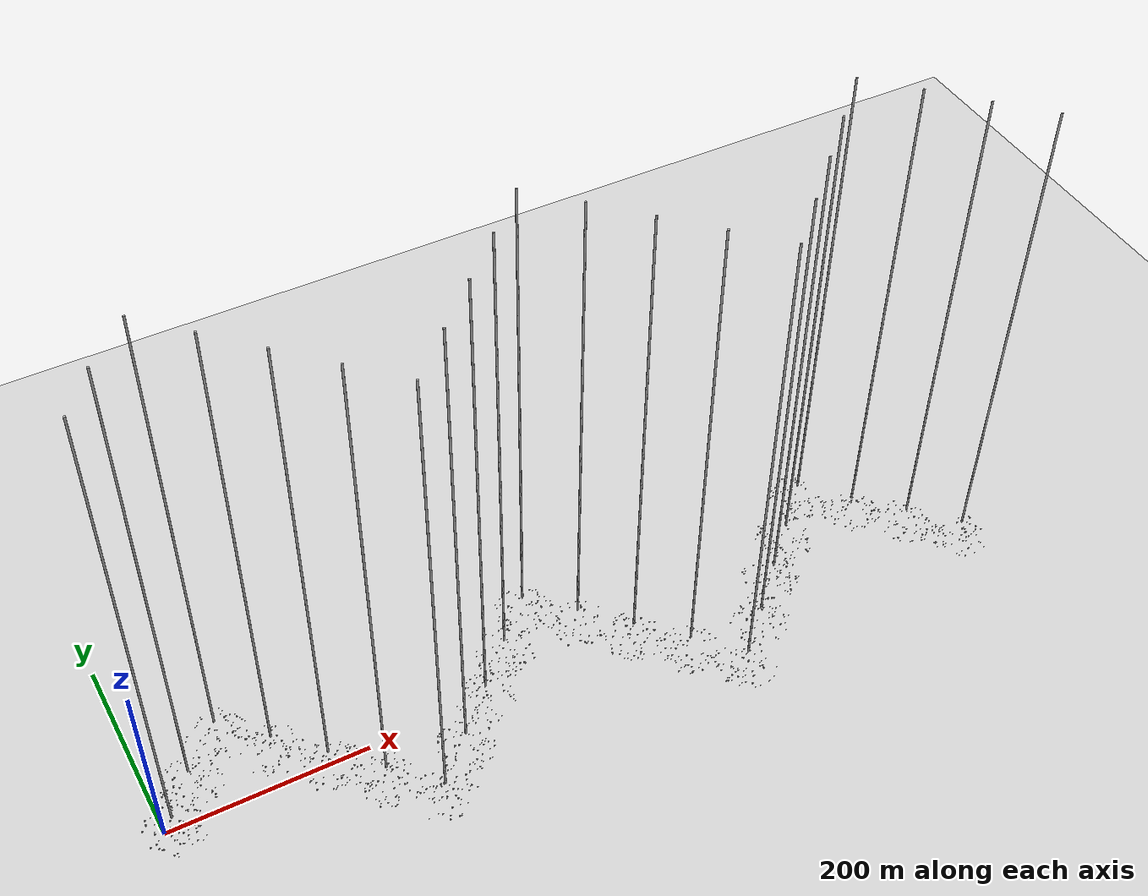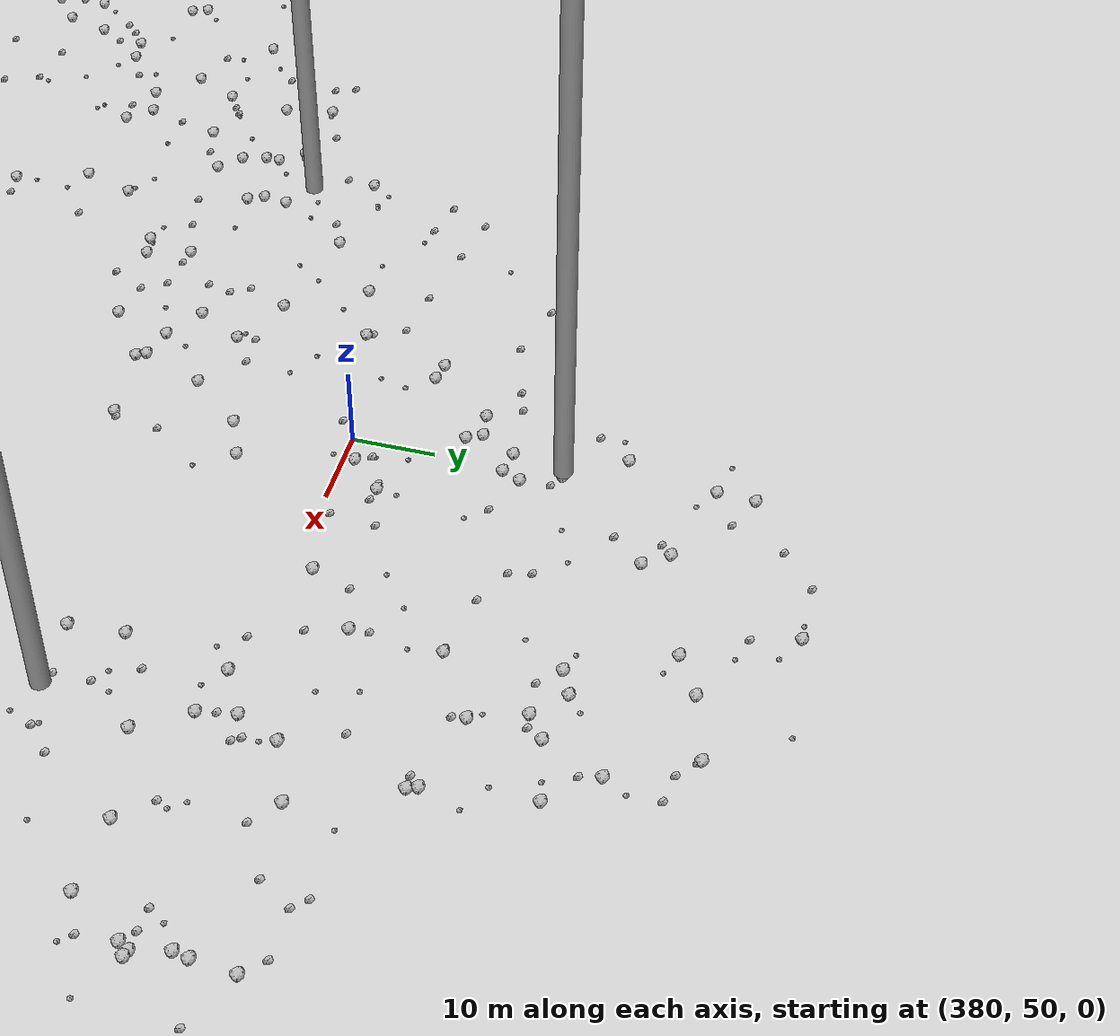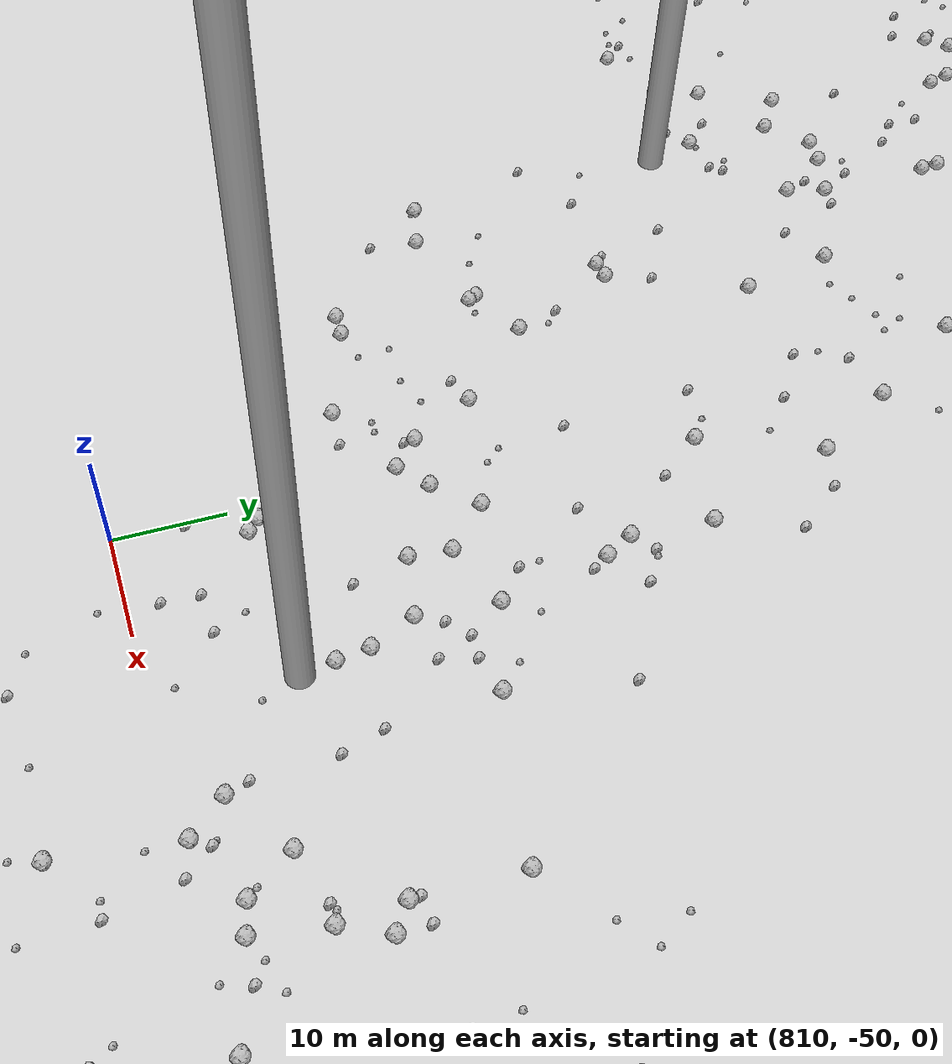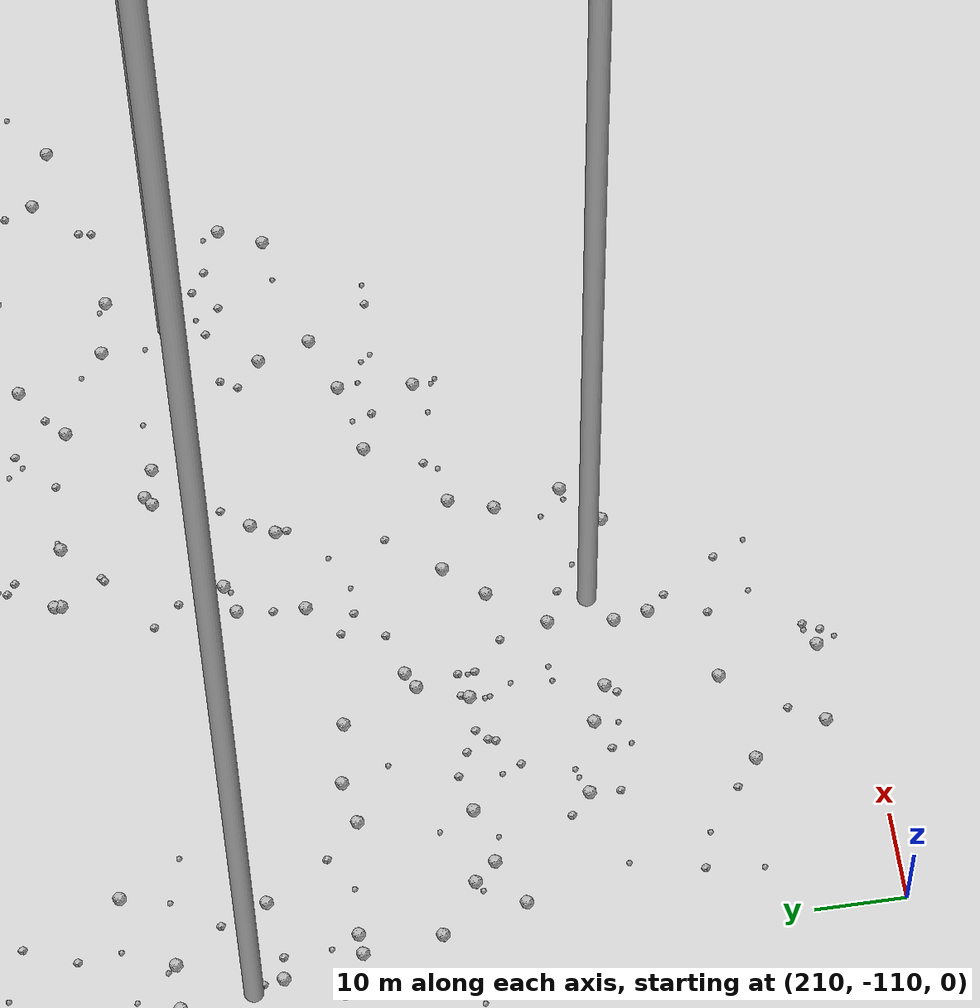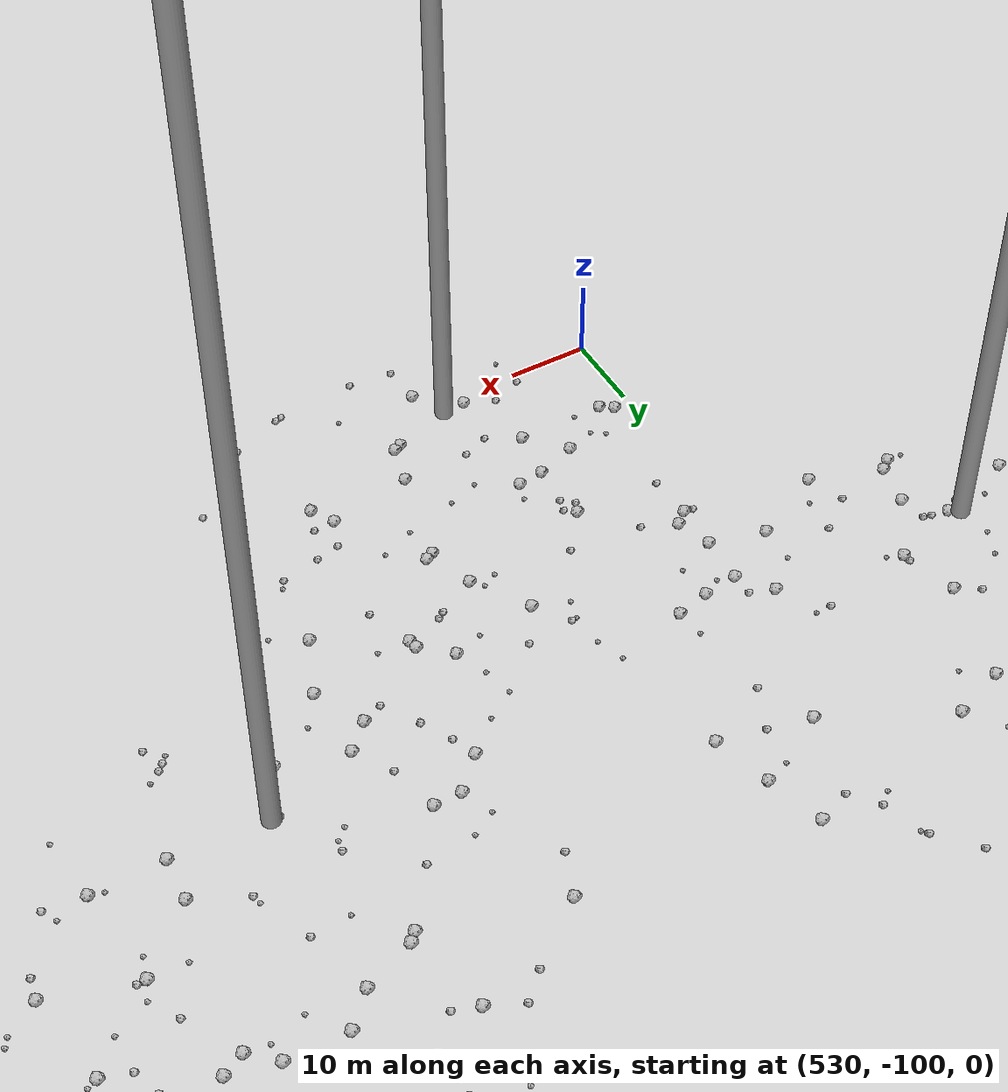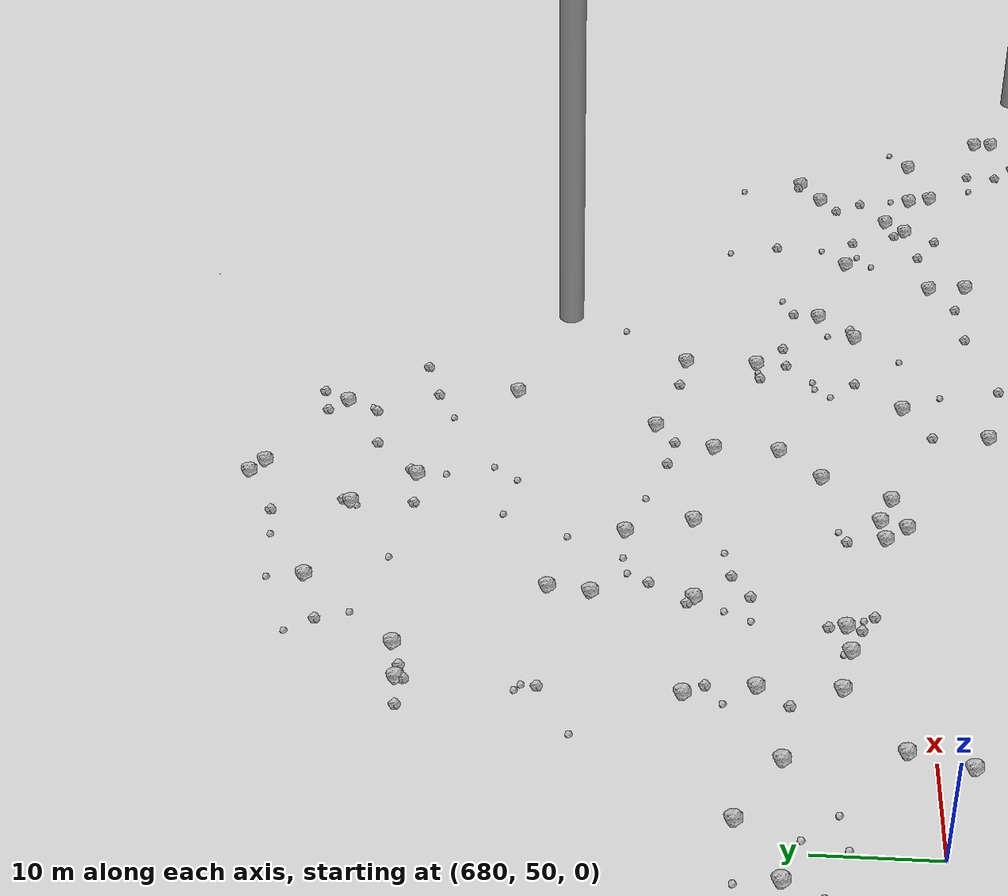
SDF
<sdf version="1.6">
 <world name="default">
  <include><uri>model://custom_ground</uri></include>
  <include><uri>model://sun</uri></include>
  <spherical_coordinates>
   <surface_model>EARTH_WGS84</surface_model>
   <latitude_deg>38.161479</latitude_deg>
   <longitude_deg>-122.454630</longitude_deg>
   <elevation>488.0</elevation>
   <heading_deg>90</heading_deg>
  </spherical_coordinates>
  <model name="rock1_0_0">
   <include><uri>model://rock1</uri><pose>-10.787216621184392 20.742451768815563 0.5 0 0 0</pose></include>
  </model>
  <model name="rock1_0_1">
   <include><uri>model://rock1</uri><pose>17.773516983565024 -3.1022882227077204 0.5 0 0 0</pose></include>
  </model>
  <model name="rock1_0_2">
   <include><uri>model://rock1</uri><pose>7.052120465616866 -0.7974193689070397 0.5 0 0 0</pose></include>
  </model>
  <model name="rock1_0_3">
   <include><uri>model://rock1</uri><pose>15.774861016928256 -6.823753588254192 0.5 0 0 0</pose></include>
  </model>
  <model name="rock1_0_4">
   <include><uri>model://rock1</uri><pose>18.753301491735193 -11.386082869724369 0.5 0 0 0</pose></include>
  </model>
  <model name="rock1_0_5">
   <include><uri>model://rock1</uri><pose>-11.53480914216236 15.44611403203146 0.5 0 0 0</pose></include>
  </model>
  <model name="rock1_0_6">
   <include><uri>model://rock1</uri><pose>12.764813548357516 -17.648452320951414 0.5 0 0 0</pose></include>
  </model>
  <model name="rock1_0_7">
   <include><uri>model://rock1</uri><pose>5.174267037431065 -5.081899053028625 0.5 0 0 0</pose></include>
  </model>
  <model name="rock1_0_8">
   <include><uri>model://rock1</uri><pose>-15.597690982251056 -8.144179071095856 0.5 0 0 0</pose></include>
  </model>
  <model name="rock1_0_9">
   <include><uri>model://rock1</uri><pose>34.96139587940527 9.4615547412226 0.5 0 0 0</pose></include>
  </model>
  <model name="rock1_0_10">
   <include><uri>model://rock1</uri><pose>-9.65522275927035 -7.52901779432932 0.5 0 0 0</pose></include>
  </model>
  <model name="rock1_0_11">
   <include><uri>model://rock1</uri><pose>0.6966920173902764 -25.375041705206097 0.5 0 0 0</pose></include>
  </model>
  <model name="rock1_0_12">
   <include><uri>model://rock1</uri><pose>24.266727354586315 -19.816670309820537 0.5 0 0 0</pose></include>
  </model>
  <model name="rock1_0_13">
   <include><uri>model://rock1</uri><pose>9.157453294103007 10.32348848844299 0.5 0 0 0</pose></include>
  </model>
  <model name="rock1_0_14">
   <include><uri>model://rock1</uri><pose>32.74282625543621 11.145965077817031 0.5 0 0 0</pose></include>
  </model>
  <model name="rock1_0_15">
   <include><uri>model://rock1</uri><pose>6.105239651157394 -10.991778983307494 0.5 0 0 0</pose></include>
  </model>
  <model name="rock1_0_16">
   <include><uri>model://rock1</uri><pose>-7.363041002742621 3.2712264499269637 0.5 0 0 0</pose></include>
  </model>
  <model name="rock1_0_17">
   <include><uri>model://rock1</uri><pose>-5.680398838158251 -15.668285545989173 0.5 0 0 0</pose></include>
  </model>
  <model name="rock1_0_18">
   <include><uri>model://rock1</uri><pose>16.654449867440967 6.373254395396316 0.5 0 0 0</pose></include>
  </model>
  <model name="rock1_0_19">
   <include><uri>model://rock1</uri><pose>7.931551689294164 26.97969845979408 0.5 0 0 0</pose></include>
  </model>
  <model name="rock1_0_20">
   <include><uri>model://rock1</uri><pose>9.059435970498313 -16.446367520944086 0.5 0 0 0</pose></include>
  </model>
  <model name="rock1_0_21">
   <include><uri>model://rock1</uri><pose>-16.373481106741846 11.298227344750885 0.5 0 0 0</pose></include>
  </model>
  <model name="rock1_0_22">
   <include><uri>model://rock1</uri><pose>-11.541426461403024 16.147185656220103 0.5 0 0 0</pose></include>
  </model>
  <model name="rock1_0_23">
   <include><uri>model://rock1</uri><pose>-9.379874701597476 -12.82175690078898 0.5 0 0 0</pose></include>
  </model>
  <model name="rock1_0_24">
   <include><uri>model://rock1</uri><pose>20.919913657929577 23.179571448445188 0.5 0 0 0</pose></include>
  </model>
  <model name="rock1_0_25">
   <include><uri>model://rock1</uri><pose>26.568037527884137 -11.654806092524005 0.5 0 0 0</pose></include>
  </model>
  <model name="rock1_0_26">
   <include><uri>model://rock1</uri><pose>31.413187612006112 -6.939950823694854 0.5 0 0 0</pose></include>
  </model>
  <model name="rock2_0_0">
   <include><uri>model://rock2</uri><pose>9.668693333723862 11.40060715594717 0.3 0 0 0</pose></include>
  </model>
  <model name="rock2_0_1">
   <include><uri>model://rock2</uri><pose>27.159314011607734 12.578301077985735 0.3 0 0 0</pose></include>
  </model>
  <model name="rock2_0_2">
   <include><uri>model://rock2</uri><pose>27.84852420731943 -1.340391212732147 0.3 0 0 0</pose></include>
  </model>
  <model name="rock2_0_3">
   <include><uri>model://rock2</uri><pose>36.22655513575341 2.2666714369004524 0.3 0 0 0</pose></include>
  </model>
  <model name="rock2_0_4">
   <include><uri>model://rock2</uri><pose>-6.903584237164731 5.39765688792842 0.3 0 0 0</pose></include>
  </model>
  <model name="rock2_0_5">
   <include><uri>model://rock2</uri><pose>-6.584268285035606 -4.207969736555832 0.3 0 0 0</pose></include>
  </model>
  <model name="rock2_0_6">
   <include><uri>model://rock2</uri><pose>33.57250246310452 16.915395784978095 0.3 0 0 0</pose></include>
  </model>
  <model name="rock2_0_7">
   <include><uri>model://rock2</uri><pose>33.337886352015424 -18.658791927806615 0.3 0 0 0</pose></include>
  </model>
  <model name="rock2_0_8">
   <include><uri>model://rock2</uri><pose>30.089973053881877 -6.296338883076359 0.3 0 0 0</pose></include>
  </model>
  <model name="rock2_0_9">
   <include><uri>model://rock2</uri><pose>19.73460806947468 4.5283399872226155 0.3 0 0 0</pose></include>
  </model>
  <model name="rock2_0_10">
   <include><uri>model://rock2</uri><pose>-8.670212981875018 -11.574181208132359 0.3 0 0 0</pose></include>
  </model>
  <model name="rock2_0_11">
   <include><uri>model://rock2</uri><pose>36.944581554240195 8.052714482015972 0.3 0 0 0</pose></include>
  </model>
  <model name="rock2_0_12">
   <include><uri>model://rock2</uri><pose>8.195704445847493 -10.592116799790865 0.3 0 0 0</pose></include>
  </model>
  <model name="rock2_0_13">
   <include><uri>model://rock2</uri><pose>20.47836093863323 -5.382069583904936 0.3 0 0 0</pose></include>
  </model>
  <model name="rock2_0_14">
   <include><uri>model://rock2</uri><pose>1.608997385395 19.83115675015256 0.3 0 0 0</pose></include>
  </model>
  <model name="rock2_0_15">
   <include><uri>model://rock2</uri><pose>3.842878275358906 -24.175397774039023 0.3 0 0 0</pose></include>
  </model>
  <model name="rock2_0_16">
   <include><uri>model://rock2</uri><pose>7.613002137825319 3.843109109259508 0.3 0 0 0</pose></include>
  </model>
  <model name="rock2_0_17">
   <include><uri>model://rock2</uri><pose>28.665464872580387 -22.136369317658183 0.3 0 0 0</pose></include>
  </model>
  <model name="rock2_0_18">
   <include><uri>model://rock2</uri><pose>17.729884195800487 -15.269517970548323 0.3 0 0 0</pose></include>
  </model>
  <model name="rock2_0_19">
   <include><uri>model://rock2</uri><pose>6.202521928972487 29.20148100401653 0.3 0 0 0</pose></include>
  </model>
  <model name="rock2_0_20">
   <include><uri>model://rock2</uri><pose>12.257827080648212 -4.797894201744494 0.3 0 0 0</pose></include>
  </model>
  <model name="rock2_0_21">
   <include><uri>model://rock2</uri><pose>-6.923828431728637 -14.988229434723268 0.3 0 0 0</pose></include>
  </model>
  <model name="rock2_0_22">
   <include><uri>model://rock2</uri><pose>-1.4499324290091238 12.453857963973796 0.3 0 0 0</pose></include>
  </model>
  <model name="rock2_0_23">
   <include><uri>model://rock2</uri><pose>27.402363053405537 -7.693605880738186 0.3 0 0 0</pose></include>
  </model>
  <model name="rock2_0_24">
   <include><uri>model://rock2</uri><pose>-4.586895980087375 13.416432855789473 0.3 0 0 0</pose></include>
  </model>
  <model name="rock2_0_25">
   <include><uri>model://rock2</uri><pose>-8.715095146147432 -12.948926837434048 0.3 0 0 0</pose></include>
  </model>
  <model name="rock2_0_26">
   <include><uri>model://rock2</uri><pose>27.851070451230406 -3.560814594192049 0.3 0 0 0</pose></include>
  </model>
  <model name="rock3_0_0">
   <include><uri>model://rock3</uri><pose>3.7140848664145096 -28.382540763528233 0.2 0 0 0</pose></include>
  </model>
  <model name="rock3_0_1">
   <include><uri>model://rock3</uri><pose>13.984934742949967 -0.7407117506684067 0.2 0 0 0</pose></include>
  </model>
  <model name="rock3_0_2">
   <include><uri>model://rock3</uri><pose>-9.963467262575405 -7.352477760636834 0.2 0 0 0</pose></include>
  </model>
  <model name="rock3_0_3">
   <include><uri>model://rock3</uri><pose>-5.1823103452841774 22.00876448086634 0.2 0 0 0</pose></include>
  </model>
  <model name="rock3_0_4">
   <include><uri>model://rock3</uri><pose>11.512375911962046 -16.674028271699356 0.2 0 0 0</pose></include>
  </model>
  <model name="rock3_0_5">
   <include><uri>model://rock3</uri><pose>-7.865842440525736 -11.092193033693388 0.2 0 0 0</pose></include>
  </model>
  <model name="rock3_0_6">
   <include><uri>model://rock3</uri><pose>14.696054940408033 20.379286102086652 0.2 0 0 0</pose></include>
  </model>
  <model name="rock3_0_7">
   <include><uri>model://rock3</uri><pose>13.447222172233388 14.147816481214981 0.2 0 0 0</pose></include>
  </model>
  <model name="rock3_0_8">
   <include><uri>model://rock3</uri><pose>25.77603033177688 14.586340493674513 0.2 0 0 0</pose></include>
  </model>
  <model name="rock3_0_9">
   <include><uri>model://rock3</uri><pose>13.811156171750916 11.223729104298712 0.2 0 0 0</pose></include>
  </model>
  <model name="rock3_0_10">
   <include><uri>model://rock3</uri><pose>15.44775985148739 28.119256064037486 0.2 0 0 0</pose></include>
  </model>
  <model name="rock3_0_11">
   <include><uri>model://rock3</uri><pose>-2.4626192662249196 11.833154320845338 0.2 0 0 0</pose></include>
  </model>
  <model name="rock3_0_12">
   <include><uri>model://rock3</uri><pose>16.900566253929718 4.808709663393891 0.2 0 0 0</pose></include>
  </model>
  <model name="rock3_0_13">
   <include><uri>model://rock3</uri><pose>17.77437876008532 21.214702957175234 0.2 0 0 0</pose></include>
  </model>
  <model name="rock3_0_14">
   <include><uri>model://rock3</uri><pose>16.907996815132606 5.110338764030104 0.2 0 0 0</pose></include>
  </model>
  <model name="rock3_0_15">
   <include><uri>model://rock3</uri><pose>-16.93663741298661 9.60264054279169 0.2 0 0 0</pose></include>
  </model>
  <model name="rock3_0_16">
   <include><uri>model://rock3</uri><pose>2.6807114160946526 9.632380680604527 0.2 0 0 0</pose></include>
  </model>
  <model name="rock3_0_17">
   <include><uri>model://rock3</uri><pose>4.468999831689576 14.972045890754373 0.2 0 0 0</pose></include>
  </model>
  <model name="rock3_0_18">
   <include><uri>model://rock3</uri><pose>34.09708881631626 11.238934588321634 0.2 0 0 0</pose></include>
  </model>
  <model name="rock3_0_19">
   <include><uri>model://rock3</uri><pose>18.81384222160223 -21.2455461181031 0.2 0 0 0</pose></include>
  </model>
  <model name="rock3_0_20">
   <include><uri>model://rock3</uri><pose>-11.442115214172134 3.48611232039827 0.2 0 0 0</pose></include>
  </model>
  <model name="rock3_0_21">
   <include><uri>model://rock3</uri><pose>1.6799918930694773 -9.242753395539431 0.2 0 0 0</pose></include>
  </model>
  <model name="rock3_0_22">
   <include><uri>model://rock3</uri><pose>17.994027601075253 6.511778484137018 0.2 0 0 0</pose></include>
  </model>
  <model name="rock3_0_23">
   <include><uri>model://rock3</uri><pose>-10.283759601808796 0.21014859003253505 0.2 0 0 0</pose></include>
  </model>
  <model name="rock3_0_24">
   <include><uri>model://rock3</uri><pose>-11.220171276936748 -7.403895382990662 0.2 0 0 0</pose></include>
  </model>
  <model name="rock3_0_25">
   <include><uri>model://rock3</uri><pose>15.568840882033392 14.122096914391392 0.2 0 0 0</pose></include>
  </model>
  <model name="rock3_0_26">
   <include><uri>model://rock3</uri><pose>-1.3784896588983457 7.322169976427951 0.2 0 0 0</pose></include>
  </model>
  <model name="rock1_1_0">
   <include><uri>model://rock1</uri><pose>28.634449901364874 51.99970946239708 0.5 0 0 0</pose></include>
  </model>
  <model name="rock1_1_1">
   <include><uri>model://rock1</uri><pose>53.551624501185366 21.947183321595695 0.5 0 0 0</pose></include>
  </model>
  <model name="rock1_1_2">
   <include><uri>model://rock1</uri><pose>50.20219757437841 55.142029262247206 0.5 0 0 0</pose></include>
  </model>
  <model name="rock1_1_3">
   <include><uri>model://rock1</uri><pose>24.20645310131698 35.20929458082412 0.5 0 0 0</pose></include>
  </model>
  <model name="rock1_1_4">
   <include><uri>model://rock1</uri><pose>13.157190504264168 39.8156296283036 0.5 0 0 0</pose></include>
  </model>
  <model name="rock1_1_5">
   <include><uri>model://rock1</uri><pose>17.335391174166784 30.459286676073386 0.5 0 0 0</pose></include>
  </model>
  <model name="rock1_1_6">
   <include><uri>model://rock1</uri><pose>15.16429527659825 24.751133837844336 0.5 0 0 0</pose></include>
  </model>
  <model name="rock1_1_7">
   <include><uri>model://rock1</uri><pose>16.01035428405475 38.315689593656884 0.5 0 0 0</pose></include>
  </model>
  <model name="rock1_1_8">
   <include><uri>model://rock1</uri><pose>47.54494083260362 54.17543833784944 0.5 0 0 0</pose></include>
  </model>
  <model name="rock1_1_9">
   <include><uri>model://rock1</uri><pose>27.54948862605232 14.19559342791839 0.5 0 0 0</pose></include>
  </model>
  <model name="rock1_1_10">
   <include><uri>model://rock1</uri><pose>56.568873197235284 62.91311643887468 0.5 0 0 0</pose></include>
  </model>
  <model name="rock1_1_11">
   <include><uri>model://rock1</uri><pose>64.35077800651001 50.690589054627125 0.5 0 0 0</pose></include>
  </model>
  <model name="rock1_1_12">
   <include><uri>model://rock1</uri><pose>24.949655280281164 61.27855752074164 0.5 0 0 0</pose></include>
  </model>
  <model name="rock1_1_13">
   <include><uri>model://rock1</uri><pose>34.58221393496508 21.096125962916922 0.5 0 0 0</pose></include>
  </model>
  <model name="rock1_1_14">
   <include><uri>model://rock1</uri><pose>24.26471272652215 19.98424881389918 0.5 0 0 0</pose></include>
  </model>
  <model name="rock1_1_15">
   <include><uri>model://rock1</uri><pose>47.072489829103496 33.438383934519024 0.5 0 0 0</pose></include>
  </model>
  <model name="rock1_1_16">
   <include><uri>model://rock1</uri><pose>54.11767902035316 56.95383708773474 0.5 0 0 0</pose></include>
  </model>
  <model name="rock1_1_17">
   <include><uri>model://rock1</uri><pose>54.68838327011005 15.296953634658983 0.5 0 0 0</pose></include>
  </model>
  <model name="rock1_1_18">
   <include><uri>model://rock1</uri><pose>63.581284169361076 50.774244743887635 0.5 0 0 0</pose></include>
  </model>
  <model name="rock1_1_19">
   <include><uri>model://rock1</uri><pose>24.604181470058585 43.99179176676503 0.5 0 0 0</pose></include>
  </model>
  <model name="rock1_1_20">
   <include><uri>model://rock1</uri><pose>11.48184775087511 37.94466943531414 0.5 0 0 0</pose></include>
  </model>
  <model name="rock1_1_21">
   <include><uri>model://rock1</uri><pose>28.93388501443915 29.102589503598463 0.5 0 0 0</pose></include>
  </model>
  <model name="rock1_1_22">
   <include><uri>model://rock1</uri><pose>26.64358495397669 51.105249961574465 0.5 0 0 0</pose></include>
  </model>
  <model name="rock1_1_23">
   <include><uri>model://rock1</uri><pose>29.154406419917784 39.76721303973838 0.5 0 0 0</pose></include>
  </model>
  <model name="rock1_1_24">
   <include><uri>model://rock1</uri><pose>17.98968312524595 42.34843295610536 0.5 0 0 0</pose></include>
  </model>
  <model name="rock1_1_25">
   <include><uri>model://rock1</uri><pose>15.693607274933733 40.771713896915955 0.5 0 0 0</pose></include>
  </model>
  <model name="rock1_1_26">
   <include><uri>model://rock1</uri><pose>55.78969738512684 18.34840211293136 0.5 0 0 0</pose></include>
  </model>
  <model name="rock2_1_0">
   <include><uri>model://rock2</uri><pose>49.4874185977389 39.37083924027027 0.3 0 0 0</pose></include>
  </model>
  <model name="rock2_1_1">
   <include><uri>model://rock2</uri><pose>24.223028286149827 42.608797825175074 0.3 0 0 0</pose></include>
  </model>
  <model name="rock2_1_2">
   <include><uri>model://rock2</uri><pose>43.75721925151263 38.81856913094508 0.3 0 0 0</pose></include>
  </model>
  <model name="rock2_1_3">
   <include><uri>model://rock2</uri><pose>24.225528887617607 64.51626731461104 0.3 0 0 0</pose></include>
  </model>
  <model name="rock2_1_4">
   <include><uri>model://rock2</uri><pose>33.82959952720316 58.42822327841769 0.3 0 0 0</pose></include>
  </model>
  <model name="rock2_1_5">
   <include><uri>model://rock2</uri><pose>29.600822494389718 65.6104176572977 0.3 0 0 0</pose></include>
  </model>
  <model name="rock2_1_6">
   <include><uri>model://rock2</uri><pose>57.168841463891596 39.427771384630276 0.3 0 0 0</pose></include>
  </model>
  <model name="rock2_1_7">
   <include><uri>model://rock2</uri><pose>36.8363891536099 24.1293424269778 0.3 0 0 0</pose></include>
  </model>
  <model name="rock2_1_8">
   <include><uri>model://rock2</uri><pose>65.17147498869653 38.440996734041235 0.3 0 0 0</pose></include>
  </model>
  <model name="rock2_1_9">
   <include><uri>model://rock2</uri><pose>55.25644947587178 14.870727538258974 0.3 0 0 0</pose></include>
  </model>
  <model name="rock2_1_10">
   <include><uri>model://rock2</uri><pose>12.129053855392504 42.902906870084855 0.3 0 0 0</pose></include>
  </model>
  <model name="rock2_1_11">
   <include><uri>model://rock2</uri><pose>52.806656666484514 41.69155058406922 0.3 0 0 0</pose></include>
  </model>
  <model name="rock2_1_12">
   <include><uri>model://rock2</uri><pose>31.911375201856224 18.44785983147318 0.3 0 0 0</pose></include>
  </model>
  <model name="rock2_1_13">
   <include><uri>model://rock2</uri><pose>43.612031281491284 51.666813572238176 0.3 0 0 0</pose></include>
  </model>
  <model name="rock2_1_14">
   <include><uri>model://rock2</uri><pose>51.56628258609128 64.72830103359303 0.3 0 0 0</pose></include>
  </model>
  <model name="rock2_1_15">
   <include><uri>model://rock2</uri><pose>65.48841567070481 24.29084584143755 0.3 0 0 0</pose></include>
  </model>
  <model name="rock2_1_16">
   <include><uri>model://rock2</uri><pose>12.409400824738142 31.405998400646958 0.3 0 0 0</pose></include>
  </model>
  <model name="rock2_1_17">
   <include><uri>model://rock2</uri><pose>21.94542637991978 28.412655891975582 0.3 0 0 0</pose></include>
  </model>
  <model name="rock2_1_18">
   <include><uri>model://rock2</uri><pose>57.78699865286095 25.19333165234425 0.3 0 0 0</pose></include>
  </model>
  <model name="rock2_1_19">
   <include><uri>model://rock2</uri><pose>43.537121798427286 32.55939487972311 0.3 0 0 0</pose></include>
  </model>
  <model name="rock2_1_20">
   <include><uri>model://rock2</uri><pose>66.77784013880952 43.18527518780486 0.3 0 0 0</pose></include>
  </model>
  <model name="rock2_1_21">
   <include><uri>model://rock2</uri><pose>54.4948409955739 22.141417283525602 0.3 0 0 0</pose></include>
  </model>
  <model name="rock2_1_22">
   <include><uri>model://rock2</uri><pose>43.34805248454326 56.847651065177445 0.3 0 0 0</pose></include>
  </model>
  <model name="rock2_1_23">
   <include><uri>model://rock2</uri><pose>54.17558554311418 23.946514620206145 0.3 0 0 0</pose></include>
  </model>
  <model name="rock2_1_24">
   <include><uri>model://rock2</uri><pose>48.606804690439525 58.433251397787856 0.3 0 0 0</pose></include>
  </model>
  <model name="rock2_1_25">
   <include><uri>model://rock2</uri><pose>39.52276142149307 65.11960514209557 0.3 0 0 0</pose></include>
  </model>
  <model name="rock2_1_26">
   <include><uri>model://rock2</uri><pose>15.781467355512053 23.134912904959528 0.3 0 0 0</pose></include>
  </model>
  <model name="rock3_1_0">
   <include><uri>model://rock3</uri><pose>38.18657759034325 54.248390758199385 0.2 0 0 0</pose></include>
  </model>
  <model name="rock3_1_1">
   <include><uri>model://rock3</uri><pose>51.36436267373872 30.484426669759685 0.2 0 0 0</pose></include>
  </model>
  <model name="rock3_1_2">
   <include><uri>model://rock3</uri><pose>38.58970696654855 22.474438101594327 0.2 0 0 0</pose></include>
  </model>
  <model name="rock3_1_3">
   <include><uri>model://rock3</uri><pose>45.54312527671894 14.118475325063455 0.2 0 0 0</pose></include>
  </model>
  <model name="rock3_1_4">
   <include><uri>model://rock3</uri><pose>45.3965217293336 39.83929506343911 0.2 0 0 0</pose></include>
  </model>
  <model name="rock3_1_5">
   <include><uri>model://rock3</uri><pose>21.334201413874254 38.109135395749306 0.2 0 0 0</pose></include>
  </model>
  <model name="rock3_1_6">
   <include><uri>model://rock3</uri><pose>49.349941187700864 44.234205089347746 0.2 0 0 0</pose></include>
  </model>
  <model name="rock3_1_7">
   <include><uri>model://rock3</uri><pose>45.48098391926106 25.035847080113708 0.2 0 0 0</pose></include>
  </model>
  <model name="rock3_1_8">
   <include><uri>model://rock3</uri><pose>49.81110135683078 27.56457424704052 0.2 0 0 0</pose></include>
  </model>
  <model name="rock3_1_9">
   <include><uri>model://rock3</uri><pose>44.811231600459706 50.02921909315204 0.2 0 0 0</pose></include>
  </model>
  <model name="rock3_1_10">
   <include><uri>model://rock3</uri><pose>58.42435914244476 36.72834189050736 0.2 0 0 0</pose></include>
  </model>
  <model name="rock3_1_11">
   <include><uri>model://rock3</uri><pose>54.95440849443572 47.563715322139025 0.2 0 0 0</pose></include>
  </model>
  <model name="rock3_1_12">
   <include><uri>model://rock3</uri><pose>37.18676884268706 68.26168973567019 0.2 0 0 0</pose></include>
  </model>
  <model name="rock3_1_13">
   <include><uri>model://rock3</uri><pose>18.925359136991815 59.09629035445636 0.2 0 0 0</pose></include>
  </model>
  <model name="rock3_1_14">
   <include><uri>model://rock3</uri><pose>31.126097605571815 67.94770438473128 0.2 0 0 0</pose></include>
  </model>
  <model name="rock3_1_15">
   <include><uri>model://rock3</uri><pose>43.07708866118324 49.107640921383705 0.2 0 0 0</pose></include>
  </model>
  <model name="rock3_1_16">
   <include><uri>model://rock3</uri><pose>37.31492098343904 28.41754511219492 0.2 0 0 0</pose></include>
  </model>
  <model name="rock3_1_17">
   <include><uri>model://rock3</uri><pose>68.75557087759155 36.130480821974224 0.2 0 0 0</pose></include>
  </model>
  <model name="rock3_1_18">
   <include><uri>model://rock3</uri><pose>49.87066646310536 40.60336051719089 0.2 0 0 0</pose></include>
  </model>
  <model name="rock3_1_19">
   <include><uri>model://rock3</uri><pose>39.71777132651265 22.291225699280364 0.2 0 0 0</pose></include>
  </model>
  <model name="rock3_1_20">
   <include><uri>model://rock3</uri><pose>31.87307109419169 42.840538215994265 0.2 0 0 0</pose></include>
  </model>
  <model name="rock3_1_21">
   <include><uri>model://rock3</uri><pose>19.026680992984335 51.631214883132955 0.2 0 0 0</pose></include>
  </model>
  <model name="rock3_1_22">
   <include><uri>model://rock3</uri><pose>25.436777517455546 17.124486963904467 0.2 0 0 0</pose></include>
  </model>
  <model name="rock3_1_23">
   <include><uri>model://rock3</uri><pose>60.0956147276376 44.45358426720871 0.2 0 0 0</pose></include>
  </model>
  <model name="rock3_1_24">
   <include><uri>model://rock3</uri><pose>40.0760179827075 66.43885404713626 0.2 0 0 0</pose></include>
  </model>
  <model name="rock3_1_25">
   <include><uri>model://rock3</uri><pose>45.52130018736064 38.05128694807868 0.2 0 0 0</pose></include>
  </model>
  <model name="rock3_1_26">
   <include><uri>model://rock3</uri><pose>15.477770857488078 24.074393910650773 0.2 0 0 0</pose></include>
  </model>
  <model name="rock1_2_0">
   <include><uri>model://rock1</uri><pose>78.55585830982761 74.69707284106099 0.5 0 0 0</pose></include>
  </model>
  <model name="rock1_2_1">
   <include><uri>model://rock1</uri><pose>72.86970610174642 59.08427206705889 0.5 0 0 0</pose></include>
  </model>
  <model name="rock1_2_2">
   <include><uri>model://rock1</uri><pose>77.48990985068603 62.60536002175492 0.5 0 0 0</pose></include>
  </model>
  <model name="rock1_2_3">
   <include><uri>model://rock1</uri><pose>94.6271525416507 70.37662373855474 0.5 0 0 0</pose></include>
  </model>
  <model name="rock1_2_4">
   <include><uri>model://rock1</uri><pose>103.83678619794212 90.071250052512 0.5 0 0 0</pose></include>
  </model>
  <model name="rock1_2_5">
   <include><uri>model://rock1</uri><pose>107.25356556351005 85.01922884913597 0.5 0 0 0</pose></include>
  </model>
  <model name="rock1_2_6">
   <include><uri>model://rock1</uri><pose>73.26342705764807 102.61054774729003 0.5 0 0 0</pose></include>
  </model>
  <model name="rock1_2_7">
   <include><uri>model://rock1</uri><pose>98.82565131899332 95.0811645726921 0.5 0 0 0</pose></include>
  </model>
  <model name="rock1_2_8">
   <include><uri>model://rock1</uri><pose>101.80862576265426 76.74609891667814 0.5 0 0 0</pose></include>
  </model>
  <model name="rock1_2_9">
   <include><uri>model://rock1</uri><pose>95.75639529680524 82.52183347841088 0.5 0 0 0</pose></include>
  </model>
  <model name="rock1_2_10">
   <include><uri>model://rock1</uri><pose>102.48708020022534 61.61859034824488 0.5 0 0 0</pose></include>
  </model>
  <model name="rock1_2_11">
   <include><uri>model://rock1</uri><pose>96.73381485200764 66.76802975018653 0.5 0 0 0</pose></include>
  </model>
  <model name="rock1_2_12">
   <include><uri>model://rock1</uri><pose>99.83272954779156 76.56849966493466 0.5 0 0 0</pose></include>
  </model>
  <model name="rock1_2_13">
   <include><uri>model://rock1</uri><pose>79.69335875912785 71.56383213861909 0.5 0 0 0</pose></include>
  </model>
  <model name="rock1_2_14">
   <include><uri>model://rock1</uri><pose>106.25491514379826 70.47061193313154 0.5 0 0 0</pose></include>
  </model>
  <model name="rock1_2_15">
   <include><uri>model://rock1</uri><pose>93.56643448745311 90.99674783329482 0.5 0 0 0</pose></include>
  </model>
  <model name="rock1_2_16">
   <include><uri>model://rock1</uri><pose>74.54020261507803 60.12650285168729 0.5 0 0 0</pose></include>
  </model>
  <model name="rock1_2_17">
   <include><uri>model://rock1</uri><pose>85.36893643086566 102.62434069702441 0.5 0 0 0</pose></include>
  </model>
  <model name="rock1_2_18">
   <include><uri>model://rock1</uri><pose>101.42520926161015 62.112088480551144 0.5 0 0 0</pose></include>
  </model>
  <model name="rock1_2_19">
   <include><uri>model://rock1</uri><pose>64.82086252740713 54.5040461848206 0.5 0 0 0</pose></include>
  </model>
  <model name="rock1_2_20">
   <include><uri>model://rock1</uri><pose>81.09870498024172 58.065285428765954 0.5 0 0 0</pose></include>
  </model>
  <model name="rock1_2_21">
   <include><uri>model://rock1</uri><pose>76.02713546023273 88.47474089362804 0.5 0 0 0</pose></include>
  </model>
  <model name="rock1_2_22">
   <include><uri>model://rock1</uri><pose>93.36248451451584 95.01154538244862 0.5 0 0 0</pose></include>
  </model>
  <model name="rock1_2_23">
   <include><uri>model://rock1</uri><pose>89.1585126926775 76.51047698393714 0.5 0 0 0</pose></include>
  </model>
  <model name="rock1_2_24">
   <include><uri>model://rock1</uri><pose>94.94078414078908 75.88308684076482 0.5 0 0 0</pose></include>
  </model>
  <model name="rock1_2_25">
   <include><uri>model://rock1</uri><pose>80.12805291560483 84.82747868667812 0.5 0 0 0</pose></include>
  </model>
  <model name="rock1_2_26">
   <include><uri>model://rock1</uri><pose>93.88414907240684 74.89538277169058 0.5 0 0 0</pose></include>
  </model>
  <model name="rock2_2_0">
   <include><uri>model://rock2</uri><pose>81.88007158239532 84.64164349566866 0.3 0 0 0</pose></include>
  </model>
  <model name="rock2_2_1">
   <include><uri>model://rock2</uri><pose>95.23895232366229 95.60257066693966 0.3 0 0 0</pose></include>
  </model>
  <model name="rock2_2_2">
   <include><uri>model://rock2</uri><pose>73.96272272007361 84.64210925725847 0.3 0 0 0</pose></include>
  </model>
  <model name="rock2_2_3">
   <include><uri>model://rock2</uri><pose>99.23204762337102 66.75492828180904 0.3 0 0 0</pose></include>
  </model>
  <model name="rock2_2_4">
   <include><uri>model://rock2</uri><pose>66.90315006133977 75.07211607981544 0.3 0 0 0</pose></include>
  </model>
  <model name="rock2_2_5">
   <include><uri>model://rock2</uri><pose>79.89671675978194 74.02187645632513 0.3 0 0 0</pose></include>
  </model>
  <model name="rock2_2_6">
   <include><uri>model://rock2</uri><pose>54.94673780748799 89.53149256518216 0.3 0 0 0</pose></include>
  </model>
  <model name="rock2_2_7">
   <include><uri>model://rock2</uri><pose>73.06006372489573 105.48109102511376 0.3 0 0 0</pose></include>
  </model>
  <model name="rock2_2_8">
   <include><uri>model://rock2</uri><pose>98.43966375525005 85.05847112677397 0.3 0 0 0</pose></include>
  </model>
  <model name="rock2_2_9">
   <include><uri>model://rock2</uri><pose>103.91357179356399 69.95058114406254 0.3 0 0 0</pose></include>
  </model>
  <model name="rock2_2_10">
   <include><uri>model://rock2</uri><pose>65.55407317852759 61.90057191301082 0.3 0 0 0</pose></include>
  </model>
  <model name="rock2_2_11">
   <include><uri>model://rock2</uri><pose>81.60914931976009 50.111699812065204 0.3 0 0 0</pose></include>
  </model>
  <model name="rock2_2_12">
   <include><uri>model://rock2</uri><pose>79.24285467690206 76.93578968114741 0.3 0 0 0</pose></include>
  </model>
  <model name="rock2_2_13">
   <include><uri>model://rock2</uri><pose>51.26077287421099 85.15653577674178 0.3 0 0 0</pose></include>
  </model>
  <model name="rock2_2_14">
   <include><uri>model://rock2</uri><pose>81.52224822249185 61.99021344043939 0.3 0 0 0</pose></include>
  </model>
  <model name="rock2_2_15">
   <include><uri>model://rock2</uri><pose>97.1440501149061 75.34404351010868 0.3 0 0 0</pose></include>
  </model>
  <model name="rock2_2_16">
   <include><uri>model://rock2</uri><pose>63.755956284643545 80.30299518354417 0.3 0 0 0</pose></include>
  </model>
  <model name="rock2_2_17">
   <include><uri>model://rock2</uri><pose>73.11135477004626 65.06363536741394 0.3 0 0 0</pose></include>
  </model>
  <model name="rock2_2_18">
   <include><uri>model://rock2</uri><pose>108.99376571315807 81.92663351181822 0.3 0 0 0</pose></include>
  </model>
  <model name="rock2_2_19">
   <include><uri>model://rock2</uri><pose>88.02183832597423 79.27211050195275 0.3 0 0 0</pose></include>
  </model>
  <model name="rock2_2_20">
   <include><uri>model://rock2</uri><pose>67.04256036068378 97.59135264749196 0.3 0 0 0</pose></include>
  </model>
  <model name="rock2_2_21">
   <include><uri>model://rock2</uri><pose>54.44120124677116 90.06915670206874 0.3 0 0 0</pose></include>
  </model>
  <model name="rock2_2_22">
   <include><uri>model://rock2</uri><pose>106.15178185201557 87.47202806232838 0.3 0 0 0</pose></include>
  </model>
  <model name="rock2_2_23">
   <include><uri>model://rock2</uri><pose>94.91041713603387 88.83271394266131 0.3 0 0 0</pose></include>
  </model>
  <model name="rock2_2_24">
   <include><uri>model://rock2</uri><pose>69.14074166828367 100.6664293415304 0.3 0 0 0</pose></include>
  </model>
  <model name="rock2_2_25">
   <include><uri>model://rock2</uri><pose>91.34891397903343 100.177268833036 0.3 0 0 0</pose></include>
  </model>
  <model name="rock2_2_26">
   <include><uri>model://rock2</uri><pose>70.73583513684758 57.80198695948983 0.3 0 0 0</pose></include>
  </model>
  <model name="rock3_2_0">
   <include><uri>model://rock3</uri><pose>58.05743070429676 86.22789457866457 0.2 0 0 0</pose></include>
  </model>
  <model name="rock3_2_1">
   <include><uri>model://rock3</uri><pose>98.31462183492712 88.0519039846904 0.2 0 0 0</pose></include>
  </model>
  <model name="rock3_2_2">
   <include><uri>model://rock3</uri><pose>57.93043361456679 63.44548287405853 0.2 0 0 0</pose></include>
  </model>
  <model name="rock3_2_3">
   <include><uri>model://rock3</uri><pose>65.03314179102597 74.8718537846094 0.2 0 0 0</pose></include>
  </model>
  <model name="rock3_2_4">
   <include><uri>model://rock3</uri><pose>80.24651055555206 74.24429657527268 0.2 0 0 0</pose></include>
  </model>
  <model name="rock3_2_5">
   <include><uri>model://rock3</uri><pose>83.65838578347766 107.73843161742272 0.2 0 0 0</pose></include>
  </model>
  <model name="rock3_2_6">
   <include><uri>model://rock3</uri><pose>92.41716220014646 106.79240215755954 0.2 0 0 0</pose></include>
  </model>
  <model name="rock3_2_7">
   <include><uri>model://rock3</uri><pose>65.08035623183584 96.53947950631837 0.2 0 0 0</pose></include>
  </model>
  <model name="rock3_2_8">
   <include><uri>model://rock3</uri><pose>103.3218012850972 88.19959562595304 0.2 0 0 0</pose></include>
  </model>
  <model name="rock3_2_9">
   <include><uri>model://rock3</uri><pose>80.88130244870243 73.80636208772233 0.2 0 0 0</pose></include>
  </model>
  <model name="rock3_2_10">
   <include><uri>model://rock3</uri><pose>71.80119029347736 62.50799342822763 0.2 0 0 0</pose></include>
  </model>
  <model name="rock3_2_11">
   <include><uri>model://rock3</uri><pose>90.2702569354917 53.43797188038156 0.2 0 0 0</pose></include>
  </model>
  <model name="rock3_2_12">
   <include><uri>model://rock3</uri><pose>94.19341187857746 102.54994333733708 0.2 0 0 0</pose></include>
  </model>
  <model name="rock3_2_13">
   <include><uri>model://rock3</uri><pose>67.92334714748594 85.29355610607888 0.2 0 0 0</pose></include>
  </model>
  <model name="rock3_2_14">
   <include><uri>model://rock3</uri><pose>61.14834517600048 77.43570056247073 0.2 0 0 0</pose></include>
  </model>
  <model name="rock3_2_15">
   <include><uri>model://rock3</uri><pose>74.2071533842356 87.56058100661919 0.2 0 0 0</pose></include>
  </model>
  <model name="rock3_2_16">
   <include><uri>model://rock3</uri><pose>57.241761112646124 71.79669776549589 0.2 0 0 0</pose></include>
  </model>
  <model name="rock3_2_17">
   <include><uri>model://rock3</uri><pose>82.50540265711071 101.69230963011191 0.2 0 0 0</pose></include>
  </model>
  <model name="rock3_2_18">
   <include><uri>model://rock3</uri><pose>103.06873776745185 93.77206516205878 0.2 0 0 0</pose></include>
  </model>
  <model name="rock3_2_19">
   <include><uri>model://rock3</uri><pose>72.28035323873965 64.50603345725756 0.2 0 0 0</pose></include>
  </model>
  <model name="rock3_2_20">
   <include><uri>model://rock3</uri><pose>55.78541655804087 93.36139352574764 0.2 0 0 0</pose></include>
  </model>
  <model name="rock3_2_21">
   <include><uri>model://rock3</uri><pose>57.015521837727164 78.81059179315174 0.2 0 0 0</pose></include>
  </model>
  <model name="rock3_2_22">
   <include><uri>model://rock3</uri><pose>78.02756468201 61.95329005909996 0.2 0 0 0</pose></include>
  </model>
  <model name="rock3_2_23">
   <include><uri>model://rock3</uri><pose>53.63997213496313 78.34680610440196 0.2 0 0 0</pose></include>
  </model>
  <model name="rock3_2_24">
   <include><uri>model://rock3</uri><pose>70.44514847962833 83.98939310121652 0.2 0 0 0</pose></include>
  </model>
  <model name="rock3_2_25">
   <include><uri>model://rock3</uri><pose>73.74910573129543 103.11520237281397 0.2 0 0 0</pose></include>
  </model>
  <model name="rock3_2_26">
   <include><uri>model://rock3</uri><pose>97.80356520705645 75.32030893229746 0.2 0 0 0</pose></include>
  </model>
  <model name="rock1_3_0">
   <include><uri>model://rock1</uri><pose>124.20397188574867 45.37727883197964 0.5 0 0 0</pose></include>
  </model>
  <model name="rock1_3_1">
   <include><uri>model://rock1</uri><pose>107.00508083819814 40.751110277096004 0.5 0 0 0</pose></include>
  </model>
  <model name="rock1_3_2">
   <include><uri>model://rock1</uri><pose>129.93682308659274 26.497876583103245 0.5 0 0 0</pose></include>
  </model>
  <model name="rock1_3_3">
   <include><uri>model://rock1</uri><pose>105.73046309327698 63.40202744197849 0.5 0 0 0</pose></include>
  </model>
  <model name="rock1_3_4">
   <include><uri>model://rock1</uri><pose>148.33094735199387 35.890996930948305 0.5 0 0 0</pose></include>
  </model>
  <model name="rock1_3_5">
   <include><uri>model://rock1</uri><pose>114.7763305715327 50.761894314399775 0.5 0 0 0</pose></include>
  </model>
  <model name="rock1_3_6">
   <include><uri>model://rock1</uri><pose>127.20443210417292 60.26739098683806 0.5 0 0 0</pose></include>
  </model>
  <model name="rock1_3_7">
   <include><uri>model://rock1</uri><pose>110.07702831395076 59.567596662557705 0.5 0 0 0</pose></include>
  </model>
  <model name="rock1_3_8">
   <include><uri>model://rock1</uri><pose>110.96929182289118 15.75633675212567 0.5 0 0 0</pose></include>
  </model>
  <model name="rock1_3_9">
   <include><uri>model://rock1</uri><pose>117.36983028783413 51.704279636729765 0.5 0 0 0</pose></include>
  </model>
  <model name="rock1_3_10">
   <include><uri>model://rock1</uri><pose>130.6214069366113 33.962930159859724 0.5 0 0 0</pose></include>
  </model>
  <model name="rock1_3_11">
   <include><uri>model://rock1</uri><pose>129.07659357914235 52.40971995510442 0.5 0 0 0</pose></include>
  </model>
  <model name="rock1_3_12">
   <include><uri>model://rock1</uri><pose>131.5845724151448 62.292077562105376 0.5 0 0 0</pose></include>
  </model>
  <model name="rock1_3_13">
   <include><uri>model://rock1</uri><pose>117.31786853273724 59.72260994455102 0.5 0 0 0</pose></include>
  </model>
  <model name="rock1_3_14">
   <include><uri>model://rock1</uri><pose>139.86001953123616 38.91494277419807 0.5 0 0 0</pose></include>
  </model>
  <model name="rock1_3_15">
   <include><uri>model://rock1</uri><pose>118.44828753674769 21.22644935991674 0.5 0 0 0</pose></include>
  </model>
  <model name="rock1_3_16">
   <include><uri>model://rock1</uri><pose>106.80821770244668 24.735066077900356 0.5 0 0 0</pose></include>
  </model>
  <model name="rock1_3_17">
   <include><uri>model://rock1</uri><pose>119.75956617265942 24.637921506013534 0.5 0 0 0</pose></include>
  </model>
  <model name="rock1_3_18">
   <include><uri>model://rock1</uri><pose>142.11204973198932 28.36971769060296 0.5 0 0 0</pose></include>
  </model>
  <model name="rock1_3_19">
   <include><uri>model://rock1</uri><pose>143.52481926001104 39.78544242443382 0.5 0 0 0</pose></include>
  </model>
  <model name="rock1_3_20">
   <include><uri>model://rock1</uri><pose>122.3533064410766 10.311495225259879 0.5 0 0 0</pose></include>
  </model>
  <model name="rock1_3_21">
   <include><uri>model://rock1</uri><pose>129.4863371373837 25.084206290326037 0.5 0 0 0</pose></include>
  </model>
  <model name="rock1_3_22">
   <include><uri>model://rock1</uri><pose>123.30330455149536 29.167503866911122 0.5 0 0 0</pose></include>
  </model>
  <model name="rock1_3_23">
   <include><uri>model://rock1</uri><pose>120.36918754855763 46.644020209521976 0.5 0 0 0</pose></include>
  </model>
  <model name="rock1_3_24">
   <include><uri>model://rock1</uri><pose>134.62335728763327 34.12208986302238 0.5 0 0 0</pose></include>
  </model>
  <model name="rock1_3_25">
   <include><uri>model://rock1</uri><pose>118.84944279863362 45.45355161935898 0.5 0 0 0</pose></include>
  </model>
  <model name="rock1_3_26">
   <include><uri>model://rock1</uri><pose>130.77835687863308 44.60066134520463 0.5 0 0 0</pose></include>
  </model>
  <model name="rock2_3_0">
   <include><uri>model://rock2</uri><pose>113.30428339669562 62.083991800375415 0.3 0 0 0</pose></include>
  </model>
  <model name="rock2_3_1">
   <include><uri>model://rock2</uri><pose>91.73832269095146 49.300111771122715 0.3 0 0 0</pose></include>
  </model>
  <model name="rock2_3_2">
   <include><uri>model://rock2</uri><pose>127.94188231870103 63.529175111063495 0.3 0 0 0</pose></include>
  </model>
  <model name="rock2_3_3">
   <include><uri>model://rock2</uri><pose>130.36675080562995 25.26209159507161 0.3 0 0 0</pose></include>
  </model>
  <model name="rock2_3_4">
   <include><uri>model://rock2</uri><pose>104.81595704302224 27.92516294836037 0.3 0 0 0</pose></include>
  </model>
  <model name="rock2_3_5">
   <include><uri>model://rock2</uri><pose>143.94981953270465 52.23792673019689 0.3 0 0 0</pose></include>
  </model>
  <model name="rock2_3_6">
   <include><uri>model://rock2</uri><pose>109.7960660239963 56.6201357517781 0.3 0 0 0</pose></include>
  </model>
  <model name="rock2_3_7">
   <include><uri>model://rock2</uri><pose>142.448035653093 47.62964273928335 0.3 0 0 0</pose></include>
  </model>
  <model name="rock2_3_8">
   <include><uri>model://rock2</uri><pose>110.32756109031425 42.92901105016551 0.3 0 0 0</pose></include>
  </model>
  <model name="rock2_3_9">
   <include><uri>model://rock2</uri><pose>132.52602045181956 37.36659643031693 0.3 0 0 0</pose></include>
  </model>
  <model name="rock2_3_10">
   <include><uri>model://rock2</uri><pose>134.25927830303 32.09292392612501 0.3 0 0 0</pose></include>
  </model>
  <model name="rock2_3_11">
   <include><uri>model://rock2</uri><pose>146.05324191880285 25.56084899208889 0.3 0 0 0</pose></include>
  </model>
  <model name="rock2_3_12">
   <include><uri>model://rock2</uri><pose>124.44333962824939 48.39892551613742 0.3 0 0 0</pose></include>
  </model>
  <model name="rock2_3_13">
   <include><uri>model://rock2</uri><pose>112.75830750673475 64.98614778762058 0.3 0 0 0</pose></include>
  </model>
  <model name="rock2_3_14">
   <include><uri>model://rock2</uri><pose>107.09675029122167 53.92754162693679 0.3 0 0 0</pose></include>
  </model>
  <model name="rock2_3_15">
   <include><uri>model://rock2</uri><pose>123.68053028050255 27.765255919794125 0.3 0 0 0</pose></include>
  </model>
  <model name="rock2_3_16">
   <include><uri>model://rock2</uri><pose>104.98834848457776 14.696136122374321 0.3 0 0 0</pose></include>
  </model>
  <model name="rock2_3_17">
   <include><uri>model://rock2</uri><pose>142.41132447215855 57.85940373026097 0.3 0 0 0</pose></include>
  </model>
  <model name="rock2_3_18">
   <include><uri>model://rock2</uri><pose>129.15569717413027 38.495191654524994 0.3 0 0 0</pose></include>
  </model>
  <model name="rock2_3_19">
   <include><uri>model://rock2</uri><pose>105.49265988683804 41.17522473786382 0.3 0 0 0</pose></include>
  </model>
  <model name="rock2_3_20">
   <include><uri>model://rock2</uri><pose>137.7494086700251 15.992402676588114 0.3 0 0 0</pose></include>
  </model>
  <model name="rock2_3_21">
   <include><uri>model://rock2</uri><pose>94.51453290472296 24.86049900496581 0.3 0 0 0</pose></include>
  </model>
  <model name="rock2_3_22">
   <include><uri>model://rock2</uri><pose>131.0338030954441 41.10187846907774 0.3 0 0 0</pose></include>
  </model>
  <model name="rock2_3_23">
   <include><uri>model://rock2</uri><pose>104.60916875330435 19.612995440480592 0.3 0 0 0</pose></include>
  </model>
  <model name="rock2_3_24">
   <include><uri>model://rock2</uri><pose>142.3138849915013 31.27857725117861 0.3 0 0 0</pose></include>
  </model>
  <model name="rock2_3_25">
   <include><uri>model://rock2</uri><pose>101.08017267249102 54.91925363611036 0.3 0 0 0</pose></include>
  </model>
  <model name="rock2_3_26">
   <include><uri>model://rock2</uri><pose>130.92236270934043 29.70831912736223 0.3 0 0 0</pose></include>
  </model>
  <model name="rock3_3_0">
   <include><uri>model://rock3</uri><pose>133.86654485219086 57.247163791347994 0.2 0 0 0</pose></include>
  </model>
  <model name="rock3_3_1">
   <include><uri>model://rock3</uri><pose>102.3443588413949 48.2322356775429 0.2 0 0 0</pose></include>
  </model>
  <model name="rock3_3_2">
   <include><uri>model://rock3</uri><pose>114.56578926082777 18.585522240490185 0.2 0 0 0</pose></include>
  </model>
  <model name="rock3_3_3">
   <include><uri>model://rock3</uri><pose>107.01179770081248 51.34438405435438 0.2 0 0 0</pose></include>
  </model>
  <model name="rock3_3_4">
   <include><uri>model://rock3</uri><pose>128.88136384911184 64.01753435495911 0.2 0 0 0</pose></include>
  </model>
  <model name="rock3_3_5">
   <include><uri>model://rock3</uri><pose>148.15697377029193 30.423813318777455 0.2 0 0 0</pose></include>
  </model>
  <model name="rock3_3_6">
   <include><uri>model://rock3</uri><pose>110.65659793246455 27.002505889291765 0.2 0 0 0</pose></include>
  </model>
  <model name="rock3_3_7">
   <include><uri>model://rock3</uri><pose>112.13504058740955 18.13740961397319 0.2 0 0 0</pose></include>
  </model>
  <model name="rock3_3_8">
   <include><uri>model://rock3</uri><pose>126.01569408688738 65.79984150083627 0.2 0 0 0</pose></include>
  </model>
  <model name="rock3_3_9">
   <include><uri>model://rock3</uri><pose>103.54664154535698 21.6282669631233 0.2 0 0 0</pose></include>
  </model>
  <model name="rock3_3_10">
   <include><uri>model://rock3</uri><pose>112.808632479116 22.08245176218417 0.2 0 0 0</pose></include>
  </model>
  <model name="rock3_3_11">
   <include><uri>model://rock3</uri><pose>122.7517912596781 68.42252020271653 0.2 0 0 0</pose></include>
  </model>
  <model name="rock3_3_12">
   <include><uri>model://rock3</uri><pose>99.63727446028807 43.43705006739087 0.2 0 0 0</pose></include>
  </model>
  <model name="rock3_3_13">
   <include><uri>model://rock3</uri><pose>114.43334983686883 64.09095847678564 0.2 0 0 0</pose></include>
  </model>
  <model name="rock3_3_14">
   <include><uri>model://rock3</uri><pose>105.8799637063221 20.97060614442856 0.2 0 0 0</pose></include>
  </model>
  <model name="rock3_3_15">
   <include><uri>model://rock3</uri><pose>98.13979008503492 54.57489499748717 0.2 0 0 0</pose></include>
  </model>
  <model name="rock3_3_16">
   <include><uri>model://rock3</uri><pose>148.52361499863403 37.21076394113073 0.2 0 0 0</pose></include>
  </model>
  <model name="rock3_3_17">
   <include><uri>model://rock3</uri><pose>106.8071923389583 58.828147573045236 0.2 0 0 0</pose></include>
  </model>
  <model name="rock3_3_18">
   <include><uri>model://rock3</uri><pose>101.91912886761314 28.44338248394713 0.2 0 0 0</pose></include>
  </model>
  <model name="rock3_3_19">
   <include><uri>model://rock3</uri><pose>107.75758756559331 59.63174896648348 0.2 0 0 0</pose></include>
  </model>
  <model name="rock3_3_20">
   <include><uri>model://rock3</uri><pose>119.35568391092355 22.517907672359907 0.2 0 0 0</pose></include>
  </model>
  <model name="rock3_3_21">
   <include><uri>model://rock3</uri><pose>94.50083687391994 38.725267873846036 0.2 0 0 0</pose></include>
  </model>
  <model name="rock3_3_22">
   <include><uri>model://rock3</uri><pose>128.1441837345505 27.634245531988157 0.2 0 0 0</pose></include>
  </model>
  <model name="rock3_3_23">
   <include><uri>model://rock3</uri><pose>118.28154652050269 42.342101397691685 0.2 0 0 0</pose></include>
  </model>
  <model name="rock3_3_24">
   <include><uri>model://rock3</uri><pose>95.02557138805234 28.992630927531806 0.2 0 0 0</pose></include>
  </model>
  <model name="rock3_3_25">
   <include><uri>model://rock3</uri><pose>141.61221981536357 23.06185204276381 0.2 0 0 0</pose></include>
  </model>
  <model name="rock3_3_26">
   <include><uri>model://rock3</uri><pose>93.19441737197133 33.925497837362364 0.2 0 0 0</pose></include>
  </model>
  <model name="rock1_4_0">
   <include><uri>model://rock1</uri><pose>166.17086650535447 -16.89787245371358 0.5 0 0 0</pose></include>
  </model>
  <model name="rock1_4_1">
   <include><uri>model://rock1</uri><pose>153.9215635432043 18.176276876614956 0.5 0 0 0</pose></include>
  </model>
  <model name="rock1_4_2">
   <include><uri>model://rock1</uri><pose>175.9557372049568 -14.275437855927049 0.5 0 0 0</pose></include>
  </model>
  <model name="rock1_4_3">
   <include><uri>model://rock1</uri><pose>156.21890554392738 25.625770846096728 0.5 0 0 0</pose></include>
  </model>
  <model name="rock1_4_4">
   <include><uri>model://rock1</uri><pose>138.42685240746016 8.426729592187932 0.5 0 0 0</pose></include>
  </model>
  <model name="rock1_4_5">
   <include><uri>model://rock1</uri><pose>146.00189240722537 -16.963327511114485 0.5 0 0 0</pose></include>
  </model>
  <model name="rock1_4_6">
   <include><uri>model://rock1</uri><pose>155.0990420201427 6.922798934770242 0.5 0 0 0</pose></include>
  </model>
  <model name="rock1_4_7">
   <include><uri>model://rock1</uri><pose>167.6336511433619 0.6597386230554321 0.5 0 0 0</pose></include>
  </model>
  <model name="rock1_4_8">
   <include><uri>model://rock1</uri><pose>152.45375916953776 17.793099086946313 0.5 0 0 0</pose></include>
  </model>
  <model name="rock1_4_9">
   <include><uri>model://rock1</uri><pose>141.02746974874427 -12.840602219899871 0.5 0 0 0</pose></include>
  </model>
  <model name="rock1_4_10">
   <include><uri>model://rock1</uri><pose>179.9214215369971 -11.458855438319326 0.5 0 0 0</pose></include>
  </model>
  <model name="rock1_4_11">
   <include><uri>model://rock1</uri><pose>136.25866124977603 -9.925402228514283 0.5 0 0 0</pose></include>
  </model>
  <model name="rock1_4_12">
   <include><uri>model://rock1</uri><pose>158.1300170548083 10.86602127962594 0.5 0 0 0</pose></include>
  </model>
  <model name="rock1_4_13">
   <include><uri>model://rock1</uri><pose>148.93834756242063 12.700966667158099 0.5 0 0 0</pose></include>
  </model>
  <model name="rock1_4_14">
   <include><uri>model://rock1</uri><pose>188.27147563878026 7.83606693305601 0.5 0 0 0</pose></include>
  </model>
  <model name="rock1_4_15">
   <include><uri>model://rock1</uri><pose>168.56048293088207 7.589662236094199 0.5 0 0 0</pose></include>
  </model>
  <model name="rock1_4_16">
   <include><uri>model://rock1</uri><pose>138.61292565429588 -20.0698211016529 0.5 0 0 0</pose></include>
  </model>
  <model name="rock1_4_17">
   <include><uri>model://rock1</uri><pose>161.35598176611452 5.256751151530906 0.5 0 0 0</pose></include>
  </model>
  <model name="rock1_4_18">
   <include><uri>model://rock1</uri><pose>161.15829421447205 3.9561501804880734 0.5 0 0 0</pose></include>
  </model>
  <model name="rock1_4_19">
   <include><uri>model://rock1</uri><pose>138.8149419659808 -20.4362278585377 0.5 0 0 0</pose></include>
  </model>
  <model name="rock1_4_20">
   <include><uri>model://rock1</uri><pose>163.85826506326583 -18.933405355767565 0.5 0 0 0</pose></include>
  </model>
  <model name="rock1_4_21">
   <include><uri>model://rock1</uri><pose>162.9813524588074 3.7997514842885067 0.5 0 0 0</pose></include>
  </model>
  <model name="rock1_4_22">
   <include><uri>model://rock1</uri><pose>180.88782654016754 9.201366708795824 0.5 0 0 0</pose></include>
  </model>
  <model name="rock1_4_23">
   <include><uri>model://rock1</uri><pose>181.22353063662428 -14.84020841074953 0.5 0 0 0</pose></include>
  </model>
  <model name="rock1_4_24">
   <include><uri>model://rock1</uri><pose>172.12439123555131 10.395252708005579 0.5 0 0 0</pose></include>
  </model>
  <model name="rock1_4_25">
   <include><uri>model://rock1</uri><pose>144.8983246577019 10.594560048147251 0.5 0 0 0</pose></include>
  </model>
  <model name="rock1_4_26">
   <include><uri>model://rock1</uri><pose>184.04721549106608 8.56679895422861 0.5 0 0 0</pose></include>
  </model>
  <model name="rock2_4_0">
   <include><uri>model://rock2</uri><pose>157.24252145224227 24.740442712159783 0.3 0 0 0</pose></include>
  </model>
  <model name="rock2_4_1">
   <include><uri>model://rock2</uri><pose>165.29729749796934 18.278006870540082 0.3 0 0 0</pose></include>
  </model>
  <model name="rock2_4_2">
   <include><uri>model://rock2</uri><pose>155.72865089524498 -26.913438421730326 0.3 0 0 0</pose></include>
  </model>
  <model name="rock2_4_3">
   <include><uri>model://rock2</uri><pose>168.14375227791768 -20.36520408001152 0.3 0 0 0</pose></include>
  </model>
  <model name="rock2_4_4">
   <include><uri>model://rock2</uri><pose>180.19399275271576 5.570854323001377 0.3 0 0 0</pose></include>
  </model>
  <model name="rock2_4_5">
   <include><uri>model://rock2</uri><pose>147.0665270569534 13.173914417068843 0.3 0 0 0</pose></include>
  </model>
  <model name="rock2_4_6">
   <include><uri>model://rock2</uri><pose>160.34265997938493 9.621333248261536 0.3 0 0 0</pose></include>
  </model>
  <model name="rock2_4_7">
   <include><uri>model://rock2</uri><pose>185.68407139068984 2.1002920799301776 0.3 0 0 0</pose></include>
  </model>
  <model name="rock2_4_8">
   <include><uri>model://rock2</uri><pose>140.10597975301474 -7.500649485139423 0.3 0 0 0</pose></include>
  </model>
  <model name="rock2_4_9">
   <include><uri>model://rock2</uri><pose>169.50798758918688 -24.237395319553606 0.3 0 0 0</pose></include>
  </model>
  <model name="rock2_4_10">
   <include><uri>model://rock2</uri><pose>152.34103549404597 -26.215677271838643 0.3 0 0 0</pose></include>
  </model>
  <model name="rock2_4_11">
   <include><uri>model://rock2</uri><pose>143.7443304361372 16.941993445477458 0.3 0 0 0</pose></include>
  </model>
  <model name="rock2_4_12">
   <include><uri>model://rock2</uri><pose>149.1283729672787 -10.350653125753439 0.3 0 0 0</pose></include>
  </model>
  <model name="rock2_4_13">
   <include><uri>model://rock2</uri><pose>164.02529855620662 -16.12817420212935 0.3 0 0 0</pose></include>
  </model>
  <model name="rock2_4_14">
   <include><uri>model://rock2</uri><pose>156.97445014171427 -24.706128992997794 0.3 0 0 0</pose></include>
  </model>
  <model name="rock2_4_15">
   <include><uri>model://rock2</uri><pose>163.549830379868 -27.183373060173924 0.3 0 0 0</pose></include>
  </model>
  <model name="rock2_4_16">
   <include><uri>model://rock2</uri><pose>137.77380754812017 -9.065371581448478 0.3 0 0 0</pose></include>
  </model>
  <model name="rock2_4_17">
   <include><uri>model://rock2</uri><pose>182.82756502528096 7.694993238498881 0.3 0 0 0</pose></include>
  </model>
  <model name="rock2_4_18">
   <include><uri>model://rock2</uri><pose>159.35455583147805 24.43842210944389 0.3 0 0 0</pose></include>
  </model>
  <model name="rock2_4_19">
   <include><uri>model://rock2</uri><pose>184.15106641190584 -5.986004201229996 0.3 0 0 0</pose></include>
  </model>
  <model name="rock2_4_20">
   <include><uri>model://rock2</uri><pose>159.69326851249724 -18.447983062022985 0.3 0 0 0</pose></include>
  </model>
  <model name="rock2_4_21">
   <include><uri>model://rock2</uri><pose>146.9740869169348 15.760617169015987 0.3 0 0 0</pose></include>
  </model>
  <model name="rock2_4_22">
   <include><uri>model://rock2</uri><pose>156.65770999862102 23.47314084714162 0.3 0 0 0</pose></include>
  </model>
  <model name="rock2_4_23">
   <include><uri>model://rock2</uri><pose>166.48249799454058 2.906818236394365 0.3 0 0 0</pose></include>
  </model>
  <model name="rock2_4_24">
   <include><uri>model://rock2</uri><pose>180.2992025691568 4.730034714987454 0.3 0 0 0</pose></include>
  </model>
  <model name="rock2_4_25">
   <include><uri>model://rock2</uri><pose>183.92110556016507 -1.8655813476321228 0.3 0 0 0</pose></include>
  </model>
  <model name="rock2_4_26">
   <include><uri>model://rock2</uri><pose>142.30177709292133 16.64799280477969 0.3 0 0 0</pose></include>
  </model>
  <model name="rock3_4_0">
   <include><uri>model://rock3</uri><pose>183.51734029479098 12.303594847377276 0.2 0 0 0</pose></include>
  </model>
  <model name="rock3_4_1">
   <include><uri>model://rock3</uri><pose>176.88379396534418 -22.52675606689543 0.2 0 0 0</pose></include>
  </model>
  <model name="rock3_4_2">
   <include><uri>model://rock3</uri><pose>160.83804781038393 -26.37588560272592 0.2 0 0 0</pose></include>
  </model>
  <model name="rock3_4_3">
   <include><uri>model://rock3</uri><pose>164.66037925666313 29.383413102203853 0.2 0 0 0</pose></include>
  </model>
  <model name="rock3_4_4">
   <include><uri>model://rock3</uri><pose>161.96907839025397 -0.5720139009514789 0.2 0 0 0</pose></include>
  </model>
  <model name="rock3_4_5">
   <include><uri>model://rock3</uri><pose>168.84953285384182 20.24186376935623 0.2 0 0 0</pose></include>
  </model>
  <model name="rock3_4_6">
   <include><uri>model://rock3</uri><pose>142.20882341857197 -0.9656833986853748 0.2 0 0 0</pose></include>
  </model>
  <model name="rock3_4_7">
   <include><uri>model://rock3</uri><pose>189.70495858490003 -1.03254142161963 0.2 0 0 0</pose></include>
  </model>
  <model name="rock3_4_8">
   <include><uri>model://rock3</uri><pose>184.0565718687131 -0.2943823869221198 0.2 0 0 0</pose></include>
  </model>
  <model name="rock3_4_9">
   <include><uri>model://rock3</uri><pose>154.77207789353335 18.71697966835196 0.2 0 0 0</pose></include>
  </model>
  <model name="rock3_4_10">
   <include><uri>model://rock3</uri><pose>152.69896866639016 -13.98885342656828 0.2 0 0 0</pose></include>
  </model>
  <model name="rock3_4_11">
   <include><uri>model://rock3</uri><pose>166.00996201498884 -25.761856898040964 0.2 0 0 0</pose></include>
  </model>
  <model name="rock3_4_12">
   <include><uri>model://rock3</uri><pose>178.56412420667857 18.024056043103315 0.2 0 0 0</pose></include>
  </model>
  <model name="rock3_4_13">
   <include><uri>model://rock3</uri><pose>162.41375596481754 1.2426649750825618 0.2 0 0 0</pose></include>
  </model>
  <model name="rock3_4_14">
   <include><uri>model://rock3</uri><pose>180.46528638660462 11.868652086565291 0.2 0 0 0</pose></include>
  </model>
  <model name="rock3_4_15">
   <include><uri>model://rock3</uri><pose>140.53104683199666 -16.899152741719078 0.2 0 0 0</pose></include>
  </model>
  <model name="rock3_4_16">
   <include><uri>model://rock3</uri><pose>154.78451201362782 5.721773132272503 0.2 0 0 0</pose></include>
  </model>
  <model name="rock3_4_17">
   <include><uri>model://rock3</uri><pose>158.3600229486126 8.199851710524676 0.2 0 0 0</pose></include>
  </model>
  <model name="rock3_4_18">
   <include><uri>model://rock3</uri><pose>172.6699589262399 -22.30275461487407 0.2 0 0 0</pose></include>
  </model>
  <model name="rock3_4_19">
   <include><uri>model://rock3</uri><pose>176.48830126909579 16.245266767122295 0.2 0 0 0</pose></include>
  </model>
  <model name="rock3_4_20">
   <include><uri>model://rock3</uri><pose>155.42070195408843 0.6501433447342251 0.2 0 0 0</pose></include>
  </model>
  <model name="rock3_4_21">
   <include><uri>model://rock3</uri><pose>158.3683480310155 -12.602080863953763 0.2 0 0 0</pose></include>
  </model>
  <model name="rock3_4_22">
   <include><uri>model://rock3</uri><pose>137.47023097013695 3.1124799921848023 0.2 0 0 0</pose></include>
  </model>
  <model name="rock3_4_23">
   <include><uri>model://rock3</uri><pose>176.41965394425918 1.8373104876123705 0.2 0 0 0</pose></include>
  </model>
  <model name="rock3_4_24">
   <include><uri>model://rock3</uri><pose>154.58391545416185 -27.68319608757295 0.2 0 0 0</pose></include>
  </model>
  <model name="rock3_4_25">
   <include><uri>model://rock3</uri><pose>188.30577298989203 4.324083526652636 0.2 0 0 0</pose></include>
  </model>
  <model name="rock3_4_26">
   <include><uri>model://rock3</uri><pose>178.3130486166656 -4.2528749525222445 0.2 0 0 0</pose></include>
  </model>
  <model name="rock1_5_0">
   <include><uri>model://rock1</uri><pose>214.168052005229 -51.79223371464086 0.5 0 0 0</pose></include>
  </model>
  <model name="rock1_5_1">
   <include><uri>model://rock1</uri><pose>176.63790599249563 -22.471138403350032 0.5 0 0 0</pose></include>
  </model>
  <model name="rock1_5_2">
   <include><uri>model://rock1</uri><pose>191.48774816661358 -37.889082766929455 0.5 0 0 0</pose></include>
  </model>
  <model name="rock1_5_3">
   <include><uri>model://rock1</uri><pose>200.79465127971844 -62.51618096691897 0.5 0 0 0</pose></include>
  </model>
  <model name="rock1_5_4">
   <include><uri>model://rock1</uri><pose>176.783833156078 -42.50051847347746 0.5 0 0 0</pose></include>
  </model>
  <model name="rock1_5_5">
   <include><uri>model://rock1</uri><pose>180.3221953186623 -43.16328837938782 0.5 0 0 0</pose></include>
  </model>
  <model name="rock1_5_6">
   <include><uri>model://rock1</uri><pose>201.52004567997793 -51.54081268072419 0.5 0 0 0</pose></include>
  </model>
  <model name="rock1_5_7">
   <include><uri>model://rock1</uri><pose>188.03616702703266 -40.7571374060853 0.5 0 0 0</pose></include>
  </model>
  <model name="rock1_5_8">
   <include><uri>model://rock1</uri><pose>195.46392589761774 -41.262136475251275 0.5 0 0 0</pose></include>
  </model>
  <model name="rock1_5_9">
   <include><uri>model://rock1</uri><pose>196.56111242402093 -68.86180307882431 0.5 0 0 0</pose></include>
  </model>
  <model name="rock1_5_10">
   <include><uri>model://rock1</uri><pose>197.16122324400482 -11.464902597184917 0.5 0 0 0</pose></include>
  </model>
  <model name="rock1_5_11">
   <include><uri>model://rock1</uri><pose>211.88418794944118 -51.9659675180407 0.5 0 0 0</pose></include>
  </model>
  <model name="rock1_5_12">
   <include><uri>model://rock1</uri><pose>187.46748837486467 -35.046923640926366 0.5 0 0 0</pose></include>
  </model>
  <model name="rock1_5_13">
   <include><uri>model://rock1</uri><pose>199.70678896571715 -34.62085282519531 0.5 0 0 0</pose></include>
  </model>
  <model name="rock1_5_14">
   <include><uri>model://rock1</uri><pose>185.01626610401365 -14.53086654553892 0.5 0 0 0</pose></include>
  </model>
  <model name="rock1_5_15">
   <include><uri>model://rock1</uri><pose>182.36369518372373 -35.86026556613283 0.5 0 0 0</pose></include>
  </model>
  <model name="rock1_5_16">
   <include><uri>model://rock1</uri><pose>181.96889219698053 -63.82962955821776 0.5 0 0 0</pose></include>
  </model>
  <model name="rock1_5_17">
   <include><uri>model://rock1</uri><pose>199.14673044359097 -60.5907617305199 0.5 0 0 0</pose></include>
  </model>
  <model name="rock1_5_18">
   <include><uri>model://rock1</uri><pose>212.79062494176688 -60.61436379369369 0.5 0 0 0</pose></include>
  </model>
  <model name="rock1_5_19">
   <include><uri>model://rock1</uri><pose>190.1885681268931 -63.111145281740534 0.5 0 0 0</pose></include>
  </model>
  <model name="rock1_5_20">
   <include><uri>model://rock1</uri><pose>176.77462387365156 -31.40019437965053 0.5 0 0 0</pose></include>
  </model>
  <model name="rock1_5_21">
   <include><uri>model://rock1</uri><pose>219.27914890379787 -42.60557219511962 0.5 0 0 0</pose></include>
  </model>
  <model name="rock1_5_22">
   <include><uri>model://rock1</uri><pose>210.20641954091386 -43.365269781947 0.5 0 0 0</pose></include>
  </model>
  <model name="rock1_5_23">
   <include><uri>model://rock1</uri><pose>208.36861690739048 -32.25029914826283 0.5 0 0 0</pose></include>
  </model>
  <model name="rock1_5_24">
   <include><uri>model://rock1</uri><pose>222.03986839893776 -27.23480162011866 0.5 0 0 0</pose></include>
  </model>
  <model name="rock1_5_25">
   <include><uri>model://rock1</uri><pose>174.85207448192568 -49.55179736405715 0.5 0 0 0</pose></include>
  </model>
  <model name="rock1_5_26">
   <include><uri>model://rock1</uri><pose>213.47196214778845 -32.31810644874855 0.5 0 0 0</pose></include>
  </model>
  <model name="rock2_5_0">
   <include><uri>model://rock2</uri><pose>191.01409663865036 -14.261958106887526 0.3 0 0 0</pose></include>
  </model>
  <model name="rock2_5_1">
   <include><uri>model://rock2</uri><pose>191.09448039185116 -56.26749938715168 0.3 0 0 0</pose></include>
  </model>
  <model name="rock2_5_2">
   <include><uri>model://rock2</uri><pose>212.72832982542005 -43.64446816421761 0.3 0 0 0</pose></include>
  </model>
  <model name="rock2_5_3">
   <include><uri>model://rock2</uri><pose>199.86666789958508 -65.01697916803367 0.3 0 0 0</pose></include>
  </model>
  <model name="rock2_5_4">
   <include><uri>model://rock2</uri><pose>207.34633066092937 -49.511350726811685 0.3 0 0 0</pose></include>
  </model>
  <model name="rock2_5_5">
   <include><uri>model://rock2</uri><pose>179.93027926686736 -25.398128675737 0.3 0 0 0</pose></include>
  </model>
  <model name="rock2_5_6">
   <include><uri>model://rock2</uri><pose>215.31471614054908 -22.129120398846943 0.3 0 0 0</pose></include>
  </model>
  <model name="rock2_5_7">
   <include><uri>model://rock2</uri><pose>208.17524791273337 -24.517202954938433 0.3 0 0 0</pose></include>
  </model>
  <model name="rock2_5_8">
   <include><uri>model://rock2</uri><pose>204.6471899996082 -17.764708471141795 0.3 0 0 0</pose></include>
  </model>
  <model name="rock2_5_9">
   <include><uri>model://rock2</uri><pose>182.9693522110852 -39.28667617406961 0.3 0 0 0</pose></include>
  </model>
  <model name="rock2_5_10">
   <include><uri>model://rock2</uri><pose>191.80688074853046 -67.89456970058004 0.3 0 0 0</pose></include>
  </model>
  <model name="rock2_5_11">
   <include><uri>model://rock2</uri><pose>194.74862701929553 -69.2612711286236 0.3 0 0 0</pose></include>
  </model>
  <model name="rock2_5_12">
   <include><uri>model://rock2</uri><pose>174.28955407604266 -32.71596213789315 0.3 0 0 0</pose></include>
  </model>
  <model name="rock2_5_13">
   <include><uri>model://rock2</uri><pose>206.39323774005163 -33.76521094145527 0.3 0 0 0</pose></include>
  </model>
  <model name="rock2_5_14">
   <include><uri>model://rock2</uri><pose>200.71512671398966 -59.86642798653864 0.3 0 0 0</pose></include>
  </model>
  <model name="rock2_5_15">
   <include><uri>model://rock2</uri><pose>202.3084944181965 -20.139524244831726 0.3 0 0 0</pose></include>
  </model>
  <model name="rock2_5_16">
   <include><uri>model://rock2</uri><pose>202.26358857279303 -21.891843608714773 0.3 0 0 0</pose></include>
  </model>
  <model name="rock2_5_17">
   <include><uri>model://rock2</uri><pose>223.4208778579884 -49.59034673140086 0.3 0 0 0</pose></include>
  </model>
  <model name="rock2_5_18">
   <include><uri>model://rock2</uri><pose>194.01402835305186 -17.611559740487422 0.3 0 0 0</pose></include>
  </model>
  <model name="rock2_5_19">
   <include><uri>model://rock2</uri><pose>183.66108798048813 -42.58751380058675 0.3 0 0 0</pose></include>
  </model>
  <model name="rock2_5_20">
   <include><uri>model://rock2</uri><pose>199.03012863780006 -15.221788588857557 0.3 0 0 0</pose></include>
  </model>
  <model name="rock2_5_21">
   <include><uri>model://rock2</uri><pose>208.07816826645836 -28.620683296917704 0.3 0 0 0</pose></include>
  </model>
  <model name="rock2_5_22">
   <include><uri>model://rock2</uri><pose>217.30092231498338 -37.51380930984231 0.3 0 0 0</pose></include>
  </model>
  <model name="rock2_5_23">
   <include><uri>model://rock2</uri><pose>185.7034562314159 -18.929444806827682 0.3 0 0 0</pose></include>
  </model>
  <model name="rock2_5_24">
   <include><uri>model://rock2</uri><pose>217.60674352011785 -16.503435652759926 0.3 0 0 0</pose></include>
  </model>
  <model name="rock2_5_25">
   <include><uri>model://rock2</uri><pose>185.03780052697968 -38.24736240080327 0.3 0 0 0</pose></include>
  </model>
  <model name="rock2_5_26">
   <include><uri>model://rock2</uri><pose>209.89188940457396 -41.1786754048854 0.3 0 0 0</pose></include>
  </model>
  <model name="rock3_5_0">
   <include><uri>model://rock3</uri><pose>215.82184960766125 -26.813623982227803 0.2 0 0 0</pose></include>
  </model>
  <model name="rock3_5_1">
   <include><uri>model://rock3</uri><pose>203.9219868590216 -30.02444723275201 0.2 0 0 0</pose></include>
  </model>
  <model name="rock3_5_2">
   <include><uri>model://rock3</uri><pose>220.82452722174887 -32.512838688092344 0.2 0 0 0</pose></include>
  </model>
  <model name="rock3_5_3">
   <include><uri>model://rock3</uri><pose>184.31581873248913 -59.57451096136946 0.2 0 0 0</pose></include>
  </model>
  <model name="rock3_5_4">
   <include><uri>model://rock3</uri><pose>203.1963382885045 -44.076101590263406 0.2 0 0 0</pose></include>
  </model>
  <model name="rock3_5_5">
   <include><uri>model://rock3</uri><pose>184.27216166683004 -60.61672497107571 0.2 0 0 0</pose></include>
  </model>
  <model name="rock3_5_6">
   <include><uri>model://rock3</uri><pose>211.89005073822858 -14.54679114109885 0.2 0 0 0</pose></include>
  </model>
  <model name="rock3_5_7">
   <include><uri>model://rock3</uri><pose>212.89163905424306 -48.81421102957958 0.2 0 0 0</pose></include>
  </model>
  <model name="rock3_5_8">
   <include><uri>model://rock3</uri><pose>181.67194004653234 -54.357598173938996 0.2 0 0 0</pose></include>
  </model>
  <model name="rock3_5_9">
   <include><uri>model://rock3</uri><pose>175.6477422503198 -36.33205362468366 0.2 0 0 0</pose></include>
  </model>
  <model name="rock3_5_10">
   <include><uri>model://rock3</uri><pose>180.87092402736573 -34.69731629374616 0.2 0 0 0</pose></include>
  </model>
  <model name="rock3_5_11">
   <include><uri>model://rock3</uri><pose>190.33121459561414 -55.31092701524484 0.2 0 0 0</pose></include>
  </model>
  <model name="rock3_5_12">
   <include><uri>model://rock3</uri><pose>188.97471450284394 -20.61816829790517 0.2 0 0 0</pose></include>
  </model>
  <model name="rock3_5_13">
   <include><uri>model://rock3</uri><pose>189.00407757647827 -58.36217533786963 0.2 0 0 0</pose></include>
  </model>
  <model name="rock3_5_14">
   <include><uri>model://rock3</uri><pose>209.76197862849114 -27.850759319397405 0.2 0 0 0</pose></include>
  </model>
  <model name="rock3_5_15">
   <include><uri>model://rock3</uri><pose>212.74068088754353 -31.465422782770403 0.2 0 0 0</pose></include>
  </model>
  <model name="rock3_5_16">
   <include><uri>model://rock3</uri><pose>204.3506958858063 -63.95125947720333 0.2 0 0 0</pose></include>
  </model>
  <model name="rock3_5_17">
   <include><uri>model://rock3</uri><pose>172.89906243831135 -31.615549991917597 0.2 0 0 0</pose></include>
  </model>
  <model name="rock3_5_18">
   <include><uri>model://rock3</uri><pose>225.88027010229357 -34.03553892738923 0.2 0 0 0</pose></include>
  </model>
  <model name="rock3_5_19">
   <include><uri>model://rock3</uri><pose>183.88866656797305 -57.61916347595126 0.2 0 0 0</pose></include>
  </model>
  <model name="rock3_5_20">
   <include><uri>model://rock3</uri><pose>178.07074342935385 -38.94293848120618 0.2 0 0 0</pose></include>
  </model>
  <model name="rock3_5_21">
   <include><uri>model://rock3</uri><pose>190.714177793881 -50.19846386114897 0.2 0 0 0</pose></include>
  </model>
  <model name="rock3_5_22">
   <include><uri>model://rock3</uri><pose>185.24572018050088 -35.82365302497573 0.2 0 0 0</pose></include>
  </model>
  <model name="rock3_5_23">
   <include><uri>model://rock3</uri><pose>199.0527890217146 -30.06168837094615 0.2 0 0 0</pose></include>
  </model>
  <model name="rock3_5_24">
   <include><uri>model://rock3</uri><pose>193.14322098364815 -34.040796033827796 0.2 0 0 0</pose></include>
  </model>
  <model name="rock3_5_25">
   <include><uri>model://rock3</uri><pose>192.99726365322655 -26.46883620464648 0.2 0 0 0</pose></include>
  </model>
  <model name="rock3_5_26">
   <include><uri>model://rock3</uri><pose>219.5541573418827 -52.1030903830029 0.2 0 0 0</pose></include>
  </model>
  <model name="rock1_6_0">
   <include><uri>model://rock1</uri><pose>218.42208980873693 -64.8827910183081 0.5 0 0 0</pose></include>
  </model>
  <model name="rock1_6_1">
   <include><uri>model://rock1</uri><pose>244.54603373933062 -60.82691927833962 0.5 0 0 0</pose></include>
  </model>
  <model name="rock1_6_2">
   <include><uri>model://rock1</uri><pose>263.9142253932796 -73.49639642185008 0.5 0 0 0</pose></include>
  </model>
  <model name="rock1_6_3">
   <include><uri>model://rock1</uri><pose>242.68096727403417 -61.830554259699575 0.5 0 0 0</pose></include>
  </model>
  <model name="rock1_6_4">
   <include><uri>model://rock1</uri><pose>260.71230184520454 -85.0741143718048 0.5 0 0 0</pose></include>
  </model>
  <model name="rock1_6_5">
   <include><uri>model://rock1</uri><pose>220.50581871762847 -67.2881090186443 0.5 0 0 0</pose></include>
  </model>
  <model name="rock1_6_6">
   <include><uri>model://rock1</uri><pose>240.6041043812813 -67.40539317828693 0.5 0 0 0</pose></include>
  </model>
  <model name="rock1_6_7">
   <include><uri>model://rock1</uri><pose>227.19014225690387 -78.53393189018568 0.5 0 0 0</pose></include>
  </model>
  <model name="rock1_6_8">
   <include><uri>model://rock1</uri><pose>247.77984633341288 -84.42620090376303 0.5 0 0 0</pose></include>
  </model>
  <model name="rock1_6_9">
   <include><uri>model://rock1</uri><pose>239.27696654892785 -53.42482749536755 0.5 0 0 0</pose></include>
  </model>
  <model name="rock1_6_10">
   <include><uri>model://rock1</uri><pose>226.88696357616223 -65.86267811520003 0.5 0 0 0</pose></include>
  </model>
  <model name="rock1_6_11">
   <include><uri>model://rock1</uri><pose>232.16974315566057 -105.24284038956549 0.5 0 0 0</pose></include>
  </model>
  <model name="rock1_6_12">
   <include><uri>model://rock1</uri><pose>265.2493310586549 -81.05200328746399 0.5 0 0 0</pose></include>
  </model>
  <model name="rock1_6_13">
   <include><uri>model://rock1</uri><pose>269.0988722979953 -85.34284600254944 0.5 0 0 0</pose></include>
  </model>
  <model name="rock1_6_14">
   <include><uri>model://rock1</uri><pose>239.8740055358297 -82.15881995302274 0.5 0 0 0</pose></include>
  </model>
  <model name="rock1_6_15">
   <include><uri>model://rock1</uri><pose>235.63623483442618 -80.34697084541148 0.5 0 0 0</pose></include>
  </model>
  <model name="rock1_6_16">
   <include><uri>model://rock1</uri><pose>253.1214432954478 -70.98464848108617 0.5 0 0 0</pose></include>
  </model>
  <model name="rock1_6_17">
   <include><uri>model://rock1</uri><pose>232.20956886042097 -52.33956688792085 0.5 0 0 0</pose></include>
  </model>
  <model name="rock1_6_18">
   <include><uri>model://rock1</uri><pose>241.50091635660783 -105.91915651659183 0.5 0 0 0</pose></include>
  </model>
  <model name="rock1_6_19">
   <include><uri>model://rock1</uri><pose>265.58415635410705 -68.5089538697689 0.5 0 0 0</pose></include>
  </model>
  <model name="rock1_6_20">
   <include><uri>model://rock1</uri><pose>256.9394971390293 -66.69158513504537 0.5 0 0 0</pose></include>
  </model>
  <model name="rock1_6_21">
   <include><uri>model://rock1</uri><pose>215.24652120846235 -69.91979837452712 0.5 0 0 0</pose></include>
  </model>
  <model name="rock1_6_22">
   <include><uri>model://rock1</uri><pose>239.18260934893925 -94.64252285975778 0.5 0 0 0</pose></include>
  </model>
  <model name="rock1_6_23">
   <include><uri>model://rock1</uri><pose>248.33779970910462 -88.26849555289365 0.5 0 0 0</pose></include>
  </model>
  <model name="rock1_6_24">
   <include><uri>model://rock1</uri><pose>248.5844184965229 -77.1719268795141 0.5 0 0 0</pose></include>
  </model>
  <model name="rock1_6_25">
   <include><uri>model://rock1</uri><pose>228.64657746983238 -96.91745649725931 0.5 0 0 0</pose></include>
  </model>
  <model name="rock1_6_26">
   <include><uri>model://rock1</uri><pose>227.32861526045554 -53.36301322523117 0.5 0 0 0</pose></include>
  </model>
  <model name="rock2_6_0">
   <include><uri>model://rock2</uri><pose>244.26584602635737 -104.81008371676636 0.3 0 0 0</pose></include>
  </model>
  <model name="rock2_6_1">
   <include><uri>model://rock2</uri><pose>247.2883359912297 -94.82992995053479 0.3 0 0 0</pose></include>
  </model>
  <model name="rock2_6_2">
   <include><uri>model://rock2</uri><pose>243.65508988121383 -66.54632645389202 0.3 0 0 0</pose></include>
  </model>
  <model name="rock2_6_3">
   <include><uri>model://rock2</uri><pose>250.48627857612843 -54.59373529582389 0.3 0 0 0</pose></include>
  </model>
  <model name="rock2_6_4">
   <include><uri>model://rock2</uri><pose>232.1925946769128 -81.79027087418683 0.3 0 0 0</pose></include>
  </model>
  <model name="rock2_6_5">
   <include><uri>model://rock2</uri><pose>234.940374030456 -69.47956624576027 0.3 0 0 0</pose></include>
  </model>
  <model name="rock2_6_6">
   <include><uri>model://rock2</uri><pose>240.95719030006123 -66.5725261046924 0.3 0 0 0</pose></include>
  </model>
  <model name="rock2_6_7">
   <include><uri>model://rock2</uri><pose>247.20233557928123 -71.72342432691018 0.3 0 0 0</pose></include>
  </model>
  <model name="rock2_6_8">
   <include><uri>model://rock2</uri><pose>236.47447170348994 -67.47617364364963 0.3 0 0 0</pose></include>
  </model>
  <model name="rock2_6_9">
   <include><uri>model://rock2</uri><pose>216.48538075018433 -89.38154732137288 0.3 0 0 0</pose></include>
  </model>
  <model name="rock2_6_10">
   <include><uri>model://rock2</uri><pose>254.0961099655891 -96.59242056888229 0.3 0 0 0</pose></include>
  </model>
  <model name="rock2_6_11">
   <include><uri>model://rock2</uri><pose>243.35562330091977 -106.63813953032358 0.3 0 0 0</pose></include>
  </model>
  <model name="rock2_6_12">
   <include><uri>model://rock2</uri><pose>238.92798309545756 -83.39226312550697 0.3 0 0 0</pose></include>
  </model>
  <model name="rock2_6_13">
   <include><uri>model://rock2</uri><pose>224.78661747014212 -76.28679322823625 0.3 0 0 0</pose></include>
  </model>
  <model name="rock2_6_14">
   <include><uri>model://rock2</uri><pose>227.00064385036913 -81.89758548028405 0.3 0 0 0</pose></include>
  </model>
  <model name="rock2_6_15">
   <include><uri>model://rock2</uri><pose>233.98543699132986 -66.19216240668156 0.3 0 0 0</pose></include>
  </model>
  <model name="rock2_6_16">
   <include><uri>model://rock2</uri><pose>252.31176912075574 -78.84642098575434 0.3 0 0 0</pose></include>
  </model>
  <model name="rock2_6_17">
   <include><uri>model://rock2</uri><pose>231.72268602865273 -71.76734158972742 0.3 0 0 0</pose></include>
  </model>
  <model name="rock2_6_18">
   <include><uri>model://rock2</uri><pose>243.69206606285772 -68.43374516455535 0.3 0 0 0</pose></include>
  </model>
  <model name="rock2_6_19">
   <include><uri>model://rock2</uri><pose>261.6174030159658 -60.92497979124792 0.3 0 0 0</pose></include>
  </model>
  <model name="rock2_6_20">
   <include><uri>model://rock2</uri><pose>250.15635389274672 -90.38047126868346 0.3 0 0 0</pose></include>
  </model>
  <model name="rock2_6_21">
   <include><uri>model://rock2</uri><pose>225.5234736891268 -94.43505365012408 0.3 0 0 0</pose></include>
  </model>
  <model name="rock2_6_22">
   <include><uri>model://rock2</uri><pose>252.8493642896537 -56.33795347632688 0.3 0 0 0</pose></include>
  </model>
  <model name="rock2_6_23">
   <include><uri>model://rock2</uri><pose>231.1875936185787 -64.88086064864969 0.3 0 0 0</pose></include>
  </model>
  <model name="rock2_6_24">
   <include><uri>model://rock2</uri><pose>235.21935467321663 -68.68573983898955 0.3 0 0 0</pose></include>
  </model>
  <model name="rock2_6_25">
   <include><uri>model://rock2</uri><pose>234.24126141586856 -101.43051089710963 0.3 0 0 0</pose></include>
  </model>
  <model name="rock2_6_26">
   <include><uri>model://rock2</uri><pose>249.55426559863156 -59.41758117526585 0.3 0 0 0</pose></include>
  </model>
  <model name="rock3_6_0">
   <include><uri>model://rock3</uri><pose>235.23572451959387 -82.9878447739733 0.2 0 0 0</pose></include>
  </model>
  <model name="rock3_6_1">
   <include><uri>model://rock3</uri><pose>265.05157479900987 -81.46471692314202 0.2 0 0 0</pose></include>
  </model>
  <model name="rock3_6_2">
   <include><uri>model://rock3</uri><pose>263.90866324585016 -81.34103155308358 0.2 0 0 0</pose></include>
  </model>
  <model name="rock3_6_3">
   <include><uri>model://rock3</uri><pose>217.3236109794928 -65.60407133385678 0.2 0 0 0</pose></include>
  </model>
  <model name="rock3_6_4">
   <include><uri>model://rock3</uri><pose>230.8463077972107 -69.66258306237475 0.2 0 0 0</pose></include>
  </model>
  <model name="rock3_6_5">
   <include><uri>model://rock3</uri><pose>218.2762148538246 -81.45780131906915 0.2 0 0 0</pose></include>
  </model>
  <model name="rock3_6_6">
   <include><uri>model://rock3</uri><pose>242.30870262508333 -108.08271233449652 0.2 0 0 0</pose></include>
  </model>
  <model name="rock3_6_7">
   <include><uri>model://rock3</uri><pose>215.68097552673512 -95.66454314782683 0.2 0 0 0</pose></include>
  </model>
  <model name="rock3_6_8">
   <include><uri>model://rock3</uri><pose>241.33773240811803 -76.66082753620923 0.2 0 0 0</pose></include>
  </model>
  <model name="rock3_6_9">
   <include><uri>model://rock3</uri><pose>223.4236233169973 -68.15009350716318 0.2 0 0 0</pose></include>
  </model>
  <model name="rock3_6_10">
   <include><uri>model://rock3</uri><pose>229.21529078606812 -77.75573011025956 0.2 0 0 0</pose></include>
  </model>
  <model name="rock3_6_11">
   <include><uri>model://rock3</uri><pose>240.32230574805976 -69.13919107361122 0.2 0 0 0</pose></include>
  </model>
  <model name="rock3_6_12">
   <include><uri>model://rock3</uri><pose>249.3566087809521 -99.7320061032937 0.2 0 0 0</pose></include>
  </model>
  <model name="rock3_6_13">
   <include><uri>model://rock3</uri><pose>256.1084262253453 -56.39689922323454 0.2 0 0 0</pose></include>
  </model>
  <model name="rock3_6_14">
   <include><uri>model://rock3</uri><pose>262.07401393972816 -78.53176947396274 0.2 0 0 0</pose></include>
  </model>
  <model name="rock3_6_15">
   <include><uri>model://rock3</uri><pose>240.44767525772943 -69.66646565706748 0.2 0 0 0</pose></include>
  </model>
  <model name="rock3_6_16">
   <include><uri>model://rock3</uri><pose>230.2448394106161 -77.4776529300189 0.2 0 0 0</pose></include>
  </model>
  <model name="rock3_6_17">
   <include><uri>model://rock3</uri><pose>220.62354208915664 -90.63566527092937 0.2 0 0 0</pose></include>
  </model>
  <model name="rock3_6_18">
   <include><uri>model://rock3</uri><pose>232.49384344303365 -84.00449484140759 0.2 0 0 0</pose></include>
  </model>
  <model name="rock3_6_19">
   <include><uri>model://rock3</uri><pose>255.48872659724344 -80.99767304744346 0.2 0 0 0</pose></include>
  </model>
  <model name="rock3_6_20">
   <include><uri>model://rock3</uri><pose>224.87547422903518 -61.977223134177066 0.2 0 0 0</pose></include>
  </model>
  <model name="rock3_6_21">
   <include><uri>model://rock3</uri><pose>243.1361854340202 -76.49349195552557 0.2 0 0 0</pose></include>
  </model>
  <model name="rock3_6_22">
   <include><uri>model://rock3</uri><pose>243.5035763619803 -104.88703055692822 0.2 0 0 0</pose></include>
  </model>
  <model name="rock3_6_23">
   <include><uri>model://rock3</uri><pose>233.64086746402498 -57.58554158785381 0.2 0 0 0</pose></include>
  </model>
  <model name="rock3_6_24">
   <include><uri>model://rock3</uri><pose>255.79654039513525 -100.2547792220921 0.2 0 0 0</pose></include>
  </model>
  <model name="rock3_6_25">
   <include><uri>model://rock3</uri><pose>243.50002780357963 -67.67572575073551 0.2 0 0 0</pose></include>
  </model>
  <model name="rock3_6_26">
   <include><uri>model://rock3</uri><pose>241.73475544222399 -72.11769429038064 0.2 0 0 0</pose></include>
  </model>
  <model name="rock1_7_0">
   <include><uri>model://rock1</uri><pose>263.63904664424757 -16.645459707245344 0.5 0 0 0</pose></include>
  </model>
  <model name="rock1_7_1">
   <include><uri>model://rock1</uri><pose>265.6103183957551 -46.35285265474363 0.5 0 0 0</pose></include>
  </model>
  <model name="rock1_7_2">
   <include><uri>model://rock1</uri><pose>258.30124878814735 -42.56169252282261 0.5 0 0 0</pose></include>
  </model>
  <model name="rock1_7_3">
   <include><uri>model://rock1</uri><pose>258.4375266572812 -23.87770141754489 0.5 0 0 0</pose></include>
  </model>
  <model name="rock1_7_4">
   <include><uri>model://rock1</uri><pose>274.3983552644997 -36.320702983374524 0.5 0 0 0</pose></include>
  </model>
  <model name="rock1_7_5">
   <include><uri>model://rock1</uri><pose>286.9596506797479 -49.83987636239798 0.5 0 0 0</pose></include>
  </model>
  <model name="rock1_7_6">
   <include><uri>model://rock1</uri><pose>273.780345210308 -16.248551655214342 0.5 0 0 0</pose></include>
  </model>
  <model name="rock1_7_7">
   <include><uri>model://rock1</uri><pose>265.65071406125105 -25.232231369543243 0.5 0 0 0</pose></include>
  </model>
  <model name="rock1_7_8">
   <include><uri>model://rock1</uri><pose>302.9921971071197 -52.206101748643846 0.5 0 0 0</pose></include>
  </model>
  <model name="rock1_7_9">
   <include><uri>model://rock1</uri><pose>297.3190369587378 -33.47553472138115 0.5 0 0 0</pose></include>
  </model>
  <model name="rock1_7_10">
   <include><uri>model://rock1</uri><pose>286.33195660988997 -13.69249489218349 0.5 0 0 0</pose></include>
  </model>
  <model name="rock1_7_11">
   <include><uri>model://rock1</uri><pose>288.79460453691496 -55.80973030799461 0.5 0 0 0</pose></include>
  </model>
  <model name="rock1_7_12">
   <include><uri>model://rock1</uri><pose>299.01208738146033 -20.980069590491716 0.5 0 0 0</pose></include>
  </model>
  <model name="rock1_7_13">
   <include><uri>model://rock1</uri><pose>254.24928794336367 -51.16299087494003 0.5 0 0 0</pose></include>
  </model>
  <model name="rock1_7_14">
   <include><uri>model://rock1</uri><pose>264.3278000055138 -49.048150725206526 0.5 0 0 0</pose></include>
  </model>
  <model name="rock1_7_15">
   <include><uri>model://rock1</uri><pose>281.32959723615215 -66.73553409250421 0.5 0 0 0</pose></include>
  </model>
  <model name="rock1_7_16">
   <include><uri>model://rock1</uri><pose>305.2372973339885 -47.30874851559963 0.5 0 0 0</pose></include>
  </model>
  <model name="rock1_7_17">
   <include><uri>model://rock1</uri><pose>290.6963283417142 -32.35396077839987 0.5 0 0 0</pose></include>
  </model>
  <model name="rock1_7_18">
   <include><uri>model://rock1</uri><pose>258.39484702268925 -24.606686148491704 0.5 0 0 0</pose></include>
  </model>
  <model name="rock1_7_19">
   <include><uri>model://rock1</uri><pose>269.94172292488804 -35.88398843029615 0.5 0 0 0</pose></include>
  </model>
  <model name="rock1_7_20">
   <include><uri>model://rock1</uri><pose>280.5478853276526 -27.254378241166812 0.5 0 0 0</pose></include>
  </model>
  <model name="rock1_7_21">
   <include><uri>model://rock1</uri><pose>270.95009020307896 -35.1477481937664 0.5 0 0 0</pose></include>
  </model>
  <model name="rock1_7_22">
   <include><uri>model://rock1</uri><pose>286.7008968988784 -22.534122344452356 0.5 0 0 0</pose></include>
  </model>
  <model name="rock1_7_23">
   <include><uri>model://rock1</uri><pose>254.9459912999958 -43.6033841739148 0.5 0 0 0</pose></include>
  </model>
  <model name="rock1_7_24">
   <include><uri>model://rock1</uri><pose>273.6481143222406 -60.118653366417576 0.5 0 0 0</pose></include>
  </model>
  <model name="rock1_7_25">
   <include><uri>model://rock1</uri><pose>269.54299564129514 -13.770872513108436 0.5 0 0 0</pose></include>
  </model>
  <model name="rock1_7_26">
   <include><uri>model://rock1</uri><pose>282.118417316453 -58.25771387070778 0.5 0 0 0</pose></include>
  </model>
  <model name="rock2_7_0">
   <include><uri>model://rock2</uri><pose>297.362716094724 -43.43810363080079 0.3 0 0 0</pose></include>
  </model>
  <model name="rock2_7_1">
   <include><uri>model://rock2</uri><pose>298.1357321255661 -17.562004358151334 0.3 0 0 0</pose></include>
  </model>
  <model name="rock2_7_2">
   <include><uri>model://rock2</uri><pose>273.8284555091317 -25.502235641936274 0.3 0 0 0</pose></include>
  </model>
  <model name="rock2_7_3">
   <include><uri>model://rock2</uri><pose>278.2026480200553 -61.636214446834416 0.3 0 0 0</pose></include>
  </model>
  <model name="rock2_7_4">
   <include><uri>model://rock2</uri><pose>260.9605454684285 -29.610874879695288 0.3 0 0 0</pose></include>
  </model>
  <model name="rock2_7_5">
   <include><uri>model://rock2</uri><pose>283.5175910616262 -41.34577419775806 0.3 0 0 0</pose></include>
  </model>
  <model name="rock2_7_6">
   <include><uri>model://rock2</uri><pose>261.41585057749705 -29.32218379872944 0.3 0 0 0</pose></include>
  </model>
  <model name="rock2_7_7">
   <include><uri>model://rock2</uri><pose>294.83970079106643 -46.14127015102896 0.3 0 0 0</pose></include>
  </model>
  <model name="rock2_7_8">
   <include><uri>model://rock2</uri><pose>264.4088984883888 -50.30913544653757 0.3 0 0 0</pose></include>
  </model>
  <model name="rock2_7_9">
   <include><uri>model://rock2</uri><pose>299.9069916634301 -45.087098895756036 0.3 0 0 0</pose></include>
  </model>
  <model name="rock2_7_10">
   <include><uri>model://rock2</uri><pose>292.9123106818354 -62.77802597432788 0.3 0 0 0</pose></include>
  </model>
  <model name="rock2_7_11">
   <include><uri>model://rock2</uri><pose>282.58432542922054 -10.388576471886182 0.3 0 0 0</pose></include>
  </model>
  <model name="rock2_7_12">
   <include><uri>model://rock2</uri><pose>270.8672376518467 -66.52262272670242 0.3 0 0 0</pose></include>
  </model>
  <model name="rock2_7_13">
   <include><uri>model://rock2</uri><pose>283.8592456967085 -47.111488287166424 0.3 0 0 0</pose></include>
  </model>
  <model name="rock2_7_14">
   <include><uri>model://rock2</uri><pose>267.9762199857812 -43.306808326462715 0.3 0 0 0</pose></include>
  </model>
  <model name="rock2_7_15">
   <include><uri>model://rock2</uri><pose>262.0790707552509 -19.794624366057896 0.3 0 0 0</pose></include>
  </model>
  <model name="rock2_7_16">
   <include><uri>model://rock2</uri><pose>307.0967851542161 -32.82403928141473 0.3 0 0 0</pose></include>
  </model>
  <model name="rock2_7_17">
   <include><uri>model://rock2</uri><pose>256.80630088412846 -37.40535038923974 0.3 0 0 0</pose></include>
  </model>
  <model name="rock2_7_18">
   <include><uri>model://rock2</uri><pose>278.3303100437579 -21.3577893911892 0.3 0 0 0</pose></include>
  </model>
  <model name="rock2_7_19">
   <include><uri>model://rock2</uri><pose>254.41949065817107 -47.59714180379781 0.3 0 0 0</pose></include>
  </model>
  <model name="rock2_7_20">
   <include><uri>model://rock2</uri><pose>282.6572998306245 -25.170743631118192 0.3 0 0 0</pose></include>
  </model>
  <model name="rock2_7_21">
   <include><uri>model://rock2</uri><pose>299.75019750896877 -41.13195115216119 0.3 0 0 0</pose></include>
  </model>
  <model name="rock2_7_22">
   <include><uri>model://rock2</uri><pose>307.3891643568415 -31.416058511995026 0.3 0 0 0</pose></include>
  </model>
  <model name="rock2_7_23">
   <include><uri>model://rock2</uri><pose>291.4836463895311 -44.322762407165726 0.3 0 0 0</pose></include>
  </model>
  <model name="rock2_7_24">
   <include><uri>model://rock2</uri><pose>284.94167692799965 -45.237317785385414 0.3 0 0 0</pose></include>
  </model>
  <model name="rock2_7_25">
   <include><uri>model://rock2</uri><pose>254.30388930835804 -34.45167701209647 0.3 0 0 0</pose></include>
  </model>
  <model name="rock2_7_26">
   <include><uri>model://rock2</uri><pose>260.84815727257694 -18.85701289054152 0.3 0 0 0</pose></include>
  </model>
  <model name="rock3_7_0">
   <include><uri>model://rock3</uri><pose>287.7594433596763 -29.79145613468834 0.2 0 0 0</pose></include>
  </model>
  <model name="rock3_7_1">
   <include><uri>model://rock3</uri><pose>281.81219474481696 -69.34575730913124 0.2 0 0 0</pose></include>
  </model>
  <model name="rock3_7_2">
   <include><uri>model://rock3</uri><pose>275.7818427793489 -20.487563730765608 0.2 0 0 0</pose></include>
  </model>
  <model name="rock3_7_3">
   <include><uri>model://rock3</uri><pose>295.56209104147484 -62.83358397622386 0.2 0 0 0</pose></include>
  </model>
  <model name="rock3_7_4">
   <include><uri>model://rock3</uri><pose>304.3835073962334 -45.52481578836811 0.2 0 0 0</pose></include>
  </model>
  <model name="rock3_7_5">
   <include><uri>model://rock3</uri><pose>282.535128314522 -60.66368766238143 0.2 0 0 0</pose></include>
  </model>
  <model name="rock3_7_6">
   <include><uri>model://rock3</uri><pose>290.5251917443216 -37.32193207266596 0.2 0 0 0</pose></include>
  </model>
  <model name="rock3_7_7">
   <include><uri>model://rock3</uri><pose>293.21432970673203 -18.506191080828295 0.2 0 0 0</pose></include>
  </model>
  <model name="rock3_7_8">
   <include><uri>model://rock3</uri><pose>261.2504462393639 -17.9451962870465 0.2 0 0 0</pose></include>
  </model>
  <model name="rock3_7_9">
   <include><uri>model://rock3</uri><pose>276.87040695947553 -22.073215272842965 0.2 0 0 0</pose></include>
  </model>
  <model name="rock3_7_10">
   <include><uri>model://rock3</uri><pose>280.500248230441 -36.03023546825593 0.2 0 0 0</pose></include>
  </model>
  <model name="rock3_7_11">
   <include><uri>model://rock3</uri><pose>296.2017842105627 -32.70720947812272 0.2 0 0 0</pose></include>
  </model>
  <model name="rock3_7_12">
   <include><uri>model://rock3</uri><pose>287.84740051879135 -14.621202282784921 0.2 0 0 0</pose></include>
  </model>
  <model name="rock3_7_13">
   <include><uri>model://rock3</uri><pose>277.53461893425845 -59.42184461853003 0.2 0 0 0</pose></include>
  </model>
  <model name="rock3_7_14">
   <include><uri>model://rock3</uri><pose>297.80678764025964 -52.79018580290084 0.2 0 0 0</pose></include>
  </model>
  <model name="rock3_7_15">
   <include><uri>model://rock3</uri><pose>281.91321264088634 -13.458864824324415 0.2 0 0 0</pose></include>
  </model>
  <model name="rock3_7_16">
   <include><uri>model://rock3</uri><pose>285.25057863665546 -61.41047255888124 0.2 0 0 0</pose></include>
  </model>
  <model name="rock3_7_17">
   <include><uri>model://rock3</uri><pose>257.51750288917066 -43.29548457715304 0.2 0 0 0</pose></include>
  </model>
  <model name="rock3_7_18">
   <include><uri>model://rock3</uri><pose>260.2333479520233 -54.477719113685446 0.2 0 0 0</pose></include>
  </model>
  <model name="rock3_7_19">
   <include><uri>model://rock3</uri><pose>266.61443994799237 -24.994593316344606 0.2 0 0 0</pose></include>
  </model>
  <model name="rock3_7_20">
   <include><uri>model://rock3</uri><pose>293.6029358622493 -43.506293082937844 0.2 0 0 0</pose></include>
  </model>
  <model name="rock3_7_21">
   <include><uri>model://rock3</uri><pose>290.5933898644098 -20.5477433137697 0.2 0 0 0</pose></include>
  </model>
  <model name="rock3_7_22">
   <include><uri>model://rock3</uri><pose>296.07234004958303 -41.21688369199137 0.2 0 0 0</pose></include>
  </model>
  <model name="rock3_7_23">
   <include><uri>model://rock3</uri><pose>277.4763441002806 -67.99185941838104 0.2 0 0 0</pose></include>
  </model>
  <model name="rock3_7_24">
   <include><uri>model://rock3</uri><pose>281.20956848138803 -68.83043683325455 0.2 0 0 0</pose></include>
  </model>
  <model name="rock3_7_25">
   <include><uri>model://rock3</uri><pose>269.9517263522597 -68.06072817639205 0.2 0 0 0</pose></include>
  </model>
  <model name="rock3_7_26">
   <include><uri>model://rock3</uri><pose>286.0994261317028 -62.51260032422203 0.2 0 0 0</pose></include>
  </model>
  <model name="rock1_8_0">
   <include><uri>model://rock1</uri><pose>303.42871088441194 -17.4397777508827 0.5 0 0 0</pose></include>
  </model>
  <model name="rock1_8_1">
   <include><uri>model://rock1</uri><pose>303.96941960041505 13.725355313838946 0.5 0 0 0</pose></include>
  </model>
  <model name="rock1_8_2">
   <include><uri>model://rock1</uri><pose>313.76082860155964 6.43484265668333 0.5 0 0 0</pose></include>
  </model>
  <model name="rock1_8_3">
   <include><uri>model://rock1</uri><pose>329.65357354208805 23.51844236899116 0.5 0 0 0</pose></include>
  </model>
  <model name="rock1_8_4">
   <include><uri>model://rock1</uri><pose>296.44235920378156 0.9715274946105694 0.5 0 0 0</pose></include>
  </model>
  <model name="rock1_8_5">
   <include><uri>model://rock1</uri><pose>298.75130152210625 -14.330857114558722 0.5 0 0 0</pose></include>
  </model>
  <model name="rock1_8_6">
   <include><uri>model://rock1</uri><pose>333.23029168074584 16.071793905829104 0.5 0 0 0</pose></include>
  </model>
  <model name="rock1_8_7">
   <include><uri>model://rock1</uri><pose>305.3635747390354 -11.645358323006004 0.5 0 0 0</pose></include>
  </model>
  <model name="rock1_8_8">
   <include><uri>model://rock1</uri><pose>329.57045406748205 21.687332506374062 0.5 0 0 0</pose></include>
  </model>
  <model name="rock1_8_9">
   <include><uri>model://rock1</uri><pose>307.343890173716 -5.16490546742321 0.5 0 0 0</pose></include>
  </model>
  <model name="rock1_8_10">
   <include><uri>model://rock1</uri><pose>327.2694467000318 26.39925450663044 0.5 0 0 0</pose></include>
  </model>
  <model name="rock1_8_11">
   <include><uri>model://rock1</uri><pose>342.13165615267627 -9.082606812760993 0.5 0 0 0</pose></include>
  </model>
  <model name="rock1_8_12">
   <include><uri>model://rock1</uri><pose>341.34001756511185 6.5077669740398605 0.5 0 0 0</pose></include>
  </model>
  <model name="rock1_8_13">
   <include><uri>model://rock1</uri><pose>310.8360957683978 -4.565543706175447 0.5 0 0 0</pose></include>
  </model>
  <model name="rock1_8_14">
   <include><uri>model://rock1</uri><pose>325.44316803272665 -0.15174339134208026 0.5 0 0 0</pose></include>
  </model>
  <model name="rock1_8_15">
   <include><uri>model://rock1</uri><pose>339.0211674650521 -0.04590178867968575 0.5 0 0 0</pose></include>
  </model>
  <model name="rock1_8_16">
   <include><uri>model://rock1</uri><pose>319.0471859846407 -28.80606971883928 0.5 0 0 0</pose></include>
  </model>
  <model name="rock1_8_17">
   <include><uri>model://rock1</uri><pose>318.1306398520671 20.627387019293785 0.5 0 0 0</pose></include>
  </model>
  <model name="rock1_8_18">
   <include><uri>model://rock1</uri><pose>297.3209439158185 -1.0656876375500026 0.5 0 0 0</pose></include>
  </model>
  <model name="rock1_8_19">
   <include><uri>model://rock1</uri><pose>322.7890009332955 2.7625773433094025 0.5 0 0 0</pose></include>
  </model>
  <model name="rock1_8_20">
   <include><uri>model://rock1</uri><pose>316.8842308061063 12.175345106474623 0.5 0 0 0</pose></include>
  </model>
  <model name="rock1_8_21">
   <include><uri>model://rock1</uri><pose>308.25039238486545 19.650287107424525 0.5 0 0 0</pose></include>
  </model>
  <model name="rock1_8_22">
   <include><uri>model://rock1</uri><pose>311.9248878525189 -26.46178025846025 0.5 0 0 0</pose></include>
  </model>
  <model name="rock1_8_23">
   <include><uri>model://rock1</uri><pose>318.6661292122919 1.5369075225331983 0.5 0 0 0</pose></include>
  </model>
  <model name="rock1_8_24">
   <include><uri>model://rock1</uri><pose>325.7440178998794 12.67123925416196 0.5 0 0 0</pose></include>
  </model>
  <model name="rock1_8_25">
   <include><uri>model://rock1</uri><pose>330.44578763039436 18.590683844607362 0.5 0 0 0</pose></include>
  </model>
  <model name="rock1_8_26">
   <include><uri>model://rock1</uri><pose>316.9744885143627 26.91656883542572 0.5 0 0 0</pose></include>
  </model>
  <model name="rock2_8_0">
   <include><uri>model://rock2</uri><pose>346.0400112464317 -14.877694317870398 0.3 0 0 0</pose></include>
  </model>
  <model name="rock2_8_1">
   <include><uri>model://rock2</uri><pose>292.756669417762 -0.7512346274547745 0.3 0 0 0</pose></include>
  </model>
  <model name="rock2_8_2">
   <include><uri>model://rock2</uri><pose>320.3387472489645 14.440485974299321 0.3 0 0 0</pose></include>
  </model>
  <model name="rock2_8_3">
   <include><uri>model://rock2</uri><pose>304.60749556821037 -7.0562759511631015 0.3 0 0 0</pose></include>
  </model>
  <model name="rock2_8_4">
   <include><uri>model://rock2</uri><pose>343.02509826361603 -12.304899167070172 0.3 0 0 0</pose></include>
  </model>
  <model name="rock2_8_5">
   <include><uri>model://rock2</uri><pose>329.9137492517971 13.765120705780873 0.3 0 0 0</pose></include>
  </model>
  <model name="rock2_8_6">
   <include><uri>model://rock2</uri><pose>327.9552076589913 26.683263679822097 0.3 0 0 0</pose></include>
  </model>
  <model name="rock2_8_7">
   <include><uri>model://rock2</uri><pose>314.82144327458354 -2.4940513289657495 0.3 0 0 0</pose></include>
  </model>
  <model name="rock2_8_8">
   <include><uri>model://rock2</uri><pose>310.5689102538041 -23.15129486699945 0.3 0 0 0</pose></include>
  </model>
  <model name="rock2_8_9">
   <include><uri>model://rock2</uri><pose>323.07693411909764 25.600959517910212 0.3 0 0 0</pose></include>
  </model>
  <model name="rock2_8_10">
   <include><uri>model://rock2</uri><pose>310.3510209825692 -4.526221823742208 0.3 0 0 0</pose></include>
  </model>
  <model name="rock2_8_11">
   <include><uri>model://rock2</uri><pose>311.5845711925107 25.59734054659488 0.3 0 0 0</pose></include>
  </model>
  <model name="rock2_8_12">
   <include><uri>model://rock2</uri><pose>307.65368879597696 8.132289667799107 0.3 0 0 0</pose></include>
  </model>
  <model name="rock2_8_13">
   <include><uri>model://rock2</uri><pose>324.18041322469526 7.5849849551231046 0.3 0 0 0</pose></include>
  </model>
  <model name="rock2_8_14">
   <include><uri>model://rock2</uri><pose>310.75321828127693 18.864197176358886 0.3 0 0 0</pose></include>
  </model>
  <model name="rock2_8_15">
   <include><uri>model://rock2</uri><pose>322.04365158831394 -0.6074356510600474 0.3 0 0 0</pose></include>
  </model>
  <model name="rock2_8_16">
   <include><uri>model://rock2</uri><pose>320.6306199769348 -20.4693603178212 0.3 0 0 0</pose></include>
  </model>
  <model name="rock2_8_17">
   <include><uri>model://rock2</uri><pose>322.48035991836826 29.293489093566222 0.3 0 0 0</pose></include>
  </model>
  <model name="rock2_8_18">
   <include><uri>model://rock2</uri><pose>302.92393730782624 -8.705766234916144 0.3 0 0 0</pose></include>
  </model>
  <model name="rock2_8_19">
   <include><uri>model://rock2</uri><pose>347.19894677723283 1.9685735828474087 0.3 0 0 0</pose></include>
  </model>
  <model name="rock2_8_20">
   <include><uri>model://rock2</uri><pose>312.1654794816089 -15.332881588241165 0.3 0 0 0</pose></include>
  </model>
  <model name="rock2_8_21">
   <include><uri>model://rock2</uri><pose>307.2082096183803 -8.441847906415788 0.3 0 0 0</pose></include>
  </model>
  <model name="rock2_8_22">
   <include><uri>model://rock2</uri><pose>310.536952209887 28.27154498380017 0.3 0 0 0</pose></include>
  </model>
  <model name="rock2_8_23">
   <include><uri>model://rock2</uri><pose>319.03246031635115 13.551573341987819 0.3 0 0 0</pose></include>
  </model>
  <model name="rock2_8_24">
   <include><uri>model://rock2</uri><pose>345.19009634477175 -8.552937687565652 0.3 0 0 0</pose></include>
  </model>
  <model name="rock2_8_25">
   <include><uri>model://rock2</uri><pose>340.5449641389304 16.072963312195704 0.3 0 0 0</pose></include>
  </model>
  <model name="rock2_8_26">
   <include><uri>model://rock2</uri><pose>318.81727994527824 -15.903344407522567 0.3 0 0 0</pose></include>
  </model>
  <model name="rock3_8_0">
   <include><uri>model://rock3</uri><pose>323.7564941452784 -5.1651915030934 0.2 0 0 0</pose></include>
  </model>
  <model name="rock3_8_1">
   <include><uri>model://rock3</uri><pose>327.84704413401715 -21.94033799731697 0.2 0 0 0</pose></include>
  </model>
  <model name="rock3_8_2">
   <include><uri>model://rock3</uri><pose>316.90560752826445 -9.681620162005842 0.2 0 0 0</pose></include>
  </model>
  <model name="rock3_8_3">
   <include><uri>model://rock3</uri><pose>343.4513571861189 -15.376923774606981 0.2 0 0 0</pose></include>
  </model>
  <model name="rock3_8_4">
   <include><uri>model://rock3</uri><pose>308.04327974160793 16.185880967560202 0.2 0 0 0</pose></include>
  </model>
  <model name="rock3_8_5">
   <include><uri>model://rock3</uri><pose>319.1831228547275 -14.470193329049454 0.2 0 0 0</pose></include>
  </model>
  <model name="rock3_8_6">
   <include><uri>model://rock3</uri><pose>341.6156053296027 -6.428246835397648 0.2 0 0 0</pose></include>
  </model>
  <model name="rock3_8_7">
   <include><uri>model://rock3</uri><pose>317.58241340253954 26.909472190886774 0.2 0 0 0</pose></include>
  </model>
  <model name="rock3_8_8">
   <include><uri>model://rock3</uri><pose>331.98346734724066 25.264399193325936 0.2 0 0 0</pose></include>
  </model>
  <model name="rock3_8_9">
   <include><uri>model://rock3</uri><pose>311.7212760336624 12.536134839114297 0.2 0 0 0</pose></include>
  </model>
  <model name="rock3_8_10">
   <include><uri>model://rock3</uri><pose>329.3391499693325 7.337390325074466 0.2 0 0 0</pose></include>
  </model>
  <model name="rock3_8_11">
   <include><uri>model://rock3</uri><pose>307.17669007044793 10.355931352852963 0.2 0 0 0</pose></include>
  </model>
  <model name="rock3_8_12">
   <include><uri>model://rock3</uri><pose>312.9234476682417 -6.4570113879432185 0.2 0 0 0</pose></include>
  </model>
  <model name="rock3_8_13">
   <include><uri>model://rock3</uri><pose>322.8414792349805 -4.491806267459843 0.2 0 0 0</pose></include>
  </model>
  <model name="rock3_8_14">
   <include><uri>model://rock3</uri><pose>320.7195544114805 14.6906351661193 0.2 0 0 0</pose></include>
  </model>
  <model name="rock3_8_15">
   <include><uri>model://rock3</uri><pose>292.9328281655284 -4.497100522117879 0.2 0 0 0</pose></include>
  </model>
  <model name="rock3_8_16">
   <include><uri>model://rock3</uri><pose>324.5961906319435 -24.725563681071456 0.2 0 0 0</pose></include>
  </model>
  <model name="rock3_8_17">
   <include><uri>model://rock3</uri><pose>299.8645024077909 -12.217569548111047 0.2 0 0 0</pose></include>
  </model>
  <model name="rock3_8_18">
   <include><uri>model://rock3</uri><pose>292.21282392870626 11.182279898282196 0.2 0 0 0</pose></include>
  </model>
  <model name="rock3_8_19">
   <include><uri>model://rock3</uri><pose>313.8569662421891 -0.3794538346132157 0.2 0 0 0</pose></include>
  </model>
  <model name="rock3_8_20">
   <include><uri>model://rock3</uri><pose>342.17237721199166 -1.8247573717009402 0.2 0 0 0</pose></include>
  </model>
  <model name="rock3_8_21">
   <include><uri>model://rock3</uri><pose>304.48771838240947 -1.4338591722946248 0.2 0 0 0</pose></include>
  </model>
  <model name="rock3_8_22">
   <include><uri>model://rock3</uri><pose>291.6456981648616 4.303317726456093 0.2 0 0 0</pose></include>
  </model>
  <model name="rock3_8_23">
   <include><uri>model://rock3</uri><pose>340.0633447955818 6.911724633723111 0.2 0 0 0</pose></include>
  </model>
  <model name="rock3_8_24">
   <include><uri>model://rock3</uri><pose>298.2032389153109 2.857164558893608 0.2 0 0 0</pose></include>
  </model>
  <model name="rock3_8_25">
   <include><uri>model://rock3</uri><pose>325.40106895945826 18.13240709851771 0.2 0 0 0</pose></include>
  </model>
  <model name="rock3_8_26">
   <include><uri>model://rock3</uri><pose>337.48752201390886 8.665679933158344 0.2 0 0 0</pose></include>
  </model>
  <model name="rock1_9_0">
   <include><uri>model://rock1</uri><pose>371.91973556917964 21.143636867877987 0.5 0 0 0</pose></include>
  </model>
  <model name="rock1_9_1">
   <include><uri>model://rock1</uri><pose>382.7886456459138 21.377942723468134 0.5 0 0 0</pose></include>
  </model>
  <model name="rock1_9_2">
   <include><uri>model://rock1</uri><pose>380.98487278915763 35.6237782575507 0.5 0 0 0</pose></include>
  </model>
  <model name="rock1_9_3">
   <include><uri>model://rock1</uri><pose>353.1937272799729 13.790614190383874 0.5 0 0 0</pose></include>
  </model>
  <model name="rock1_9_4">
   <include><uri>model://rock1</uri><pose>375.832431721137 64.63542028983443 0.5 0 0 0</pose></include>
  </model>
  <model name="rock1_9_5">
   <include><uri>model://rock1</uri><pose>375.1945428216495 29.029484470754618 0.5 0 0 0</pose></include>
  </model>
  <model name="rock1_9_6">
   <include><uri>model://rock1</uri><pose>365.37147449523286 14.865752236667094 0.5 0 0 0</pose></include>
  </model>
  <model name="rock1_9_7">
   <include><uri>model://rock1</uri><pose>366.28473615876436 30.76713849840417 0.5 0 0 0</pose></include>
  </model>
  <model name="rock1_9_8">
   <include><uri>model://rock1</uri><pose>338.48444593872756 27.492738470608437 0.5 0 0 0</pose></include>
  </model>
  <model name="rock1_9_9">
   <include><uri>model://rock1</uri><pose>367.7697333832648 22.10237080009071 0.5 0 0 0</pose></include>
  </model>
  <model name="rock1_9_10">
   <include><uri>model://rock1</uri><pose>383.64671549650416 51.43008903467308 0.5 0 0 0</pose></include>
  </model>
  <model name="rock1_9_11">
   <include><uri>model://rock1</uri><pose>353.57783181234515 43.703405048560526 0.5 0 0 0</pose></include>
  </model>
  <model name="rock1_9_12">
   <include><uri>model://rock1</uri><pose>338.97396935964247 22.342198426864346 0.5 0 0 0</pose></include>
  </model>
  <model name="rock1_9_13">
   <include><uri>model://rock1</uri><pose>331.93825860487374 37.613425218782986 0.5 0 0 0</pose></include>
  </model>
  <model name="rock1_9_14">
   <include><uri>model://rock1</uri><pose>367.4921167077222 56.43550910431209 0.5 0 0 0</pose></include>
  </model>
  <model name="rock1_9_15">
   <include><uri>model://rock1</uri><pose>344.9593891114577 37.01511626448434 0.5 0 0 0</pose></include>
  </model>
  <model name="rock1_9_16">
   <include><uri>model://rock1</uri><pose>351.6597840623921 19.211673026514244 0.5 0 0 0</pose></include>
  </model>
  <model name="rock1_9_17">
   <include><uri>model://rock1</uri><pose>337.97649966079 24.357202466331657 0.5 0 0 0</pose></include>
  </model>
  <model name="rock1_9_18">
   <include><uri>model://rock1</uri><pose>359.02237928883255 34.314977520054676 0.5 0 0 0</pose></include>
  </model>
  <model name="rock1_9_19">
   <include><uri>model://rock1</uri><pose>386.19269388834016 37.88344236964724 0.5 0 0 0</pose></include>
  </model>
  <model name="rock1_9_20">
   <include><uri>model://rock1</uri><pose>372.5705998776252 64.14903475171766 0.5 0 0 0</pose></include>
  </model>
  <model name="rock1_9_21">
   <include><uri>model://rock1</uri><pose>361.81978330631443 45.94215030006095 0.5 0 0 0</pose></include>
  </model>
  <model name="rock1_9_22">
   <include><uri>model://rock1</uri><pose>376.80286032293986 62.808814976557535 0.5 0 0 0</pose></include>
  </model>
  <model name="rock1_9_23">
   <include><uri>model://rock1</uri><pose>372.5450636687947 19.99276915685438 0.5 0 0 0</pose></include>
  </model>
  <model name="rock1_9_24">
   <include><uri>model://rock1</uri><pose>364.9800878108308 56.86229367174748 0.5 0 0 0</pose></include>
  </model>
  <model name="rock1_9_25">
   <include><uri>model://rock1</uri><pose>362.959182883637 24.988280663913116 0.5 0 0 0</pose></include>
  </model>
  <model name="rock1_9_26">
   <include><uri>model://rock1</uri><pose>350.25798796972373 13.15478411503732 0.5 0 0 0</pose></include>
  </model>
  <model name="rock2_9_0">
   <include><uri>model://rock2</uri><pose>370.0937858038168 33.32494841290415 0.3 0 0 0</pose></include>
  </model>
  <model name="rock2_9_1">
   <include><uri>model://rock2</uri><pose>384.21402503254313 27.31585544911511 0.3 0 0 0</pose></include>
  </model>
  <model name="rock2_9_2">
   <include><uri>model://rock2</uri><pose>341.05252526221665 35.34723886439815 0.3 0 0 0</pose></include>
  </model>
  <model name="rock2_9_3">
   <include><uri>model://rock2</uri><pose>359.4493697575659 64.91562227672038 0.3 0 0 0</pose></include>
  </model>
  <model name="rock2_9_4">
   <include><uri>model://rock2</uri><pose>370.31395204440815 68.09237509332142 0.3 0 0 0</pose></include>
  </model>
  <model name="rock2_9_5">
   <include><uri>model://rock2</uri><pose>339.2445254392597 48.056267169994264 0.3 0 0 0</pose></include>
  </model>
  <model name="rock2_9_6">
   <include><uri>model://rock2</uri><pose>359.54812723230685 50.39150823532005 0.3 0 0 0</pose></include>
  </model>
  <model name="rock2_9_7">
   <include><uri>model://rock2</uri><pose>367.2974624242711 67.11517049688888 0.3 0 0 0</pose></include>
  </model>
  <model name="rock2_9_8">
   <include><uri>model://rock2</uri><pose>334.03923153050073 49.201841187614534 0.3 0 0 0</pose></include>
  </model>
  <model name="rock2_9_9">
   <include><uri>model://rock2</uri><pose>331.3539349900264 33.90716123972096 0.3 0 0 0</pose></include>
  </model>
  <model name="rock2_9_10">
   <include><uri>model://rock2</uri><pose>343.6417291431453 52.923775853721814 0.3 0 0 0</pose></include>
  </model>
  <model name="rock2_9_11">
   <include><uri>model://rock2</uri><pose>358.1607236380429 18.55917700895641 0.3 0 0 0</pose></include>
  </model>
  <model name="rock2_9_12">
   <include><uri>model://rock2</uri><pose>353.693531647586 18.911014157998945 0.3 0 0 0</pose></include>
  </model>
  <model name="rock2_9_13">
   <include><uri>model://rock2</uri><pose>336.6834319951053 54.20301739006592 0.3 0 0 0</pose></include>
  </model>
  <model name="rock2_9_14">
   <include><uri>model://rock2</uri><pose>377.38159681567845 48.014462633684055 0.3 0 0 0</pose></include>
  </model>
  <model name="rock2_9_15">
   <include><uri>model://rock2</uri><pose>345.87678962790466 17.249254309163348 0.3 0 0 0</pose></include>
  </model>
  <model name="rock2_9_16">
   <include><uri>model://rock2</uri><pose>357.6409325887339 11.43411360951892 0.3 0 0 0</pose></include>
  </model>
  <model name="rock2_9_17">
   <include><uri>model://rock2</uri><pose>382.53169281650827 53.18107429874571 0.3 0 0 0</pose></include>
  </model>
  <model name="rock2_9_18">
   <include><uri>model://rock2</uri><pose>357.88081180409654 26.794386824560657 0.3 0 0 0</pose></include>
  </model>
  <model name="rock2_9_19">
   <include><uri>model://rock2</uri><pose>356.52524536479285 29.093365361861096 0.3 0 0 0</pose></include>
  </model>
  <model name="rock2_9_20">
   <include><uri>model://rock2</uri><pose>359.9550778490672 15.67203789341584 0.3 0 0 0</pose></include>
  </model>
  <model name="rock2_9_21">
   <include><uri>model://rock2</uri><pose>352.75573945401186 51.3422104350742 0.3 0 0 0</pose></include>
  </model>
  <model name="rock2_9_22">
   <include><uri>model://rock2</uri><pose>357.1073961625296 23.71481009212473 0.3 0 0 0</pose></include>
  </model>
  <model name="rock2_9_23">
   <include><uri>model://rock2</uri><pose>351.679127608223 66.84292417842738 0.3 0 0 0</pose></include>
  </model>
  <model name="rock2_9_24">
   <include><uri>model://rock2</uri><pose>365.8946266674629 33.040938563383264 0.3 0 0 0</pose></include>
  </model>
  <model name="rock2_9_25">
   <include><uri>model://rock2</uri><pose>361.3147111469444 46.76502412760986 0.3 0 0 0</pose></include>
  </model>
  <model name="rock2_9_26">
   <include><uri>model://rock2</uri><pose>383.3805539263609 21.842908713566203 0.3 0 0 0</pose></include>
  </model>
  <model name="rock3_9_0">
   <include><uri>model://rock3</uri><pose>341.77299541551616 47.45378234603075 0.2 0 0 0</pose></include>
  </model>
  <model name="rock3_9_1">
   <include><uri>model://rock3</uri><pose>368.79603849756813 50.03494075205839 0.2 0 0 0</pose></include>
  </model>
  <model name="rock3_9_2">
   <include><uri>model://rock3</uri><pose>369.1270602056424 25.07464290937289 0.2 0 0 0</pose></include>
  </model>
  <model name="rock3_9_3">
   <include><uri>model://rock3</uri><pose>336.18479866504265 39.43364854955912 0.2 0 0 0</pose></include>
  </model>
  <model name="rock3_9_4">
   <include><uri>model://rock3</uri><pose>381.82760968992943 57.298818185640094 0.2 0 0 0</pose></include>
  </model>
  <model name="rock3_9_5">
   <include><uri>model://rock3</uri><pose>357.39568762197433 41.542578410558875 0.2 0 0 0</pose></include>
  </model>
  <model name="rock3_9_6">
   <include><uri>model://rock3</uri><pose>336.9326189371348 31.41269568384779 0.2 0 0 0</pose></include>
  </model>
  <model name="rock3_9_7">
   <include><uri>model://rock3</uri><pose>333.39564052671267 40.024828140232344 0.2 0 0 0</pose></include>
  </model>
  <model name="rock3_9_8">
   <include><uri>model://rock3</uri><pose>350.699004994294 13.6057531975467 0.2 0 0 0</pose></include>
  </model>
  <model name="rock3_9_9">
   <include><uri>model://rock3</uri><pose>352.76561014389534 36.73374697526317 0.2 0 0 0</pose></include>
  </model>
  <model name="rock3_9_10">
   <include><uri>model://rock3</uri><pose>383.07121500368913 48.65157353400514 0.2 0 0 0</pose></include>
  </model>
  <model name="rock3_9_11">
   <include><uri>model://rock3</uri><pose>364.994524753458 31.39798657150639 0.2 0 0 0</pose></include>
  </model>
  <model name="rock3_9_12">
   <include><uri>model://rock3</uri><pose>382.4407496241259 53.563232885814536 0.2 0 0 0</pose></include>
  </model>
  <model name="rock3_9_13">
   <include><uri>model://rock3</uri><pose>350.3292582576471 33.45701761971142 0.2 0 0 0</pose></include>
  </model>
  <model name="rock3_9_14">
   <include><uri>model://rock3</uri><pose>388.9941854931958 33.496250235381396 0.2 0 0 0</pose></include>
  </model>
  <model name="rock3_9_15">
   <include><uri>model://rock3</uri><pose>366.8352182086334 41.247254125541005 0.2 0 0 0</pose></include>
  </model>
  <model name="rock3_9_16">
   <include><uri>model://rock3</uri><pose>344.99455869724073 22.727137986182232 0.2 0 0 0</pose></include>
  </model>
  <model name="rock3_9_17">
   <include><uri>model://rock3</uri><pose>362.68994582323853 20.027043269914447 0.2 0 0 0</pose></include>
  </model>
  <model name="rock3_9_18">
   <include><uri>model://rock3</uri><pose>367.34577723780274 67.16181148448362 0.2 0 0 0</pose></include>
  </model>
  <model name="rock3_9_19">
   <include><uri>model://rock3</uri><pose>347.7939875837272 43.63188429123191 0.2 0 0 0</pose></include>
  </model>
  <model name="rock3_9_20">
   <include><uri>model://rock3</uri><pose>344.904140303446 59.792828857884565 0.2 0 0 0</pose></include>
  </model>
  <model name="rock3_9_21">
   <include><uri>model://rock3</uri><pose>370.57339776086326 39.06235653867536 0.2 0 0 0</pose></include>
  </model>
  <model name="rock3_9_22">
   <include><uri>model://rock3</uri><pose>354.0413729225975 68.44872159790145 0.2 0 0 0</pose></include>
  </model>
  <model name="rock3_9_23">
   <include><uri>model://rock3</uri><pose>340.39740568872026 31.5701971766711 0.2 0 0 0</pose></include>
  </model>
  <model name="rock3_9_24">
   <include><uri>model://rock3</uri><pose>347.2330223117203 13.753619284857788 0.2 0 0 0</pose></include>
  </model>
  <model name="rock3_9_25">
   <include><uri>model://rock3</uri><pose>369.7165541848793 53.327229356596135 0.2 0 0 0</pose></include>
  </model>
  <model name="rock3_9_26">
   <include><uri>model://rock3</uri><pose>335.6495678840746 39.21092165647424 0.2 0 0 0</pose></include>
  </model>
  <model name="rock1_10_0">
   <include><uri>model://rock1</uri><pose>412.37546698566047 83.92719960363947 0.5 0 0 0</pose></include>
  </model>
  <model name="rock1_10_1">
   <include><uri>model://rock1</uri><pose>378.83386286971694 97.44854756668204 0.5 0 0 0</pose></include>
  </model>
  <model name="rock1_10_2">
   <include><uri>model://rock1</uri><pose>417.55370979786903 99.01746206206096 0.5 0 0 0</pose></include>
  </model>
  <model name="rock1_10_3">
   <include><uri>model://rock1</uri><pose>391.7930710279402 87.03866479887361 0.5 0 0 0</pose></include>
  </model>
  <model name="rock1_10_4">
   <include><uri>model://rock1</uri><pose>418.1345455018049 74.50028822858751 0.5 0 0 0</pose></include>
  </model>
  <model name="rock1_10_5">
   <include><uri>model://rock1</uri><pose>428.5487751022619 71.11935887860804 0.5 0 0 0</pose></include>
  </model>
  <model name="rock1_10_6">
   <include><uri>model://rock1</uri><pose>422.15125468784515 89.79497115374403 0.5 0 0 0</pose></include>
  </model>
  <model name="rock1_10_7">
   <include><uri>model://rock1</uri><pose>376.3720073992391 74.3652061019011 0.5 0 0 0</pose></include>
  </model>
  <model name="rock1_10_8">
   <include><uri>model://rock1</uri><pose>426.7447014287863 84.5226754002943 0.5 0 0 0</pose></include>
  </model>
  <model name="rock1_10_9">
   <include><uri>model://rock1</uri><pose>415.9946860144986 80.6164878564073 0.5 0 0 0</pose></include>
  </model>
  <model name="rock1_10_10">
   <include><uri>model://rock1</uri><pose>387.7324062085626 55.34552435332452 0.5 0 0 0</pose></include>
  </model>
  <model name="rock1_10_11">
   <include><uri>model://rock1</uri><pose>418.96025232202413 82.70683496360137 0.5 0 0 0</pose></include>
  </model>
  <model name="rock1_10_12">
   <include><uri>model://rock1</uri><pose>401.66945750180105 52.35862894629857 0.5 0 0 0</pose></include>
  </model>
  <model name="rock1_10_13">
   <include><uri>model://rock1</uri><pose>398.4555336147787 106.0406910391496 0.5 0 0 0</pose></include>
  </model>
  <model name="rock1_10_14">
   <include><uri>model://rock1</uri><pose>409.3009820540283 58.935683584321836 0.5 0 0 0</pose></include>
  </model>
  <model name="rock1_10_15">
   <include><uri>model://rock1</uri><pose>382.2466397381834 70.7013761360417 0.5 0 0 0</pose></include>
  </model>
  <model name="rock1_10_16">
   <include><uri>model://rock1</uri><pose>378.4901692364476 92.93115695456177 0.5 0 0 0</pose></include>
  </model>
  <model name="rock1_10_17">
   <include><uri>model://rock1</uri><pose>428.1108304277282 72.2851390839057 0.5 0 0 0</pose></include>
  </model>
  <model name="rock1_10_18">
   <include><uri>model://rock1</uri><pose>409.88730350031904 69.63904176125558 0.5 0 0 0</pose></include>
  </model>
  <model name="rock1_10_19">
   <include><uri>model://rock1</uri><pose>389.66177568401827 89.9383399212546 0.5 0 0 0</pose></include>
  </model>
  <model name="rock1_10_20">
   <include><uri>model://rock1</uri><pose>381.16787389911394 68.40249644606897 0.5 0 0 0</pose></include>
  </model>
  <model name="rock1_10_21">
   <include><uri>model://rock1</uri><pose>404.0257228937303 93.86587509212188 0.5 0 0 0</pose></include>
  </model>
  <model name="rock1_10_22">
   <include><uri>model://rock1</uri><pose>375.87891561714537 82.12549020064736 0.5 0 0 0</pose></include>
  </model>
  <model name="rock1_10_23">
   <include><uri>model://rock1</uri><pose>409.1993827126839 82.49902082385168 0.5 0 0 0</pose></include>
  </model>
  <model name="rock1_10_24">
   <include><uri>model://rock1</uri><pose>378.1177059006307 68.88174901990007 0.5 0 0 0</pose></include>
  </model>
  <model name="rock1_10_25">
   <include><uri>model://rock1</uri><pose>409.1285725870825 96.70541318471055 0.5 0 0 0</pose></include>
  </model>
  <model name="rock1_10_26">
   <include><uri>model://rock1</uri><pose>380.4034772149498 75.29713563162701 0.5 0 0 0</pose></include>
  </model>
  <model name="rock2_10_0">
   <include><uri>model://rock2</uri><pose>381.98785216674247 74.31001316057515 0.3 0 0 0</pose></include>
  </model>
  <model name="rock2_10_1">
   <include><uri>model://rock2</uri><pose>417.65414028264604 80.85953247583622 0.3 0 0 0</pose></include>
  </model>
  <model name="rock2_10_2">
   <include><uri>model://rock2</uri><pose>422.5782888876633 87.39992421467997 0.3 0 0 0</pose></include>
  </model>
  <model name="rock2_10_3">
   <include><uri>model://rock2</uri><pose>426.719580349712 71.07004270958087 0.3 0 0 0</pose></include>
  </model>
  <model name="rock2_10_4">
   <include><uri>model://rock2</uri><pose>388.24852120153326 83.19805600504398 0.3 0 0 0</pose></include>
  </model>
  <model name="rock2_10_5">
   <include><uri>model://rock2</uri><pose>399.8015245040661 100.68802586983904 0.3 0 0 0</pose></include>
  </model>
  <model name="rock2_10_6">
   <include><uri>model://rock2</uri><pose>418.21677431832575 72.91218183988903 0.3 0 0 0</pose></include>
  </model>
  <model name="rock2_10_7">
   <include><uri>model://rock2</uri><pose>409.06192950727035 61.21629128443799 0.3 0 0 0</pose></include>
  </model>
  <model name="rock2_10_8">
   <include><uri>model://rock2</uri><pose>386.64456740533245 55.22093550202195 0.3 0 0 0</pose></include>
  </model>
  <model name="rock2_10_9">
   <include><uri>model://rock2</uri><pose>411.5560073466803 80.18178093160464 0.3 0 0 0</pose></include>
  </model>
  <model name="rock2_10_10">
   <include><uri>model://rock2</uri><pose>396.1212892263375 75.85535432235501 0.3 0 0 0</pose></include>
  </model>
  <model name="rock2_10_11">
   <include><uri>model://rock2</uri><pose>417.8043357981495 98.6478104834116 0.3 0 0 0</pose></include>
  </model>
  <model name="rock2_10_12">
   <include><uri>model://rock2</uri><pose>396.7715318035071 73.21126182728639 0.3 0 0 0</pose></include>
  </model>
  <model name="rock2_10_13">
   <include><uri>model://rock2</uri><pose>388.2251979003471 88.64718762909638 0.3 0 0 0</pose></include>
  </model>
  <model name="rock2_10_14">
   <include><uri>model://rock2</uri><pose>403.43821459957684 57.18822421105938 0.3 0 0 0</pose></include>
  </model>
  <model name="rock2_10_15">
   <include><uri>model://rock2</uri><pose>383.1837409088575 95.57324001735796 0.3 0 0 0</pose></include>
  </model>
  <model name="rock2_10_16">
   <include><uri>model://rock2</uri><pose>386.0024449623169 101.98399548245882 0.3 0 0 0</pose></include>
  </model>
  <model name="rock2_10_17">
   <include><uri>model://rock2</uri><pose>401.5309956215461 71.00139770487323 0.3 0 0 0</pose></include>
  </model>
  <model name="rock2_10_18">
   <include><uri>model://rock2</uri><pose>410.5068912397262 54.38312613048915 0.3 0 0 0</pose></include>
  </model>
  <model name="rock2_10_19">
   <include><uri>model://rock2</uri><pose>423.53794936436805 96.30109759027872 0.3 0 0 0</pose></include>
  </model>
  <model name="rock2_10_20">
   <include><uri>model://rock2</uri><pose>419.9853537174203 96.84117686952641 0.3 0 0 0</pose></include>
  </model>
  <model name="rock2_10_21">
   <include><uri>model://rock2</uri><pose>392.66915269618073 51.39839553245375 0.3 0 0 0</pose></include>
  </model>
  <model name="rock2_10_22">
   <include><uri>model://rock2</uri><pose>390.7372938116745 105.87345293535132 0.3 0 0 0</pose></include>
  </model>
  <model name="rock2_10_23">
   <include><uri>model://rock2</uri><pose>387.57740378015706 68.5506782202572 0.3 0 0 0</pose></include>
  </model>
  <model name="rock2_10_24">
   <include><uri>model://rock2</uri><pose>393.31346259771425 56.95314690471611 0.3 0 0 0</pose></include>
  </model>
  <model name="rock2_10_25">
   <include><uri>model://rock2</uri><pose>372.67427339315384 78.07597114468822 0.3 0 0 0</pose></include>
  </model>
  <model name="rock2_10_26">
   <include><uri>model://rock2</uri><pose>389.41236143126457 55.06288997632921 0.3 0 0 0</pose></include>
  </model>
  <model name="rock3_10_0">
   <include><uri>model://rock3</uri><pose>416.95368050769974 75.86493266191522 0.2 0 0 0</pose></include>
  </model>
  <model name="rock3_10_1">
   <include><uri>model://rock3</uri><pose>389.4692758424815 66.14726829034515 0.2 0 0 0</pose></include>
  </model>
  <model name="rock3_10_2">
   <include><uri>model://rock3</uri><pose>414.25854374332727 85.59458990954079 0.2 0 0 0</pose></include>
  </model>
  <model name="rock3_10_3">
   <include><uri>model://rock3</uri><pose>428.0857532181725 71.83651088136193 0.2 0 0 0</pose></include>
  </model>
  <model name="rock3_10_4">
   <include><uri>model://rock3</uri><pose>402.85776763058146 99.65848210114731 0.2 0 0 0</pose></include>
  </model>
  <model name="rock3_10_5">
   <include><uri>model://rock3</uri><pose>410.21903332301855 65.73997098481344 0.2 0 0 0</pose></include>
  </model>
  <model name="rock3_10_6">
   <include><uri>model://rock3</uri><pose>418.37438147228215 58.2175327137512 0.2 0 0 0</pose></include>
  </model>
  <model name="rock3_10_7">
   <include><uri>model://rock3</uri><pose>387.83550171373145 57.6970408444792 0.2 0 0 0</pose></include>
  </model>
  <model name="rock3_10_8">
   <include><uri>model://rock3</uri><pose>408.74475456267567 69.53159958378319 0.2 0 0 0</pose></include>
  </model>
  <model name="rock3_10_9">
   <include><uri>model://rock3</uri><pose>373.7356905320835 93.81582159015795 0.2 0 0 0</pose></include>
  </model>
  <model name="rock3_10_10">
   <include><uri>model://rock3</uri><pose>423.5724838086221 92.55787698189997 0.2 0 0 0</pose></include>
  </model>
  <model name="rock3_10_11">
   <include><uri>model://rock3</uri><pose>401.63214638959994 104.15478274995905 0.2 0 0 0</pose></include>
  </model>
  <model name="rock3_10_12">
   <include><uri>model://rock3</uri><pose>388.60286127320325 77.25834467503824 0.2 0 0 0</pose></include>
  </model>
  <model name="rock3_10_13">
   <include><uri>model://rock3</uri><pose>400.2209035257245 60.389666068496396 0.2 0 0 0</pose></include>
  </model>
  <model name="rock3_10_14">
   <include><uri>model://rock3</uri><pose>406.532436209059 83.27363048610405 0.2 0 0 0</pose></include>
  </model>
  <model name="rock3_10_15">
   <include><uri>model://rock3</uri><pose>405.703798589399 77.55389599808774 0.2 0 0 0</pose></include>
  </model>
  <model name="rock3_10_16">
   <include><uri>model://rock3</uri><pose>406.691192644079 92.74437791632192 0.2 0 0 0</pose></include>
  </model>
  <model name="rock3_10_17">
   <include><uri>model://rock3</uri><pose>396.2651136364826 105.95465096893602 0.2 0 0 0</pose></include>
  </model>
  <model name="rock3_10_18">
   <include><uri>model://rock3</uri><pose>424.0994593056515 83.96264819726072 0.2 0 0 0</pose></include>
  </model>
  <model name="rock3_10_19">
   <include><uri>model://rock3</uri><pose>417.2014335558511 62.697208806164745 0.2 0 0 0</pose></include>
  </model>
  <model name="rock3_10_20">
   <include><uri>model://rock3</uri><pose>381.0757902615321 91.07114111093115 0.2 0 0 0</pose></include>
  </model>
  <model name="rock3_10_21">
   <include><uri>model://rock3</uri><pose>412.017957436385 107.34815113689992 0.2 0 0 0</pose></include>
  </model>
  <model name="rock3_10_22">
   <include><uri>model://rock3</uri><pose>404.56655223665297 63.67260704307827 0.2 0 0 0</pose></include>
  </model>
  <model name="rock3_10_23">
   <include><uri>model://rock3</uri><pose>372.51405352016565 80.89212111988147 0.2 0 0 0</pose></include>
  </model>
  <model name="rock3_10_24">
   <include><uri>model://rock3</uri><pose>393.38169916634877 79.13437233888929 0.2 0 0 0</pose></include>
  </model>
  <model name="rock3_10_25">
   <include><uri>model://rock3</uri><pose>429.57419398046983 76.99143993284889 0.2 0 0 0</pose></include>
  </model>
  <model name="rock3_10_26">
   <include><uri>model://rock3</uri><pose>426.07441872454393 79.00721581464798 0.2 0 0 0</pose></include>
  </model>
  <model name="rock1_11_0">
   <include><uri>model://rock1</uri><pose>452.9469648208223 50.31977733558278 0.5 0 0 0</pose></include>
  </model>
  <model name="rock1_11_1">
   <include><uri>model://rock1</uri><pose>452.69921931005535 55.60629789852864 0.5 0 0 0</pose></include>
  </model>
  <model name="rock1_11_2">
   <include><uri>model://rock1</uri><pose>461.7782465972093 38.678065939537476 0.5 0 0 0</pose></include>
  </model>
  <model name="rock1_11_3">
   <include><uri>model://rock1</uri><pose>418.06081437648277 48.50676270407274 0.5 0 0 0</pose></include>
  </model>
  <model name="rock1_11_4">
   <include><uri>model://rock1</uri><pose>458.0531404842125 38.263161394882886 0.5 0 0 0</pose></include>
  </model>
  <model name="rock1_11_5">
   <include><uri>model://rock1</uri><pose>436.24684686977446 13.444657220843174 0.5 0 0 0</pose></include>
  </model>
  <model name="rock1_11_6">
   <include><uri>model://rock1</uri><pose>453.62660973844066 62.3948667131733 0.5 0 0 0</pose></include>
  </model>
  <model name="rock1_11_7">
   <include><uri>model://rock1</uri><pose>454.4295773380484 51.3700923662164 0.5 0 0 0</pose></include>
  </model>
  <model name="rock1_11_8">
   <include><uri>model://rock1</uri><pose>440.95881919681227 11.587983387806783 0.5 0 0 0</pose></include>
  </model>
  <model name="rock1_11_9">
   <include><uri>model://rock1</uri><pose>425.95180452021697 56.6770248701621 0.5 0 0 0</pose></include>
  </model>
  <model name="rock1_11_10">
   <include><uri>model://rock1</uri><pose>428.14632164935665 41.3380791316315 0.5 0 0 0</pose></include>
  </model>
  <model name="rock1_11_11">
   <include><uri>model://rock1</uri><pose>453.10622092151516 57.40277690429786 0.5 0 0 0</pose></include>
  </model>
  <model name="rock1_11_12">
   <include><uri>model://rock1</uri><pose>433.369100909066 59.757337166923655 0.5 0 0 0</pose></include>
  </model>
  <model name="rock1_11_13">
   <include><uri>model://rock1</uri><pose>435.39859540858805 15.449729056430998 0.5 0 0 0</pose></include>
  </model>
  <model name="rock1_11_14">
   <include><uri>model://rock1</uri><pose>467.99012650033455 48.19061283922336 0.5 0 0 0</pose></include>
  </model>
  <model name="rock1_11_15">
   <include><uri>model://rock1</uri><pose>453.73775427542415 51.56267179402561 0.5 0 0 0</pose></include>
  </model>
  <model name="rock1_11_16">
   <include><uri>model://rock1</uri><pose>448.7524255074494 43.78264246352328 0.5 0 0 0</pose></include>
  </model>
  <model name="rock1_11_17">
   <include><uri>model://rock1</uri><pose>415.85292641547227 36.12503634665548 0.5 0 0 0</pose></include>
  </model>
  <model name="rock1_11_18">
   <include><uri>model://rock1</uri><pose>423.6193334886135 51.59240830422165 0.5 0 0 0</pose></include>
  </model>
  <model name="rock1_11_19">
   <include><uri>model://rock1</uri><pose>424.3939152125518 47.18355249226229 0.5 0 0 0</pose></include>
  </model>
  <model name="rock1_11_20">
   <include><uri>model://rock1</uri><pose>416.22835894302904 29.608807609266268 0.5 0 0 0</pose></include>
  </model>
  <model name="rock1_11_21">
   <include><uri>model://rock1</uri><pose>442.2447931971196 20.162286774577787 0.5 0 0 0</pose></include>
  </model>
  <model name="rock1_11_22">
   <include><uri>model://rock1</uri><pose>452.7556259164387 15.76016618469078 0.5 0 0 0</pose></include>
  </model>
  <model name="rock1_11_23">
   <include><uri>model://rock1</uri><pose>446.5792991831918 34.60482498902174 0.5 0 0 0</pose></include>
  </model>
  <model name="rock1_11_24">
   <include><uri>model://rock1</uri><pose>432.7259441566848 18.86387344009313 0.5 0 0 0</pose></include>
  </model>
  <model name="rock1_11_25">
   <include><uri>model://rock1</uri><pose>439.52426736501593 44.04837274871449 0.5 0 0 0</pose></include>
  </model>
  <model name="rock1_11_26">
   <include><uri>model://rock1</uri><pose>419.222359359652 19.632914379427387 0.5 0 0 0</pose></include>
  </model>
  <model name="rock2_11_0">
   <include><uri>model://rock2</uri><pose>451.2962219890756 51.53433982868654 0.3 0 0 0</pose></include>
  </model>
  <model name="rock2_11_1">
   <include><uri>model://rock2</uri><pose>461.7297215726297 25.664261919609714 0.3 0 0 0</pose></include>
  </model>
  <model name="rock2_11_2">
   <include><uri>model://rock2</uri><pose>430.15552323896316 31.458906613620865 0.3 0 0 0</pose></include>
  </model>
  <model name="rock2_11_3">
   <include><uri>model://rock2</uri><pose>423.14350043473405 63.164359249581764 0.3 0 0 0</pose></include>
  </model>
  <model name="rock2_11_4">
   <include><uri>model://rock2</uri><pose>449.5078759043805 16.873684198212928 0.3 0 0 0</pose></include>
  </model>
  <model name="rock2_11_5">
   <include><uri>model://rock2</uri><pose>442.65591442584326 60.744185387522045 0.3 0 0 0</pose></include>
  </model>
  <model name="rock2_11_6">
   <include><uri>model://rock2</uri><pose>452.5483923189408 17.21134031587983 0.3 0 0 0</pose></include>
  </model>
  <model name="rock2_11_7">
   <include><uri>model://rock2</uri><pose>460.3048354064812 59.31642791408601 0.3 0 0 0</pose></include>
  </model>
  <model name="rock2_11_8">
   <include><uri>model://rock2</uri><pose>445.1692252874356 64.64988744520105 0.3 0 0 0</pose></include>
  </model>
  <model name="rock2_11_9">
   <include><uri>model://rock2</uri><pose>422.99239335592495 30.754479625644674 0.3 0 0 0</pose></include>
  </model>
  <model name="rock2_11_10">
   <include><uri>model://rock2</uri><pose>451.2805150831335 64.62827503610004 0.3 0 0 0</pose></include>
  </model>
  <model name="rock2_11_11">
   <include><uri>model://rock2</uri><pose>453.15111304654476 45.95075912955124 0.3 0 0 0</pose></include>
  </model>
  <model name="rock2_11_12">
   <include><uri>model://rock2</uri><pose>426.3090547068953 52.98513666425243 0.3 0 0 0</pose></include>
  </model>
  <model name="rock2_11_13">
   <include><uri>model://rock2</uri><pose>436.4772554251275 57.21593551536648 0.3 0 0 0</pose></include>
  </model>
  <model name="rock2_11_14">
   <include><uri>model://rock2</uri><pose>426.97316909695996 52.026504689039186 0.3 0 0 0</pose></include>
  </model>
  <model name="rock2_11_15">
   <include><uri>model://rock2</uri><pose>461.2804410847323 37.14535380124529 0.3 0 0 0</pose></include>
  </model>
  <model name="rock2_11_16">
   <include><uri>model://rock2</uri><pose>420.0724123478335 39.64073681795959 0.3 0 0 0</pose></include>
  </model>
  <model name="rock2_11_17">
   <include><uri>model://rock2</uri><pose>438.25626194720684 15.304194084996682 0.3 0 0 0</pose></include>
  </model>
  <model name="rock2_11_18">
   <include><uri>model://rock2</uri><pose>422.9646628191017 35.116163146285125 0.3 0 0 0</pose></include>
  </model>
  <model name="rock2_11_19">
   <include><uri>model://rock2</uri><pose>433.2054303631866 34.33314212306764 0.3 0 0 0</pose></include>
  </model>
  <model name="rock2_11_20">
   <include><uri>model://rock2</uri><pose>443.6984793954981 66.14277160097703 0.3 0 0 0</pose></include>
  </model>
  <model name="rock2_11_21">
   <include><uri>model://rock2</uri><pose>448.5238305548045 51.679263824901994 0.3 0 0 0</pose></include>
  </model>
  <model name="rock2_11_22">
   <include><uri>model://rock2</uri><pose>459.2020360038595 38.730345058891515 0.3 0 0 0</pose></include>
  </model>
  <model name="rock2_11_23">
   <include><uri>model://rock2</uri><pose>423.7701267575819 49.36366096970251 0.3 0 0 0</pose></include>
  </model>
  <model name="rock2_11_24">
   <include><uri>model://rock2</uri><pose>412.9276917731955 48.79343286624007 0.3 0 0 0</pose></include>
  </model>
  <model name="rock2_11_25">
   <include><uri>model://rock2</uri><pose>453.60017901496997 15.26603767438817 0.3 0 0 0</pose></include>
  </model>
  <model name="rock2_11_26">
   <include><uri>model://rock2</uri><pose>436.1368540778581 47.598387946953494 0.3 0 0 0</pose></include>
  </model>
  <model name="rock3_11_0">
   <include><uri>model://rock3</uri><pose>431.49997972640335 19.53839636400388 0.2 0 0 0</pose></include>
  </model>
  <model name="rock3_11_1">
   <include><uri>model://rock3</uri><pose>459.7615848558125 48.28635029219459 0.2 0 0 0</pose></include>
  </model>
  <model name="rock3_11_2">
   <include><uri>model://rock3</uri><pose>429.9640970309174 17.352108210649142 0.2 0 0 0</pose></include>
  </model>
  <model name="rock3_11_3">
   <include><uri>model://rock3</uri><pose>430.12940233685913 23.59153144745884 0.2 0 0 0</pose></include>
  </model>
  <model name="rock3_11_4">
   <include><uri>model://rock3</uri><pose>438.1646958040026 14.95105203941174 0.2 0 0 0</pose></include>
  </model>
  <model name="rock3_11_5">
   <include><uri>model://rock3</uri><pose>455.2325393557229 33.582936336409205 0.2 0 0 0</pose></include>
  </model>
  <model name="rock3_11_6">
   <include><uri>model://rock3</uri><pose>421.15064681007885 36.29768324670829 0.2 0 0 0</pose></include>
  </model>
  <model name="rock3_11_7">
   <include><uri>model://rock3</uri><pose>462.2958906269433 31.885283410355033 0.2 0 0 0</pose></include>
  </model>
  <model name="rock3_11_8">
   <include><uri>model://rock3</uri><pose>423.2739278844278 18.567186023551166 0.2 0 0 0</pose></include>
  </model>
  <model name="rock3_11_9">
   <include><uri>model://rock3</uri><pose>423.84358230075674 37.41677824571227 0.2 0 0 0</pose></include>
  </model>
  <model name="rock3_11_10">
   <include><uri>model://rock3</uri><pose>414.96181448302605 46.0849454652693 0.2 0 0 0</pose></include>
  </model>
  <model name="rock3_11_11">
   <include><uri>model://rock3</uri><pose>454.5067948896258 20.77466358472305 0.2 0 0 0</pose></include>
  </model>
  <model name="rock3_11_12">
   <include><uri>model://rock3</uri><pose>451.15094913380824 26.951004722561894 0.2 0 0 0</pose></include>
  </model>
  <model name="rock3_11_13">
   <include><uri>model://rock3</uri><pose>441.579536735101 36.00906907760527 0.2 0 0 0</pose></include>
  </model>
  <model name="rock3_11_14">
   <include><uri>model://rock3</uri><pose>428.83831712425274 28.5041550442186 0.2 0 0 0</pose></include>
  </model>
  <model name="rock3_11_15">
   <include><uri>model://rock3</uri><pose>454.2402301864863 44.59062977122748 0.2 0 0 0</pose></include>
  </model>
  <model name="rock3_11_16">
   <include><uri>model://rock3</uri><pose>460.3912580585697 21.25457631656794 0.2 0 0 0</pose></include>
  </model>
  <model name="rock3_11_17">
   <include><uri>model://rock3</uri><pose>455.26396472640283 21.552078447072645 0.2 0 0 0</pose></include>
  </model>
  <model name="rock3_11_18">
   <include><uri>model://rock3</uri><pose>435.12239900425396 65.7943559522992 0.2 0 0 0</pose></include>
  </model>
  <model name="rock3_11_19">
   <include><uri>model://rock3</uri><pose>436.0486681233583 25.471447462776947 0.2 0 0 0</pose></include>
  </model>
  <model name="rock3_11_20">
   <include><uri>model://rock3</uri><pose>449.7454569865704 53.58633348355921 0.2 0 0 0</pose></include>
  </model>
  <model name="rock3_11_21">
   <include><uri>model://rock3</uri><pose>466.2738621459626 53.40759684764254 0.2 0 0 0</pose></include>
  </model>
  <model name="rock3_11_22">
   <include><uri>model://rock3</uri><pose>420.518347601192 46.388183153642714 0.2 0 0 0</pose></include>
  </model>
  <model name="rock3_11_23">
   <include><uri>model://rock3</uri><pose>426.25882876978864 54.777159944275965 0.2 0 0 0</pose></include>
  </model>
  <model name="rock3_11_24">
   <include><uri>model://rock3</uri><pose>429.65354298750066 32.104545220227294 0.2 0 0 0</pose></include>
  </model>
  <model name="rock3_11_25">
   <include><uri>model://rock3</uri><pose>436.75028161809865 48.8843672329204 0.2 0 0 0</pose></include>
  </model>
  <model name="rock3_11_26">
   <include><uri>model://rock3</uri><pose>435.4976584589185 50.535505020530216 0.2 0 0 0</pose></include>
  </model>
  <model name="rock1_12_0">
   <include><uri>model://rock1</uri><pose>477.0364172200202 4.4229996167205385 0.5 0 0 0</pose></include>
  </model>
  <model name="rock1_12_1">
   <include><uri>model://rock1</uri><pose>503.03497629776325 7.832701779693821 0.5 0 0 0</pose></include>
  </model>
  <model name="rock1_12_2">
   <include><uri>model://rock1</uri><pose>475.58042356902894 24.823629131425662 0.5 0 0 0</pose></include>
  </model>
  <model name="rock1_12_3">
   <include><uri>model://rock1</uri><pose>480.29726682909615 14.488641544317446 0.5 0 0 0</pose></include>
  </model>
  <model name="rock1_12_4">
   <include><uri>model://rock1</uri><pose>458.1211075331026 -13.005330775875603 0.5 0 0 0</pose></include>
  </model>
  <model name="rock1_12_5">
   <include><uri>model://rock1</uri><pose>456.6544536204833 12.238005553834881 0.5 0 0 0</pose></include>
  </model>
  <model name="rock1_12_6">
   <include><uri>model://rock1</uri><pose>482.79920794850636 21.998814599884952 0.5 0 0 0</pose></include>
  </model>
  <model name="rock1_12_7">
   <include><uri>model://rock1</uri><pose>496.5003529457706 1.14951934000646 0.5 0 0 0</pose></include>
  </model>
  <model name="rock1_12_8">
   <include><uri>model://rock1</uri><pose>482.13666049723054 8.802672082401358 0.5 0 0 0</pose></include>
  </model>
  <model name="rock1_12_9">
   <include><uri>model://rock1</uri><pose>485.3594399314389 22.712665360522287 0.5 0 0 0</pose></include>
  </model>
  <model name="rock1_12_10">
   <include><uri>model://rock1</uri><pose>476.18413915882513 -8.193744100596877 0.5 0 0 0</pose></include>
  </model>
  <model name="rock1_12_11">
   <include><uri>model://rock1</uri><pose>452.18916810415317 -9.284389814153446 0.5 0 0 0</pose></include>
  </model>
  <model name="rock1_12_12">
   <include><uri>model://rock1</uri><pose>477.30940294686775 -20.403599834726094 0.5 0 0 0</pose></include>
  </model>
  <model name="rock1_12_13">
   <include><uri>model://rock1</uri><pose>464.445435694954 -3.637671580568714 0.5 0 0 0</pose></include>
  </model>
  <model name="rock1_12_14">
   <include><uri>model://rock1</uri><pose>498.2674085399251 15.95179184451559 0.5 0 0 0</pose></include>
  </model>
  <model name="rock1_12_15">
   <include><uri>model://rock1</uri><pose>454.29803096089205 -3.6461477009884575 0.5 0 0 0</pose></include>
  </model>
  <model name="rock1_12_16">
   <include><uri>model://rock1</uri><pose>483.832737849522 28.915258420472504 0.5 0 0 0</pose></include>
  </model>
  <model name="rock1_12_17">
   <include><uri>model://rock1</uri><pose>467.84067045814896 13.908112984919718 0.5 0 0 0</pose></include>
  </model>
  <model name="rock1_12_18">
   <include><uri>model://rock1</uri><pose>478.0926582761693 -7.678695463811401 0.5 0 0 0</pose></include>
  </model>
  <model name="rock1_12_19">
   <include><uri>model://rock1</uri><pose>502.4667920111313 -3.339998357961754 0.5 0 0 0</pose></include>
  </model>
  <model name="rock1_12_20">
   <include><uri>model://rock1</uri><pose>471.0523495903334 21.589683974049457 0.5 0 0 0</pose></include>
  </model>
  <model name="rock1_12_21">
   <include><uri>model://rock1</uri><pose>492.1866435230895 1.1118974155681478 0.5 0 0 0</pose></include>
  </model>
  <model name="rock1_12_22">
   <include><uri>model://rock1</uri><pose>469.45327834985716 -21.293446278905183 0.5 0 0 0</pose></include>
  </model>
  <model name="rock1_12_23">
   <include><uri>model://rock1</uri><pose>501.7265449144703 -17.540805546116477 0.5 0 0 0</pose></include>
  </model>
  <model name="rock1_12_24">
   <include><uri>model://rock1</uri><pose>471.2463280123952 -25.47047503547975 0.5 0 0 0</pose></include>
  </model>
  <model name="rock1_12_25">
   <include><uri>model://rock1</uri><pose>498.2583981999603 -15.332011536277703 0.5 0 0 0</pose></include>
  </model>
  <model name="rock1_12_26">
   <include><uri>model://rock1</uri><pose>452.6925787910406 -7.83549326579282 0.5 0 0 0</pose></include>
  </model>
  <model name="rock2_12_0">
   <include><uri>model://rock2</uri><pose>490.18131633389055 13.7621935260414 0.3 0 0 0</pose></include>
  </model>
  <model name="rock2_12_1">
   <include><uri>model://rock2</uri><pose>460.966431943681 -9.89499485533706 0.3 0 0 0</pose></include>
  </model>
  <model name="rock2_12_2">
   <include><uri>model://rock2</uri><pose>465.18910171821733 -15.84949392841503 0.3 0 0 0</pose></include>
  </model>
  <model name="rock2_12_3">
   <include><uri>model://rock2</uri><pose>496.0634964403987 -4.500585679535341 0.3 0 0 0</pose></include>
  </model>
  <model name="rock2_12_4">
   <include><uri>model://rock2</uri><pose>459.44256452456193 -19.9611336995135 0.3 0 0 0</pose></include>
  </model>
  <model name="rock2_12_5">
   <include><uri>model://rock2</uri><pose>455.70969968909264 1.0547193202317544 0.3 0 0 0</pose></include>
  </model>
  <model name="rock2_12_6">
   <include><uri>model://rock2</uri><pose>462.35143830147285 8.799101859809618 0.3 0 0 0</pose></include>
  </model>
  <model name="rock2_12_7">
   <include><uri>model://rock2</uri><pose>471.72070618799387 24.407805690486974 0.3 0 0 0</pose></include>
  </model>
  <model name="rock2_12_8">
   <include><uri>model://rock2</uri><pose>501.7512605716585 -2.3853957565239945 0.3 0 0 0</pose></include>
  </model>
  <model name="rock2_12_9">
   <include><uri>model://rock2</uri><pose>475.3471817745757 -22.392260117829586 0.3 0 0 0</pose></include>
  </model>
  <model name="rock2_12_10">
   <include><uri>model://rock2</uri><pose>486.6719886438008 -11.057423145823982 0.3 0 0 0</pose></include>
  </model>
  <model name="rock2_12_11">
   <include><uri>model://rock2</uri><pose>464.3121382770366 -24.18336369097204 0.3 0 0 0</pose></include>
  </model>
  <model name="rock2_12_12">
   <include><uri>model://rock2</uri><pose>486.5300811545278 11.307901877283847 0.3 0 0 0</pose></include>
  </model>
  <model name="rock2_12_13">
   <include><uri>model://rock2</uri><pose>484.99878738576126 -0.31516153186613494 0.3 0 0 0</pose></include>
  </model>
  <model name="rock2_12_14">
   <include><uri>model://rock2</uri><pose>490.12903950966023 16.992236406907807 0.3 0 0 0</pose></include>
  </model>
  <model name="rock2_12_15">
   <include><uri>model://rock2</uri><pose>474.13677522476604 -16.349904243823126 0.3 0 0 0</pose></include>
  </model>
  <model name="rock2_12_16">
   <include><uri>model://rock2</uri><pose>481.1771386552491 -12.341315878266265 0.3 0 0 0</pose></include>
  </model>
  <model name="rock2_12_17">
   <include><uri>model://rock2</uri><pose>491.6432909463858 -8.343997507961951 0.3 0 0 0</pose></include>
  </model>
  <model name="rock2_12_18">
   <include><uri>model://rock2</uri><pose>478.76654783749814 4.4818440545945535 0.3 0 0 0</pose></include>
  </model>
  <model name="rock2_12_19">
   <include><uri>model://rock2</uri><pose>502.3625593580049 -14.0561537045574 0.3 0 0 0</pose></include>
  </model>
  <model name="rock2_12_20">
   <include><uri>model://rock2</uri><pose>476.31615577619726 -0.08330892050773286 0.3 0 0 0</pose></include>
  </model>
  <model name="rock2_12_21">
   <include><uri>model://rock2</uri><pose>486.91262036689045 21.029487537562034 0.3 0 0 0</pose></include>
  </model>
  <model name="rock2_12_22">
   <include><uri>model://rock2</uri><pose>463.6308286959331 9.049131560783884 0.3 0 0 0</pose></include>
  </model>
  <model name="rock2_12_23">
   <include><uri>model://rock2</uri><pose>507.5208225679162 5.626025945381315 0.3 0 0 0</pose></include>
  </model>
  <model name="rock2_12_24">
   <include><uri>model://rock2</uri><pose>478.8102010821877 2.5705039018091043 0.3 0 0 0</pose></include>
  </model>
  <model name="rock2_12_25">
   <include><uri>model://rock2</uri><pose>478.552533638142 -8.13860528362962 0.3 0 0 0</pose></include>
  </model>
  <model name="rock2_12_26">
   <include><uri>model://rock2</uri><pose>481.44963960285907 14.094413572727134 0.3 0 0 0</pose></include>
  </model>
  <model name="rock3_12_0">
   <include><uri>model://rock3</uri><pose>498.58930842921643 -17.20990486361783 0.2 0 0 0</pose></include>
  </model>
  <model name="rock3_12_1">
   <include><uri>model://rock3</uri><pose>467.22443588362944 17.146304889762924 0.2 0 0 0</pose></include>
  </model>
  <model name="rock3_12_2">
   <include><uri>model://rock3</uri><pose>470.7687995413622 3.6305078265558777 0.2 0 0 0</pose></include>
  </model>
  <model name="rock3_12_3">
   <include><uri>model://rock3</uri><pose>468.1531262936239 -3.726394612826571 0.2 0 0 0</pose></include>
  </model>
  <model name="rock3_12_4">
   <include><uri>model://rock3</uri><pose>502.3124970112451 17.79070813990635 0.2 0 0 0</pose></include>
  </model>
  <model name="rock3_12_5">
   <include><uri>model://rock3</uri><pose>456.9586499916054 16.08510468270351 0.2 0 0 0</pose></include>
  </model>
  <model name="rock3_12_6">
   <include><uri>model://rock3</uri><pose>487.44764839682887 1.3462944809413777 0.2 0 0 0</pose></include>
  </model>
  <model name="rock3_12_7">
   <include><uri>model://rock3</uri><pose>475.57275856252676 11.435701763444769 0.2 0 0 0</pose></include>
  </model>
  <model name="rock3_12_8">
   <include><uri>model://rock3</uri><pose>457.83089573043304 3.3905620931197404 0.2 0 0 0</pose></include>
  </model>
  <model name="rock3_12_9">
   <include><uri>model://rock3</uri><pose>485.94691754886446 -11.117097330584645 0.2 0 0 0</pose></include>
  </model>
  <model name="rock3_12_10">
   <include><uri>model://rock3</uri><pose>503.6321752139515 -3.4040469904480837 0.2 0 0 0</pose></include>
  </model>
  <model name="rock3_12_11">
   <include><uri>model://rock3</uri><pose>470.49061000078433 -5.701603418462568 0.2 0 0 0</pose></include>
  </model>
  <model name="rock3_12_12">
   <include><uri>model://rock3</uri><pose>486.0022176739693 28.86640990761361 0.2 0 0 0</pose></include>
  </model>
  <model name="rock3_12_13">
   <include><uri>model://rock3</uri><pose>481.09206803675494 28.379301249559852 0.2 0 0 0</pose></include>
  </model>
  <model name="rock3_12_14">
   <include><uri>model://rock3</uri><pose>494.2009662066959 -9.428844640107624 0.2 0 0 0</pose></include>
  </model>
  <model name="rock3_12_15">
   <include><uri>model://rock3</uri><pose>454.93928543646086 8.49756127362624 0.2 0 0 0</pose></include>
  </model>
  <model name="rock3_12_16">
   <include><uri>model://rock3</uri><pose>474.0446380089305 -28.567475942355326 0.2 0 0 0</pose></include>
  </model>
  <model name="rock3_12_17">
   <include><uri>model://rock3</uri><pose>462.45394788291577 -21.069754228022276 0.2 0 0 0</pose></include>
  </model>
  <model name="rock3_12_18">
   <include><uri>model://rock3</uri><pose>487.17690425290675 -28.24636478587979 0.2 0 0 0</pose></include>
  </model>
  <model name="rock3_12_19">
   <include><uri>model://rock3</uri><pose>476.0701047688079 28.469762931904427 0.2 0 0 0</pose></include>
  </model>
  <model name="rock3_12_20">
   <include><uri>model://rock3</uri><pose>478.2226991217561 -27.560031148889898 0.2 0 0 0</pose></include>
  </model>
  <model name="rock3_12_21">
   <include><uri>model://rock3</uri><pose>479.9109774628519 -16.399378461136862 0.2 0 0 0</pose></include>
  </model>
  <model name="rock3_12_22">
   <include><uri>model://rock3</uri><pose>458.6594425335074 -4.786009303611561 0.2 0 0 0</pose></include>
  </model>
  <model name="rock3_12_23">
   <include><uri>model://rock3</uri><pose>496.0634947194926 8.30856105140392 0.2 0 0 0</pose></include>
  </model>
  <model name="rock3_12_24">
   <include><uri>model://rock3</uri><pose>495.21498865975104 -20.93779890776155 0.2 0 0 0</pose></include>
  </model>
  <model name="rock3_12_25">
   <include><uri>model://rock3</uri><pose>480.2648929421931 -18.249119916255168 0.2 0 0 0</pose></include>
  </model>
  <model name="rock3_12_26">
   <include><uri>model://rock3</uri><pose>478.77155894599684 -23.48805034899242 0.2 0 0 0</pose></include>
  </model>
  <model name="rock1_13_0">
   <include><uri>model://rock1</uri><pose>505.51834688973656 -17.560203273138427 0.5 0 0 0</pose></include>
  </model>
  <model name="rock1_13_1">
   <include><uri>model://rock1</uri><pose>547.6515240586053 -32.33892915003311 0.5 0 0 0</pose></include>
  </model>
  <model name="rock1_13_2">
   <include><uri>model://rock1</uri><pose>511.3155612633017 -24.3651519075585 0.5 0 0 0</pose></include>
  </model>
  <model name="rock1_13_3">
   <include><uri>model://rock1</uri><pose>509.43488950901474 -32.36475293564383 0.5 0 0 0</pose></include>
  </model>
  <model name="rock1_13_4">
   <include><uri>model://rock1</uri><pose>516.1934437689316 -51.319297713500326 0.5 0 0 0</pose></include>
  </model>
  <model name="rock1_13_5">
   <include><uri>model://rock1</uri><pose>501.78238006422015 -37.896582525687066 0.5 0 0 0</pose></include>
  </model>
  <model name="rock1_13_6">
   <include><uri>model://rock1</uri><pose>518.2933291826093 -26.066524855579864 0.5 0 0 0</pose></include>
  </model>
  <model name="rock1_13_7">
   <include><uri>model://rock1</uri><pose>534.8162207686391 -58.193729131047036 0.5 0 0 0</pose></include>
  </model>
  <model name="rock1_13_8">
   <include><uri>model://rock1</uri><pose>524.3407762699638 -29.65009200072427 0.5 0 0 0</pose></include>
  </model>
  <model name="rock1_13_9">
   <include><uri>model://rock1</uri><pose>517.9226038198698 -32.04438027612221 0.5 0 0 0</pose></include>
  </model>
  <model name="rock1_13_10">
   <include><uri>model://rock1</uri><pose>545.6336289175775 -25.397671464701027 0.5 0 0 0</pose></include>
  </model>
  <model name="rock1_13_11">
   <include><uri>model://rock1</uri><pose>497.8684840110227 -36.53323976142499 0.5 0 0 0</pose></include>
  </model>
  <model name="rock1_13_12">
   <include><uri>model://rock1</uri><pose>510.0683030006839 -63.751180481868886 0.5 0 0 0</pose></include>
  </model>
  <model name="rock1_13_13">
   <include><uri>model://rock1</uri><pose>497.7751104824526 -57.4630994378053 0.5 0 0 0</pose></include>
  </model>
  <model name="rock1_13_14">
   <include><uri>model://rock1</uri><pose>508.9048869247384 -12.361374539181313 0.5 0 0 0</pose></include>
  </model>
  <model name="rock1_13_15">
   <include><uri>model://rock1</uri><pose>508.73238046122185 -64.78818770245768 0.5 0 0 0</pose></include>
  </model>
  <model name="rock1_13_16">
   <include><uri>model://rock1</uri><pose>527.785784987697 -62.26664731948067 0.5 0 0 0</pose></include>
  </model>
  <model name="rock1_13_17">
   <include><uri>model://rock1</uri><pose>507.5144237804859 -54.45025297945608 0.5 0 0 0</pose></include>
  </model>
  <model name="rock1_13_18">
   <include><uri>model://rock1</uri><pose>549.6189125815042 -39.40812526328736 0.5 0 0 0</pose></include>
  </model>
  <model name="rock1_13_19">
   <include><uri>model://rock1</uri><pose>531.8313180735714 -54.27785363398388 0.5 0 0 0</pose></include>
  </model>
  <model name="rock1_13_20">
   <include><uri>model://rock1</uri><pose>514.3226829046453 -44.39322977906331 0.5 0 0 0</pose></include>
  </model>
  <model name="rock1_13_21">
   <include><uri>model://rock1</uri><pose>538.6938502340174 -36.951637821852444 0.5 0 0 0</pose></include>
  </model>
  <model name="rock1_13_22">
   <include><uri>model://rock1</uri><pose>534.5315735022433 -64.00605098437863 0.5 0 0 0</pose></include>
  </model>
  <model name="rock1_13_23">
   <include><uri>model://rock1</uri><pose>539.0949408329718 -57.59710405887344 0.5 0 0 0</pose></include>
  </model>
  <model name="rock1_13_24">
   <include><uri>model://rock1</uri><pose>511.2102617404058 -58.56013108718464 0.5 0 0 0</pose></include>
  </model>
  <model name="rock1_13_25">
   <include><uri>model://rock1</uri><pose>500.7854879045632 -27.616486314604856 0.5 0 0 0</pose></include>
  </model>
  <model name="rock1_13_26">
   <include><uri>model://rock1</uri><pose>518.7400493607255 -66.72658172684764 0.5 0 0 0</pose></include>
  </model>
  <model name="rock2_13_0">
   <include><uri>model://rock2</uri><pose>508.37770078913366 -28.620672216408188 0.3 0 0 0</pose></include>
  </model>
  <model name="rock2_13_1">
   <include><uri>model://rock2</uri><pose>519.607210496183 -10.19421015845409 0.3 0 0 0</pose></include>
  </model>
  <model name="rock2_13_2">
   <include><uri>model://rock2</uri><pose>515.9731869080903 -50.38479412992241 0.3 0 0 0</pose></include>
  </model>
  <model name="rock2_13_3">
   <include><uri>model://rock2</uri><pose>501.0403207637968 -47.24085194089204 0.3 0 0 0</pose></include>
  </model>
  <model name="rock2_13_4">
   <include><uri>model://rock2</uri><pose>510.4954452586493 -55.20917306775124 0.3 0 0 0</pose></include>
  </model>
  <model name="rock2_13_5">
   <include><uri>model://rock2</uri><pose>511.4548045051025 -42.78157083187858 0.3 0 0 0</pose></include>
  </model>
  <model name="rock2_13_6">
   <include><uri>model://rock2</uri><pose>496.68014132621175 -38.638264255085545 0.3 0 0 0</pose></include>
  </model>
  <model name="rock2_13_7">
   <include><uri>model://rock2</uri><pose>528.0754961214229 -11.587746863307274 0.3 0 0 0</pose></include>
  </model>
  <model name="rock2_13_8">
   <include><uri>model://rock2</uri><pose>512.2142599180238 -16.048341395177545 0.3 0 0 0</pose></include>
  </model>
  <model name="rock2_13_9">
   <include><uri>model://rock2</uri><pose>541.4735713009649 -26.984728261438562 0.3 0 0 0</pose></include>
  </model>
  <model name="rock2_13_10">
   <include><uri>model://rock2</uri><pose>505.2736590605004 -29.242284886229456 0.3 0 0 0</pose></include>
  </model>
  <model name="rock2_13_11">
   <include><uri>model://rock2</uri><pose>501.3705398556773 -44.93727373963031 0.3 0 0 0</pose></include>
  </model>
  <model name="rock2_13_12">
   <include><uri>model://rock2</uri><pose>509.49365584358105 -54.94457711320719 0.3 0 0 0</pose></include>
  </model>
  <model name="rock2_13_13">
   <include><uri>model://rock2</uri><pose>536.9407230450762 -18.565759886294423 0.3 0 0 0</pose></include>
  </model>
  <model name="rock2_13_14">
   <include><uri>model://rock2</uri><pose>527.7513796972944 -49.22912380286218 0.3 0 0 0</pose></include>
  </model>
  <model name="rock2_13_15">
   <include><uri>model://rock2</uri><pose>541.5358129631304 -43.4350136648828 0.3 0 0 0</pose></include>
  </model>
  <model name="rock2_13_16">
   <include><uri>model://rock2</uri><pose>513.1926741558075 -29.399210540384523 0.3 0 0 0</pose></include>
  </model>
  <model name="rock2_13_17">
   <include><uri>model://rock2</uri><pose>534.6510428005264 -55.428529432273926 0.3 0 0 0</pose></include>
  </model>
  <model name="rock2_13_18">
   <include><uri>model://rock2</uri><pose>493.9268276422863 -29.18186012997245 0.3 0 0 0</pose></include>
  </model>
  <model name="rock2_13_19">
   <include><uri>model://rock2</uri><pose>500.41466654208614 -47.12956449133641 0.3 0 0 0</pose></include>
  </model>
  <model name="rock2_13_20">
   <include><uri>model://rock2</uri><pose>497.13443862231446 -57.618157038242416 0.3 0 0 0</pose></include>
  </model>
  <model name="rock2_13_21">
   <include><uri>model://rock2</uri><pose>538.9118062523852 -23.874964048522692 0.3 0 0 0</pose></include>
  </model>
  <model name="rock2_13_22">
   <include><uri>model://rock2</uri><pose>533.0133413343216 -14.201717393029881 0.3 0 0 0</pose></include>
  </model>
  <model name="rock2_13_23">
   <include><uri>model://rock2</uri><pose>516.9718501606015 -62.29323932101521 0.3 0 0 0</pose></include>
  </model>
  <model name="rock2_13_24">
   <include><uri>model://rock2</uri><pose>543.8575616134808 -38.182712625966175 0.3 0 0 0</pose></include>
  </model>
  <model name="rock2_13_25">
   <include><uri>model://rock2</uri><pose>521.0626544530646 -59.16363173985656 0.3 0 0 0</pose></include>
  </model>
  <model name="rock2_13_26">
   <include><uri>model://rock2</uri><pose>505.5909729521345 -55.50068862376724 0.3 0 0 0</pose></include>
  </model>
  <model name="rock3_13_0">
   <include><uri>model://rock3</uri><pose>498.6923501804058 -41.203544071576964 0.2 0 0 0</pose></include>
  </model>
  <model name="rock3_13_1">
   <include><uri>model://rock3</uri><pose>544.5026548987681 -33.496469534709554 0.2 0 0 0</pose></include>
  </model>
  <model name="rock3_13_2">
   <include><uri>model://rock3</uri><pose>511.96187586709516 -31.59446538458048 0.2 0 0 0</pose></include>
  </model>
  <model name="rock3_13_3">
   <include><uri>model://rock3</uri><pose>527.7764997986447 -57.80334735271342 0.2 0 0 0</pose></include>
  </model>
  <model name="rock3_13_4">
   <include><uri>model://rock3</uri><pose>498.63352538418104 -38.701028000763756 0.2 0 0 0</pose></include>
  </model>
  <model name="rock3_13_5">
   <include><uri>model://rock3</uri><pose>518.1463171187503 -16.06585984201456 0.2 0 0 0</pose></include>
  </model>
  <model name="rock3_13_6">
   <include><uri>model://rock3</uri><pose>524.6592071485359 -14.17770836182008 0.2 0 0 0</pose></include>
  </model>
  <model name="rock3_13_7">
   <include><uri>model://rock3</uri><pose>536.6642886852493 -58.92463707202394 0.2 0 0 0</pose></include>
  </model>
  <model name="rock3_13_8">
   <include><uri>model://rock3</uri><pose>511.45285468327324 -11.564980131218356 0.2 0 0 0</pose></include>
  </model>
  <model name="rock3_13_9">
   <include><uri>model://rock3</uri><pose>506.7036588050011 -42.33375164442322 0.2 0 0 0</pose></include>
  </model>
  <model name="rock3_13_10">
   <include><uri>model://rock3</uri><pose>506.66861991005345 -64.91203667155945 0.2 0 0 0</pose></include>
  </model>
  <model name="rock3_13_11">
   <include><uri>model://rock3</uri><pose>505.38807119632446 -49.69396983637786 0.2 0 0 0</pose></include>
  </model>
  <model name="rock3_13_12">
   <include><uri>model://rock3</uri><pose>507.76347148122477 -24.43103583031221 0.2 0 0 0</pose></include>
  </model>
  <model name="rock3_13_13">
   <include><uri>model://rock3</uri><pose>493.0282464884107 -39.230805975767645 0.2 0 0 0</pose></include>
  </model>
  <model name="rock3_13_14">
   <include><uri>model://rock3</uri><pose>518.0614624558157 -12.396233002067753 0.2 0 0 0</pose></include>
  </model>
  <model name="rock3_13_15">
   <include><uri>model://rock3</uri><pose>522.0946973093858 -19.588595804466458 0.2 0 0 0</pose></include>
  </model>
  <model name="rock3_13_16">
   <include><uri>model://rock3</uri><pose>505.9973042775407 -20.00109460002237 0.2 0 0 0</pose></include>
  </model>
  <model name="rock3_13_17">
   <include><uri>model://rock3</uri><pose>520.9761231024312 -34.545373752883584 0.2 0 0 0</pose></include>
  </model>
  <model name="rock3_13_18">
   <include><uri>model://rock3</uri><pose>520.6256577322134 -63.69366378483646 0.2 0 0 0</pose></include>
  </model>
  <model name="rock3_13_19">
   <include><uri>model://rock3</uri><pose>501.84844914497364 -54.75577121196942 0.2 0 0 0</pose></include>
  </model>
  <model name="rock3_13_20">
   <include><uri>model://rock3</uri><pose>537.3840711089744 -25.18684321083223 0.2 0 0 0</pose></include>
  </model>
  <model name="rock3_13_21">
   <include><uri>model://rock3</uri><pose>521.1047085952358 -25.704849184785317 0.2 0 0 0</pose></include>
  </model>
  <model name="rock3_13_22">
   <include><uri>model://rock3</uri><pose>529.7076087764905 -49.248090507696475 0.2 0 0 0</pose></include>
  </model>
  <model name="rock3_13_23">
   <include><uri>model://rock3</uri><pose>517.8842930604708 -52.23453506757411 0.2 0 0 0</pose></include>
  </model>
  <model name="rock3_13_24">
   <include><uri>model://rock3</uri><pose>537.433177360444 -19.32860625675807 0.2 0 0 0</pose></include>
  </model>
  <model name="rock3_13_25">
   <include><uri>model://rock3</uri><pose>542.6242760881107 -53.16909640652699 0.2 0 0 0</pose></include>
  </model>
  <model name="rock3_13_26">
   <include><uri>model://rock3</uri><pose>506.7170491909172 -46.54963095973143 0.2 0 0 0</pose></include>
  </model>
  <model name="rock1_14_0">
   <include><uri>model://rock1</uri><pose>583.8886355983095 -66.5234314117204 0.5 0 0 0</pose></include>
  </model>
  <model name="rock1_14_1">
   <include><uri>model://rock1</uri><pose>540.5629272723417 -85.20867117676744 0.5 0 0 0</pose></include>
  </model>
  <model name="rock1_14_2">
   <include><uri>model://rock1</uri><pose>534.2984501293147 -69.68780341513781 0.5 0 0 0</pose></include>
  </model>
  <model name="rock1_14_3">
   <include><uri>model://rock1</uri><pose>545.5262112238524 -83.43340646411066 0.5 0 0 0</pose></include>
  </model>
  <model name="rock1_14_4">
   <include><uri>model://rock1</uri><pose>544.6236969200958 -89.58612460665228 0.5 0 0 0</pose></include>
  </model>
  <model name="rock1_14_5">
   <include><uri>model://rock1</uri><pose>563.8991606439179 -77.90947582366624 0.5 0 0 0</pose></include>
  </model>
  <model name="rock1_14_6">
   <include><uri>model://rock1</uri><pose>557.9392099377544 -95.78898411806676 0.5 0 0 0</pose></include>
  </model>
  <model name="rock1_14_7">
   <include><uri>model://rock1</uri><pose>545.1542695725033 -75.76806701464429 0.5 0 0 0</pose></include>
  </model>
  <model name="rock1_14_8">
   <include><uri>model://rock1</uri><pose>571.1532254666954 -66.85579284804997 0.5 0 0 0</pose></include>
  </model>
  <model name="rock1_14_9">
   <include><uri>model://rock1</uri><pose>543.1943831778642 -56.56200822241335 0.5 0 0 0</pose></include>
  </model>
  <model name="rock1_14_10">
   <include><uri>model://rock1</uri><pose>547.8010784294462 -98.42684346981868 0.5 0 0 0</pose></include>
  </model>
  <model name="rock1_14_11">
   <include><uri>model://rock1</uri><pose>562.9249830490984 -78.40670750792177 0.5 0 0 0</pose></include>
  </model>
  <model name="rock1_14_12">
   <include><uri>model://rock1</uri><pose>557.0642063660915 -65.76366640259499 0.5 0 0 0</pose></include>
  </model>
  <model name="rock1_14_13">
   <include><uri>model://rock1</uri><pose>533.8008483823556 -89.6230011591829 0.5 0 0 0</pose></include>
  </model>
  <model name="rock1_14_14">
   <include><uri>model://rock1</uri><pose>580.9397994412273 -73.63012022022772 0.5 0 0 0</pose></include>
  </model>
  <model name="rock1_14_15">
   <include><uri>model://rock1</uri><pose>580.8767552995356 -60.46180844017733 0.5 0 0 0</pose></include>
  </model>
  <model name="rock1_14_16">
   <include><uri>model://rock1</uri><pose>532.2264625987413 -88.58827060376453 0.5 0 0 0</pose></include>
  </model>
  <model name="rock1_14_17">
   <include><uri>model://rock1</uri><pose>558.8902880671044 -95.33531041409155 0.5 0 0 0</pose></include>
  </model>
  <model name="rock1_14_18">
   <include><uri>model://rock1</uri><pose>570.4486619930269 -88.4706816899818 0.5 0 0 0</pose></include>
  </model>
  <model name="rock1_14_19">
   <include><uri>model://rock1</uri><pose>552.74170074866 -102.51261362279486 0.5 0 0 0</pose></include>
  </model>
  <model name="rock1_14_20">
   <include><uri>model://rock1</uri><pose>572.0345538396307 -91.29893134931785 0.5 0 0 0</pose></include>
  </model>
  <model name="rock1_14_21">
   <include><uri>model://rock1</uri><pose>535.9245653241163 -68.27450677090079 0.5 0 0 0</pose></include>
  </model>
  <model name="rock1_14_22">
   <include><uri>model://rock1</uri><pose>571.3463790126464 -68.02010974091593 0.5 0 0 0</pose></include>
  </model>
  <model name="rock1_14_23">
   <include><uri>model://rock1</uri><pose>567.7094645020306 -63.82894962399821 0.5 0 0 0</pose></include>
  </model>
  <model name="rock1_14_24">
   <include><uri>model://rock1</uri><pose>548.7076416029033 -83.00378811079878 0.5 0 0 0</pose></include>
  </model>
  <model name="rock1_14_25">
   <include><uri>model://rock1</uri><pose>560.1078841535095 -90.40854535238543 0.5 0 0 0</pose></include>
  </model>
  <model name="rock1_14_26">
   <include><uri>model://rock1</uri><pose>561.3068228321168 -72.44674382376229 0.5 0 0 0</pose></include>
  </model>
  <model name="rock2_14_0">
   <include><uri>model://rock2</uri><pose>575.331617471103 -104.52025999211291 0.3 0 0 0</pose></include>
  </model>
  <model name="rock2_14_1">
   <include><uri>model://rock2</uri><pose>566.8762947875864 -69.42084532650317 0.3 0 0 0</pose></include>
  </model>
  <model name="rock2_14_2">
   <include><uri>model://rock2</uri><pose>571.7427490768064 -84.8905306907688 0.3 0 0 0</pose></include>
  </model>
  <model name="rock2_14_3">
   <include><uri>model://rock2</uri><pose>569.0184128736629 -107.05193733064972 0.3 0 0 0</pose></include>
  </model>
  <model name="rock2_14_4">
   <include><uri>model://rock2</uri><pose>568.2011787969064 -107.3121347559972 0.3 0 0 0</pose></include>
  </model>
  <model name="rock2_14_5">
   <include><uri>model://rock2</uri><pose>546.3053164854631 -76.85956967874682 0.3 0 0 0</pose></include>
  </model>
  <model name="rock2_14_6">
   <include><uri>model://rock2</uri><pose>573.0078654225048 -88.38976013263536 0.3 0 0 0</pose></include>
  </model>
  <model name="rock2_14_7">
   <include><uri>model://rock2</uri><pose>578.3240210395649 -61.61602535083885 0.3 0 0 0</pose></include>
  </model>
  <model name="rock2_14_8">
   <include><uri>model://rock2</uri><pose>545.8664143930059 -78.45916926529051 0.3 0 0 0</pose></include>
  </model>
  <model name="rock2_14_9">
   <include><uri>model://rock2</uri><pose>554.0999160361588 -61.79834228133123 0.3 0 0 0</pose></include>
  </model>
  <model name="rock2_14_10">
   <include><uri>model://rock2</uri><pose>551.7126432503374 -90.60573029330048 0.3 0 0 0</pose></include>
  </model>
  <model name="rock2_14_11">
   <include><uri>model://rock2</uri><pose>566.0398427134957 -70.02365609849191 0.3 0 0 0</pose></include>
  </model>
  <model name="rock2_14_12">
   <include><uri>model://rock2</uri><pose>544.4649351035729 -77.25761380986694 0.3 0 0 0</pose></include>
  </model>
  <model name="rock2_14_13">
   <include><uri>model://rock2</uri><pose>548.5354468717791 -91.87391097727291 0.3 0 0 0</pose></include>
  </model>
  <model name="rock2_14_14">
   <include><uri>model://rock2</uri><pose>579.4870363607558 -83.13126614435878 0.3 0 0 0</pose></include>
  </model>
  <model name="rock2_14_15">
   <include><uri>model://rock2</uri><pose>553.0232185347385 -107.60788332247779 0.3 0 0 0</pose></include>
  </model>
  <model name="rock2_14_16">
   <include><uri>model://rock2</uri><pose>559.9606650927062 -61.20407105985496 0.3 0 0 0</pose></include>
  </model>
  <model name="rock2_14_17">
   <include><uri>model://rock2</uri><pose>539.9108959653213 -70.12771089681092 0.3 0 0 0</pose></include>
  </model>
  <model name="rock2_14_18">
   <include><uri>model://rock2</uri><pose>574.7005439541495 -84.14532476975604 0.3 0 0 0</pose></include>
  </model>
  <model name="rock2_14_19">
   <include><uri>model://rock2</uri><pose>534.546287056304 -75.2470648544599 0.3 0 0 0</pose></include>
  </model>
  <model name="rock2_14_20">
   <include><uri>model://rock2</uri><pose>548.8273079096357 -71.01252126735096 0.3 0 0 0</pose></include>
  </model>
  <model name="rock2_14_21">
   <include><uri>model://rock2</uri><pose>573.3715579151901 -73.76815985677291 0.3 0 0 0</pose></include>
  </model>
  <model name="rock2_14_22">
   <include><uri>model://rock2</uri><pose>533.0923896277016 -69.58212703634777 0.3 0 0 0</pose></include>
  </model>
  <model name="rock2_14_23">
   <include><uri>model://rock2</uri><pose>558.4216668847633 -108.13800280387059 0.3 0 0 0</pose></include>
  </model>
  <model name="rock2_14_24">
   <include><uri>model://rock2</uri><pose>540.223517228987 -98.57082246045351 0.3 0 0 0</pose></include>
  </model>
  <model name="rock2_14_25">
   <include><uri>model://rock2</uri><pose>544.1114259125447 -96.96522274873844 0.3 0 0 0</pose></include>
  </model>
  <model name="rock2_14_26">
   <include><uri>model://rock2</uri><pose>583.3631662541479 -96.65923479367912 0.3 0 0 0</pose></include>
  </model>
  <model name="rock3_14_0">
   <include><uri>model://rock3</uri><pose>549.322847017623 -80.86617291274723 0.2 0 0 0</pose></include>
  </model>
  <model name="rock3_14_1">
   <include><uri>model://rock3</uri><pose>575.4871916694633 -57.74988553713544 0.2 0 0 0</pose></include>
  </model>
  <model name="rock3_14_2">
   <include><uri>model://rock3</uri><pose>568.6891050453621 -54.24963662513773 0.2 0 0 0</pose></include>
  </model>
  <model name="rock3_14_3">
   <include><uri>model://rock3</uri><pose>557.0319033708026 -84.52183266153929 0.2 0 0 0</pose></include>
  </model>
  <model name="rock3_14_4">
   <include><uri>model://rock3</uri><pose>567.564739636056 -81.01438017841359 0.2 0 0 0</pose></include>
  </model>
  <model name="rock3_14_5">
   <include><uri>model://rock3</uri><pose>584.7675906321283 -76.11605902447758 0.2 0 0 0</pose></include>
  </model>
  <model name="rock3_14_6">
   <include><uri>model://rock3</uri><pose>553.2559885489765 -85.83600900762926 0.2 0 0 0</pose></include>
  </model>
  <model name="rock3_14_7">
   <include><uri>model://rock3</uri><pose>553.3893794579195 -61.984199118781106 0.2 0 0 0</pose></include>
  </model>
  <model name="rock3_14_8">
   <include><uri>model://rock3</uri><pose>565.1853643216641 -56.47495660041158 0.2 0 0 0</pose></include>
  </model>
  <model name="rock3_14_9">
   <include><uri>model://rock3</uri><pose>571.6367515919659 -92.30137937379345 0.2 0 0 0</pose></include>
  </model>
  <model name="rock3_14_10">
   <include><uri>model://rock3</uri><pose>564.0502446972012 -65.08780965745794 0.2 0 0 0</pose></include>
  </model>
  <model name="rock3_14_11">
   <include><uri>model://rock3</uri><pose>575.080493256441 -68.38849969551848 0.2 0 0 0</pose></include>
  </model>
  <model name="rock3_14_12">
   <include><uri>model://rock3</uri><pose>539.2336222801299 -62.115134304891605 0.2 0 0 0</pose></include>
  </model>
  <model name="rock3_14_13">
   <include><uri>model://rock3</uri><pose>562.4694006919606 -103.0692770413787 0.2 0 0 0</pose></include>
  </model>
  <model name="rock3_14_14">
   <include><uri>model://rock3</uri><pose>566.0336662207449 -60.090571703583024 0.2 0 0 0</pose></include>
  </model>
  <model name="rock3_14_15">
   <include><uri>model://rock3</uri><pose>536.845412810523 -86.51163800215093 0.2 0 0 0</pose></include>
  </model>
  <model name="rock3_14_16">
   <include><uri>model://rock3</uri><pose>557.5159224861021 -96.10722770959435 0.2 0 0 0</pose></include>
  </model>
  <model name="rock3_14_17">
   <include><uri>model://rock3</uri><pose>553.1644167342009 -57.7923751027129 0.2 0 0 0</pose></include>
  </model>
  <model name="rock3_14_18">
   <include><uri>model://rock3</uri><pose>551.9802527069573 -54.39315692308652 0.2 0 0 0</pose></include>
  </model>
  <model name="rock3_14_19">
   <include><uri>model://rock3</uri><pose>537.153866332641 -89.8194820598448 0.2 0 0 0</pose></include>
  </model>
  <model name="rock3_14_20">
   <include><uri>model://rock3</uri><pose>552.7508671320279 -64.37414342312282 0.2 0 0 0</pose></include>
  </model>
  <model name="rock3_14_21">
   <include><uri>model://rock3</uri><pose>535.284693769043 -85.47221440983809 0.2 0 0 0</pose></include>
  </model>
  <model name="rock3_14_22">
   <include><uri>model://rock3</uri><pose>540.800534422621 -102.77560114222373 0.2 0 0 0</pose></include>
  </model>
  <model name="rock3_14_23">
   <include><uri>model://rock3</uri><pose>580.0584941761277 -82.15192553451527 0.2 0 0 0</pose></include>
  </model>
  <model name="rock3_14_24">
   <include><uri>model://rock3</uri><pose>563.4489592546566 -82.76649557481905 0.2 0 0 0</pose></include>
  </model>
  <model name="rock3_14_25">
   <include><uri>model://rock3</uri><pose>559.9658724186114 -71.28646705703711 0.2 0 0 0</pose></include>
  </model>
  <model name="rock3_14_26">
   <include><uri>model://rock3</uri><pose>558.1709204064774 -72.21492670841079 0.2 0 0 0</pose></include>
  </model>
  <model name="rock1_15_0">
   <include><uri>model://rock1</uri><pose>615.2302720269449 -54.393074548217896 0.5 0 0 0</pose></include>
  </model>
  <model name="rock1_15_1">
   <include><uri>model://rock1</uri><pose>583.8650833599996 -57.49435949150882 0.5 0 0 0</pose></include>
  </model>
  <model name="rock1_15_2">
   <include><uri>model://rock1</uri><pose>606.3681826270467 -27.62277806571643 0.5 0 0 0</pose></include>
  </model>
  <model name="rock1_15_3">
   <include><uri>model://rock1</uri><pose>610.4435184764637 -19.52644561087721 0.5 0 0 0</pose></include>
  </model>
  <model name="rock1_15_4">
   <include><uri>model://rock1</uri><pose>572.7524930647619 -29.938060905016798 0.5 0 0 0</pose></include>
  </model>
  <model name="rock1_15_5">
   <include><uri>model://rock1</uri><pose>622.085013404127 -21.468874277617225 0.5 0 0 0</pose></include>
  </model>
  <model name="rock1_15_6">
   <include><uri>model://rock1</uri><pose>579.6639082679211 -46.93124394275789 0.5 0 0 0</pose></include>
  </model>
  <model name="rock1_15_7">
   <include><uri>model://rock1</uri><pose>593.2487680042722 -20.70200121176321 0.5 0 0 0</pose></include>
  </model>
  <model name="rock1_15_8">
   <include><uri>model://rock1</uri><pose>611.9194724981537 -28.996307473309685 0.5 0 0 0</pose></include>
  </model>
  <model name="rock1_15_9">
   <include><uri>model://rock1</uri><pose>603.6670649939748 -17.386894426133367 0.5 0 0 0</pose></include>
  </model>
  <model name="rock1_15_10">
   <include><uri>model://rock1</uri><pose>572.631196786858 -50.706439160736615 0.5 0 0 0</pose></include>
  </model>
  <model name="rock1_15_11">
   <include><uri>model://rock1</uri><pose>609.258651429912 -30.32751948320277 0.5 0 0 0</pose></include>
  </model>
  <model name="rock1_15_12">
   <include><uri>model://rock1</uri><pose>594.5328762011881 -53.651263804968934 0.5 0 0 0</pose></include>
  </model>
  <model name="rock1_15_13">
   <include><uri>model://rock1</uri><pose>592.3556123852867 -18.034081141380057 0.5 0 0 0</pose></include>
  </model>
  <model name="rock1_15_14">
   <include><uri>model://rock1</uri><pose>615.5860300625391 -20.258069637504008 0.5 0 0 0</pose></include>
  </model>
  <model name="rock1_15_15">
   <include><uri>model://rock1</uri><pose>589.5637267987626 -33.30696332373923 0.5 0 0 0</pose></include>
  </model>
  <model name="rock1_15_16">
   <include><uri>model://rock1</uri><pose>576.2922805987565 -46.98242133203391 0.5 0 0 0</pose></include>
  </model>
  <model name="rock1_15_17">
   <include><uri>model://rock1</uri><pose>606.8543627652172 -49.06163703319334 0.5 0 0 0</pose></include>
  </model>
  <model name="rock1_15_18">
   <include><uri>model://rock1</uri><pose>613.951435390563 -42.417389225063495 0.5 0 0 0</pose></include>
  </model>
  <model name="rock1_15_19">
   <include><uri>model://rock1</uri><pose>586.894122036515 -23.494847541648788 0.5 0 0 0</pose></include>
  </model>
  <model name="rock1_15_20">
   <include><uri>model://rock1</uri><pose>624.282874316693 -45.58727082566125 0.5 0 0 0</pose></include>
  </model>
  <model name="rock1_15_21">
   <include><uri>model://rock1</uri><pose>622.4159740404797 -34.69191341434914 0.5 0 0 0</pose></include>
  </model>
  <model name="rock1_15_22">
   <include><uri>model://rock1</uri><pose>599.1571399499052 -27.342127949499 0.5 0 0 0</pose></include>
  </model>
  <model name="rock1_15_23">
   <include><uri>model://rock1</uri><pose>595.7286288727628 -30.843294407679934 0.5 0 0 0</pose></include>
  </model>
  <model name="rock1_15_24">
   <include><uri>model://rock1</uri><pose>591.9648263466532 -59.7930998082793 0.5 0 0 0</pose></include>
  </model>
  <model name="rock1_15_25">
   <include><uri>model://rock1</uri><pose>606.5162808879587 -54.50552059663944 0.5 0 0 0</pose></include>
  </model>
  <model name="rock1_15_26">
   <include><uri>model://rock1</uri><pose>588.6128790251371 -34.283491509169906 0.5 0 0 0</pose></include>
  </model>
  <model name="rock2_15_0">
   <include><uri>model://rock2</uri><pose>581.1216222489443 -53.03789496668907 0.3 0 0 0</pose></include>
  </model>
  <model name="rock2_15_1">
   <include><uri>model://rock2</uri><pose>602.6895965136636 -65.3393254873888 0.3 0 0 0</pose></include>
  </model>
  <model name="rock2_15_2">
   <include><uri>model://rock2</uri><pose>613.1477590788904 -25.536062704330014 0.3 0 0 0</pose></include>
  </model>
  <model name="rock2_15_3">
   <include><uri>model://rock2</uri><pose>592.6757555600811 -15.748692463127831 0.3 0 0 0</pose></include>
  </model>
  <model name="rock2_15_4">
   <include><uri>model://rock2</uri><pose>600.7444898446071 -46.13750716362705 0.3 0 0 0</pose></include>
  </model>
  <model name="rock2_15_5">
   <include><uri>model://rock2</uri><pose>627.7160071451544 -34.06616221100716 0.3 0 0 0</pose></include>
  </model>
  <model name="rock2_15_6">
   <include><uri>model://rock2</uri><pose>602.8944532105393 -17.289613911948237 0.3 0 0 0</pose></include>
  </model>
  <model name="rock2_15_7">
   <include><uri>model://rock2</uri><pose>573.723640218693 -53.70452832018259 0.3 0 0 0</pose></include>
  </model>
  <model name="rock2_15_8">
   <include><uri>model://rock2</uri><pose>612.8722382815683 -36.84423627252134 0.3 0 0 0</pose></include>
  </model>
  <model name="rock2_15_9">
   <include><uri>model://rock2</uri><pose>580.6290961424137 -60.60167048303849 0.3 0 0 0</pose></include>
  </model>
  <model name="rock2_15_10">
   <include><uri>model://rock2</uri><pose>582.8132275999944 -21.66751619055654 0.3 0 0 0</pose></include>
  </model>
  <model name="rock2_15_11">
   <include><uri>model://rock2</uri><pose>583.7366111802437 -40.87057085454788 0.3 0 0 0</pose></include>
  </model>
  <model name="rock2_15_12">
   <include><uri>model://rock2</uri><pose>590.4501437447648 -46.62160260398458 0.3 0 0 0</pose></include>
  </model>
  <model name="rock2_15_13">
   <include><uri>model://rock2</uri><pose>579.9388503203954 -24.4236000332074 0.3 0 0 0</pose></include>
  </model>
  <model name="rock2_15_14">
   <include><uri>model://rock2</uri><pose>617.9675356275184 -30.39245868312063 0.3 0 0 0</pose></include>
  </model>
  <model name="rock2_15_15">
   <include><uri>model://rock2</uri><pose>575.6687825701032 -57.33809062999594 0.3 0 0 0</pose></include>
  </model>
  <model name="rock2_15_16">
   <include><uri>model://rock2</uri><pose>628.3248095528288 -48.344173456538684 0.3 0 0 0</pose></include>
  </model>
  <model name="rock2_15_17">
   <include><uri>model://rock2</uri><pose>623.7739659486048 -48.267108026854075 0.3 0 0 0</pose></include>
  </model>
  <model name="rock2_15_18">
   <include><uri>model://rock2</uri><pose>619.0671571733593 -33.69407287216797 0.3 0 0 0</pose></include>
  </model>
  <model name="rock2_15_19">
   <include><uri>model://rock2</uri><pose>597.85739900503 -38.946112394016254 0.3 0 0 0</pose></include>
  </model>
  <model name="rock2_15_20">
   <include><uri>model://rock2</uri><pose>589.8193621954823 -24.615141074025047 0.3 0 0 0</pose></include>
  </model>
  <model name="rock2_15_21">
   <include><uri>model://rock2</uri><pose>601.9423124639911 -66.09682844309498 0.3 0 0 0</pose></include>
  </model>
  <model name="rock2_15_22">
   <include><uri>model://rock2</uri><pose>615.0366986106396 -42.439197436474835 0.3 0 0 0</pose></include>
  </model>
  <model name="rock2_15_23">
   <include><uri>model://rock2</uri><pose>619.9810296470606 -55.04005366734797 0.3 0 0 0</pose></include>
  </model>
  <model name="rock2_15_24">
   <include><uri>model://rock2</uri><pose>603.1311459228872 -68.57988865046008 0.3 0 0 0</pose></include>
  </model>
  <model name="rock2_15_25">
   <include><uri>model://rock2</uri><pose>570.690320810885 -35.232499793107316 0.3 0 0 0</pose></include>
  </model>
  <model name="rock2_15_26">
   <include><uri>model://rock2</uri><pose>617.8820435910081 -28.710835308567518 0.3 0 0 0</pose></include>
  </model>
  <model name="rock3_15_0">
   <include><uri>model://rock3</uri><pose>615.6404369576816 -19.453582147432193 0.2 0 0 0</pose></include>
  </model>
  <model name="rock3_15_1">
   <include><uri>model://rock3</uri><pose>619.0038476578665 -53.31690604899168 0.2 0 0 0</pose></include>
  </model>
  <model name="rock3_15_2">
   <include><uri>model://rock3</uri><pose>614.8622297523744 -40.231863555008374 0.2 0 0 0</pose></include>
  </model>
  <model name="rock3_15_3">
   <include><uri>model://rock3</uri><pose>619.128729093479 -38.26647804620117 0.2 0 0 0</pose></include>
  </model>
  <model name="rock3_15_4">
   <include><uri>model://rock3</uri><pose>628.7800620111929 -42.2850621256722 0.2 0 0 0</pose></include>
  </model>
  <model name="rock3_15_5">
   <include><uri>model://rock3</uri><pose>600.436237278123 -45.14516812357731 0.2 0 0 0</pose></include>
  </model>
  <model name="rock3_15_6">
   <include><uri>model://rock3</uri><pose>613.1841030897158 -45.19464801270684 0.2 0 0 0</pose></include>
  </model>
  <model name="rock3_15_7">
   <include><uri>model://rock3</uri><pose>587.8673838338066 -18.081603772254347 0.2 0 0 0</pose></include>
  </model>
  <model name="rock3_15_8">
   <include><uri>model://rock3</uri><pose>616.1207446693237 -62.353119048545736 0.2 0 0 0</pose></include>
  </model>
  <model name="rock3_15_9">
   <include><uri>model://rock3</uri><pose>606.4644233105048 -30.05429753546275 0.2 0 0 0</pose></include>
  </model>
  <model name="rock3_15_10">
   <include><uri>model://rock3</uri><pose>606.7055610738561 -23.550159560706746 0.2 0 0 0</pose></include>
  </model>
  <model name="rock3_15_11">
   <include><uri>model://rock3</uri><pose>613.5102230270339 -54.0958764121741 0.2 0 0 0</pose></include>
  </model>
  <model name="rock3_15_12">
   <include><uri>model://rock3</uri><pose>587.0693131647386 -13.845162127618572 0.2 0 0 0</pose></include>
  </model>
  <model name="rock3_15_13">
   <include><uri>model://rock3</uri><pose>623.5857525954873 -34.31504016319943 0.2 0 0 0</pose></include>
  </model>
  <model name="rock3_15_14">
   <include><uri>model://rock3</uri><pose>590.1786633487505 -48.016878220613094 0.2 0 0 0</pose></include>
  </model>
  <model name="rock3_15_15">
   <include><uri>model://rock3</uri><pose>601.1913819073249 -66.98782705015294 0.2 0 0 0</pose></include>
  </model>
  <model name="rock3_15_16">
   <include><uri>model://rock3</uri><pose>588.8287351749606 -49.28630699324044 0.2 0 0 0</pose></include>
  </model>
  <model name="rock3_15_17">
   <include><uri>model://rock3</uri><pose>609.4904515594368 -42.317813429298226 0.2 0 0 0</pose></include>
  </model>
  <model name="rock3_15_18">
   <include><uri>model://rock3</uri><pose>577.6133593591348 -41.70702279179302 0.2 0 0 0</pose></include>
  </model>
  <model name="rock3_15_19">
   <include><uri>model://rock3</uri><pose>593.1484203517772 -39.313989123297084 0.2 0 0 0</pose></include>
  </model>
  <model name="rock3_15_20">
   <include><uri>model://rock3</uri><pose>628.1098494446913 -43.31309618459702 0.2 0 0 0</pose></include>
  </model>
  <model name="rock3_15_21">
   <include><uri>model://rock3</uri><pose>621.7283065095971 -21.793911370694474 0.2 0 0 0</pose></include>
  </model>
  <model name="rock3_15_22">
   <include><uri>model://rock3</uri><pose>574.6497019807975 -43.38219124511798 0.2 0 0 0</pose></include>
  </model>
  <model name="rock3_15_23">
   <include><uri>model://rock3</uri><pose>604.0435653257412 -64.35203698750836 0.2 0 0 0</pose></include>
  </model>
  <model name="rock3_15_24">
   <include><uri>model://rock3</uri><pose>604.989082339388 -10.78752170821911 0.2 0 0 0</pose></include>
  </model>
  <model name="rock3_15_25">
   <include><uri>model://rock3</uri><pose>602.1919543876688 -31.39469404222013 0.2 0 0 0</pose></include>
  </model>
  <model name="rock3_15_26">
   <include><uri>model://rock3</uri><pose>586.3913923586696 -62.83505595985639 0.2 0 0 0</pose></include>
  </model>
  <model name="rock1_16_0">
   <include><uri>model://rock1</uri><pose>640.74601646659 18.019412710837713 0.5 0 0 0</pose></include>
  </model>
  <model name="rock1_16_1">
   <include><uri>model://rock1</uri><pose>632.5180508730028 22.464646093660875 0.5 0 0 0</pose></include>
  </model>
  <model name="rock1_16_2">
   <include><uri>model://rock1</uri><pose>651.6962296352568 16.65037941187512 0.5 0 0 0</pose></include>
  </model>
  <model name="rock1_16_3">
   <include><uri>model://rock1</uri><pose>613.5410232152286 6.543598959346447 0.5 0 0 0</pose></include>
  </model>
  <model name="rock1_16_4">
   <include><uri>model://rock1</uri><pose>625.8419093454646 -22.244491834805924 0.5 0 0 0</pose></include>
  </model>
  <model name="rock1_16_5">
   <include><uri>model://rock1</uri><pose>623.0462912520416 -9.632304137666136 0.5 0 0 0</pose></include>
  </model>
  <model name="rock1_16_6">
   <include><uri>model://rock1</uri><pose>650.892854624385 -17.11979802516399 0.5 0 0 0</pose></include>
  </model>
  <model name="rock1_16_7">
   <include><uri>model://rock1</uri><pose>626.3709455884864 6.608884444256795 0.5 0 0 0</pose></include>
  </model>
  <model name="rock1_16_8">
   <include><uri>model://rock1</uri><pose>620.8664973213404 19.331850291639505 0.5 0 0 0</pose></include>
  </model>
  <model name="rock1_16_9">
   <include><uri>model://rock1</uri><pose>645.6928833120115 -2.578593179785532 0.5 0 0 0</pose></include>
  </model>
  <model name="rock1_16_10">
   <include><uri>model://rock1</uri><pose>667.565793394718 4.046922561067092 0.5 0 0 0</pose></include>
  </model>
  <model name="rock1_16_11">
   <include><uri>model://rock1</uri><pose>652.2573643280302 3.6576634667412193 0.5 0 0 0</pose></include>
  </model>
  <model name="rock1_16_12">
   <include><uri>model://rock1</uri><pose>659.6538848298183 21.570546282109547 0.5 0 0 0</pose></include>
  </model>
  <model name="rock1_16_13">
   <include><uri>model://rock1</uri><pose>622.2271743410612 -20.578220163395265 0.5 0 0 0</pose></include>
  </model>
  <model name="rock1_16_14">
   <include><uri>model://rock1</uri><pose>617.7515441210555 17.02673806508276 0.5 0 0 0</pose></include>
  </model>
  <model name="rock1_16_15">
   <include><uri>model://rock1</uri><pose>636.1257510630317 -0.6210007205868351 0.5 0 0 0</pose></include>
  </model>
  <model name="rock1_16_16">
   <include><uri>model://rock1</uri><pose>651.0121478804734 1.0329953992843528 0.5 0 0 0</pose></include>
  </model>
  <model name="rock1_16_17">
   <include><uri>model://rock1</uri><pose>617.9366455639932 -12.39534201584685 0.5 0 0 0</pose></include>
  </model>
  <model name="rock1_16_18">
   <include><uri>model://rock1</uri><pose>617.5637581630998 19.797181289103847 0.5 0 0 0</pose></include>
  </model>
  <model name="rock1_16_19">
   <include><uri>model://rock1</uri><pose>663.8735097080715 9.773784372134813 0.5 0 0 0</pose></include>
  </model>
  <model name="rock1_16_20">
   <include><uri>model://rock1</uri><pose>639.239794251173 -11.284760776485772 0.5 0 0 0</pose></include>
  </model>
  <model name="rock1_16_21">
   <include><uri>model://rock1</uri><pose>661.119693859716 -12.258538620194933 0.5 0 0 0</pose></include>
  </model>
  <model name="rock1_16_22">
   <include><uri>model://rock1</uri><pose>655.3540996436299 -8.181113725660289 0.5 0 0 0</pose></include>
  </model>
  <model name="rock1_16_23">
   <include><uri>model://rock1</uri><pose>627.5878867675607 -22.940908505458033 0.5 0 0 0</pose></include>
  </model>
  <model name="rock1_16_24">
   <include><uri>model://rock1</uri><pose>644.4777360955774 -26.409847438669367 0.5 0 0 0</pose></include>
  </model>
  <model name="rock1_16_25">
   <include><uri>model://rock1</uri><pose>660.7516402973307 5.349370176811405 0.5 0 0 0</pose></include>
  </model>
  <model name="rock1_16_26">
   <include><uri>model://rock1</uri><pose>626.3812436768707 0.13719284447159552 0.5 0 0 0</pose></include>
  </model>
  <model name="rock2_16_0">
   <include><uri>model://rock2</uri><pose>659.1448836113279 8.642893517956637 0.3 0 0 0</pose></include>
  </model>
  <model name="rock2_16_1">
   <include><uri>model://rock2</uri><pose>619.591751716884 -12.311316835598362 0.3 0 0 0</pose></include>
  </model>
  <model name="rock2_16_2">
   <include><uri>model://rock2</uri><pose>660.1929124494425 9.213033456970017 0.3 0 0 0</pose></include>
  </model>
  <model name="rock2_16_3">
   <include><uri>model://rock2</uri><pose>643.520107357284 28.5531643929926 0.3 0 0 0</pose></include>
  </model>
  <model name="rock2_16_4">
   <include><uri>model://rock2</uri><pose>635.2466890645269 1.4125695071128916 0.3 0 0 0</pose></include>
  </model>
  <model name="rock2_16_5">
   <include><uri>model://rock2</uri><pose>648.4948279814101 -21.105570063006006 0.3 0 0 0</pose></include>
  </model>
  <model name="rock2_16_6">
   <include><uri>model://rock2</uri><pose>621.9815541744828 22.778593786445626 0.3 0 0 0</pose></include>
  </model>
  <model name="rock2_16_7">
   <include><uri>model://rock2</uri><pose>660.3251816483742 -11.956462743047062 0.3 0 0 0</pose></include>
  </model>
  <model name="rock2_16_8">
   <include><uri>model://rock2</uri><pose>659.4387057184078 8.653229051379206 0.3 0 0 0</pose></include>
  </model>
  <model name="rock2_16_9">
   <include><uri>model://rock2</uri><pose>649.1874829512329 4.635034072671218 0.3 0 0 0</pose></include>
  </model>
  <model name="rock2_16_10">
   <include><uri>model://rock2</uri><pose>655.9960457203964 11.821112759135339 0.3 0 0 0</pose></include>
  </model>
  <model name="rock2_16_11">
   <include><uri>model://rock2</uri><pose>647.089230426569 -11.539662895160792 0.3 0 0 0</pose></include>
  </model>
  <model name="rock2_16_12">
   <include><uri>model://rock2</uri><pose>632.7360571645269 8.097686014569703 0.3 0 0 0</pose></include>
  </model>
  <model name="rock2_16_13">
   <include><uri>model://rock2</uri><pose>662.0892462008212 -9.557442732373048 0.3 0 0 0</pose></include>
  </model>
  <model name="rock2_16_14">
   <include><uri>model://rock2</uri><pose>653.4248877481318 -12.580781455370712 0.3 0 0 0</pose></include>
  </model>
  <model name="rock2_16_15">
   <include><uri>model://rock2</uri><pose>645.085333335718 -1.0573990677411231 0.3 0 0 0</pose></include>
  </model>
  <model name="rock2_16_16">
   <include><uri>model://rock2</uri><pose>628.7458177952557 -6.973028999697647 0.3 0 0 0</pose></include>
  </model>
  <model name="rock2_16_17">
   <include><uri>model://rock2</uri><pose>632.4353920710299 -5.240426307531678 0.3 0 0 0</pose></include>
  </model>
  <model name="rock2_16_18">
   <include><uri>model://rock2</uri><pose>648.0553401818999 -22.659705500514704 0.3 0 0 0</pose></include>
  </model>
  <model name="rock2_16_19">
   <include><uri>model://rock2</uri><pose>664.1200486803217 11.688593298427975 0.3 0 0 0</pose></include>
  </model>
  <model name="rock2_16_20">
   <include><uri>model://rock2</uri><pose>620.414824384528 2.2379543393894608 0.3 0 0 0</pose></include>
  </model>
  <model name="rock2_16_21">
   <include><uri>model://rock2</uri><pose>619.5657147681061 -20.30592457931948 0.3 0 0 0</pose></include>
  </model>
  <model name="rock2_16_22">
   <include><uri>model://rock2</uri><pose>644.2057247809909 -22.961821581113778 0.3 0 0 0</pose></include>
  </model>
  <model name="rock2_16_23">
   <include><uri>model://rock2</uri><pose>664.0413147957902 8.264698441087752 0.3 0 0 0</pose></include>
  </model>
  <model name="rock2_16_24">
   <include><uri>model://rock2</uri><pose>642.0891617390645 -12.031312576987276 0.3 0 0 0</pose></include>
  </model>
  <model name="rock2_16_25">
   <include><uri>model://rock2</uri><pose>658.7083069420943 -2.6271323939357636 0.3 0 0 0</pose></include>
  </model>
  <model name="rock2_16_26">
   <include><uri>model://rock2</uri><pose>642.1685320141244 -20.685059811660253 0.3 0 0 0</pose></include>
  </model>
  <model name="rock3_16_0">
   <include><uri>model://rock3</uri><pose>652.7247611022303 3.5149109757991894 0.2 0 0 0</pose></include>
  </model>
  <model name="rock3_16_1">
   <include><uri>model://rock3</uri><pose>611.5317651390217 -7.716800445216524 0.2 0 0 0</pose></include>
  </model>
  <model name="rock3_16_2">
   <include><uri>model://rock3</uri><pose>664.4552113583337 -1.3215260291612374 0.2 0 0 0</pose></include>
  </model>
  <model name="rock3_16_3">
   <include><uri>model://rock3</uri><pose>641.6821830317606 6.026999031307582 0.2 0 0 0</pose></include>
  </model>
  <model name="rock3_16_4">
   <include><uri>model://rock3</uri><pose>633.484923487891 22.50299770322421 0.2 0 0 0</pose></include>
  </model>
  <model name="rock3_16_5">
   <include><uri>model://rock3</uri><pose>663.6939149872268 13.639840901923058 0.2 0 0 0</pose></include>
  </model>
  <model name="rock3_16_6">
   <include><uri>model://rock3</uri><pose>643.067418577055 -14.203699187499572 0.2 0 0 0</pose></include>
  </model>
  <model name="rock3_16_7">
   <include><uri>model://rock3</uri><pose>627.8239050909376 19.89938996973399 0.2 0 0 0</pose></include>
  </model>
  <model name="rock3_16_8">
   <include><uri>model://rock3</uri><pose>641.5917004806221 8.574470535603886 0.2 0 0 0</pose></include>
  </model>
  <model name="rock3_16_9">
   <include><uri>model://rock3</uri><pose>652.684800214197 -6.070674294540655 0.2 0 0 0</pose></include>
  </model>
  <model name="rock3_16_10">
   <include><uri>model://rock3</uri><pose>631.3084344345475 8.43291129405899 0.2 0 0 0</pose></include>
  </model>
  <model name="rock3_16_11">
   <include><uri>model://rock3</uri><pose>655.8858244464406 3.3797441123512257 0.2 0 0 0</pose></include>
  </model>
  <model name="rock3_16_12">
   <include><uri>model://rock3</uri><pose>637.6105517708743 25.812663583366472 0.2 0 0 0</pose></include>
  </model>
  <model name="rock3_16_13">
   <include><uri>model://rock3</uri><pose>645.1989281300444 -21.446227369902015 0.2 0 0 0</pose></include>
  </model>
  <model name="rock3_16_14">
   <include><uri>model://rock3</uri><pose>664.5308698141365 11.84138876032214 0.2 0 0 0</pose></include>
  </model>
  <model name="rock3_16_15">
   <include><uri>model://rock3</uri><pose>612.0284318769355 7.756420512864523 0.2 0 0 0</pose></include>
  </model>
  <model name="rock3_16_16">
   <include><uri>model://rock3</uri><pose>657.2869093522994 -5.767120442610981 0.2 0 0 0</pose></include>
  </model>
  <model name="rock3_16_17">
   <include><uri>model://rock3</uri><pose>658.697156587294 -16.56947188383327 0.2 0 0 0</pose></include>
  </model>
  <model name="rock3_16_18">
   <include><uri>model://rock3</uri><pose>643.3421701195253 -3.683139867889018 0.2 0 0 0</pose></include>
  </model>
  <model name="rock3_16_19">
   <include><uri>model://rock3</uri><pose>649.023724049895 8.717007186436305 0.2 0 0 0</pose></include>
  </model>
  <model name="rock3_16_20">
   <include><uri>model://rock3</uri><pose>634.2756043899536 -29.327550310607432 0.2 0 0 0</pose></include>
  </model>
  <model name="rock3_16_21">
   <include><uri>model://rock3</uri><pose>654.3274940327502 -6.553187215937211 0.2 0 0 0</pose></include>
  </model>
  <model name="rock3_16_22">
   <include><uri>model://rock3</uri><pose>660.3516749205779 -12.590125000443368 0.2 0 0 0</pose></include>
  </model>
  <model name="rock3_16_23">
   <include><uri>model://rock3</uri><pose>628.7774731699781 18.502895819428673 0.2 0 0 0</pose></include>
  </model>
  <model name="rock3_16_24">
   <include><uri>model://rock3</uri><pose>664.5408377466533 -11.058277472452602 0.2 0 0 0</pose></include>
  </model>
  <model name="rock3_16_25">
   <include><uri>model://rock3</uri><pose>655.7440268771297 -25.5146105015911 0.2 0 0 0</pose></include>
  </model>
  <model name="rock3_16_26">
   <include><uri>model://rock3</uri><pose>635.6734186616784 -1.96261257857946 0.2 0 0 0</pose></include>
  </model>
  <model name="rock1_17_0">
   <include><uri>model://rock1</uri><pose>670.3009249272402 21.389686528725573 0.5 0 0 0</pose></include>
  </model>
  <model name="rock1_17_1">
   <include><uri>model://rock1</uri><pose>691.158094119289 12.674671774728083 0.5 0 0 0</pose></include>
  </model>
  <model name="rock1_17_2">
   <include><uri>model://rock1</uri><pose>666.782615906735 31.382855720122258 0.5 0 0 0</pose></include>
  </model>
  <model name="rock1_17_3">
   <include><uri>model://rock1</uri><pose>702.1371368057054 56.10393680894115 0.5 0 0 0</pose></include>
  </model>
  <model name="rock1_17_4">
   <include><uri>model://rock1</uri><pose>669.6268007783642 28.89214345462158 0.5 0 0 0</pose></include>
  </model>
  <model name="rock1_17_5">
   <include><uri>model://rock1</uri><pose>689.4438566341446 47.235089086107486 0.5 0 0 0</pose></include>
  </model>
  <model name="rock1_17_6">
   <include><uri>model://rock1</uri><pose>690.7411272116129 15.274643294104797 0.5 0 0 0</pose></include>
  </model>
  <model name="rock1_17_7">
   <include><uri>model://rock1</uri><pose>699.195344517128 26.51270105108233 0.5 0 0 0</pose></include>
  </model>
  <model name="rock1_17_8">
   <include><uri>model://rock1</uri><pose>697.6132707756519 56.953224664612144 0.5 0 0 0</pose></include>
  </model>
  <model name="rock1_17_9">
   <include><uri>model://rock1</uri><pose>662.1376431492923 56.05172032999696 0.5 0 0 0</pose></include>
  </model>
  <model name="rock1_17_10">
   <include><uri>model://rock1</uri><pose>665.8231576116652 60.84974757413639 0.5 0 0 0</pose></include>
  </model>
  <model name="rock1_17_11">
   <include><uri>model://rock1</uri><pose>656.8129838940185 39.35955949293647 0.5 0 0 0</pose></include>
  </model>
  <model name="rock1_17_12">
   <include><uri>model://rock1</uri><pose>684.2029799361025 20.355568963992454 0.5 0 0 0</pose></include>
  </model>
  <model name="rock1_17_13">
   <include><uri>model://rock1</uri><pose>662.4188502130885 56.9438474023804 0.5 0 0 0</pose></include>
  </model>
  <model name="rock1_17_14">
   <include><uri>model://rock1</uri><pose>665.2825541283123 31.15856657564101 0.5 0 0 0</pose></include>
  </model>
  <model name="rock1_17_15">
   <include><uri>model://rock1</uri><pose>665.9278792812728 14.856832120367935 0.5 0 0 0</pose></include>
  </model>
  <model name="rock1_17_16">
   <include><uri>model://rock1</uri><pose>700.7377483945453 27.338322384760488 0.5 0 0 0</pose></include>
  </model>
  <model name="rock1_17_17">
   <include><uri>model://rock1</uri><pose>690.8334960377362 52.2771067762973 0.5 0 0 0</pose></include>
  </model>
  <model name="rock1_17_18">
   <include><uri>model://rock1</uri><pose>664.5668749976176 64.24537067312073 0.5 0 0 0</pose></include>
  </model>
  <model name="rock1_17_19">
   <include><uri>model://rock1</uri><pose>677.1752759999785 62.148167445840855 0.5 0 0 0</pose></include>
  </model>
  <model name="rock1_17_20">
   <include><uri>model://rock1</uri><pose>669.4297459761649 26.247049173189737 0.5 0 0 0</pose></include>
  </model>
  <model name="rock1_17_21">
   <include><uri>model://rock1</uri><pose>689.4552495778546 61.88562561699604 0.5 0 0 0</pose></include>
  </model>
  <model name="rock1_17_22">
   <include><uri>model://rock1</uri><pose>669.7205305415537 63.11012963637292 0.5 0 0 0</pose></include>
  </model>
  <model name="rock1_17_23">
   <include><uri>model://rock1</uri><pose>682.9804881614838 65.60609912076012 0.5 0 0 0</pose></include>
  </model>
  <model name="rock1_17_24">
   <include><uri>model://rock1</uri><pose>684.4132868594241 29.77658311158748 0.5 0 0 0</pose></include>
  </model>
  <model name="rock1_17_25">
   <include><uri>model://rock1</uri><pose>688.3955439193746 30.105310079988318 0.5 0 0 0</pose></include>
  </model>
  <model name="rock1_17_26">
   <include><uri>model://rock1</uri><pose>657.9310562634837 55.318066809554665 0.5 0 0 0</pose></include>
  </model>
  <model name="rock2_17_0">
   <include><uri>model://rock2</uri><pose>689.6812493028773 62.01909379080965 0.3 0 0 0</pose></include>
  </model>
  <model name="rock2_17_1">
   <include><uri>model://rock2</uri><pose>667.1088079437459 38.38867101598149 0.3 0 0 0</pose></include>
  </model>
  <model name="rock2_17_2">
   <include><uri>model://rock2</uri><pose>661.7006217291972 33.08878275437054 0.3 0 0 0</pose></include>
  </model>
  <model name="rock2_17_3">
   <include><uri>model://rock2</uri><pose>694.4261070099371 29.385490933487684 0.3 0 0 0</pose></include>
  </model>
  <model name="rock2_17_4">
   <include><uri>model://rock2</uri><pose>674.0097635957961 11.644466360525156 0.3 0 0 0</pose></include>
  </model>
  <model name="rock2_17_5">
   <include><uri>model://rock2</uri><pose>673.178005671827 16.250760831683593 0.3 0 0 0</pose></include>
  </model>
  <model name="rock2_17_6">
   <include><uri>model://rock2</uri><pose>695.3177555184734 61.19711399034532 0.3 0 0 0</pose></include>
  </model>
  <model name="rock2_17_7">
   <include><uri>model://rock2</uri><pose>698.2668846364979 27.968593444408725 0.3 0 0 0</pose></include>
  </model>
  <model name="rock2_17_8">
   <include><uri>model://rock2</uri><pose>656.8971174845866 28.040303588973185 0.3 0 0 0</pose></include>
  </model>
  <model name="rock2_17_9">
   <include><uri>model://rock2</uri><pose>667.3332728092709 17.26228989273121 0.3 0 0 0</pose></include>
  </model>
  <model name="rock2_17_10">
   <include><uri>model://rock2</uri><pose>665.4576126642687 44.99523553327849 0.3 0 0 0</pose></include>
  </model>
  <model name="rock2_17_11">
   <include><uri>model://rock2</uri><pose>652.7309094632583 51.53338641253198 0.3 0 0 0</pose></include>
  </model>
  <model name="rock2_17_12">
   <include><uri>model://rock2</uri><pose>704.6563332753268 55.123562323686784 0.3 0 0 0</pose></include>
  </model>
  <model name="rock2_17_13">
   <include><uri>model://rock2</uri><pose>669.3254577584815 30.001404703396 0.3 0 0 0</pose></include>
  </model>
  <model name="rock2_17_14">
   <include><uri>model://rock2</uri><pose>696.9721352728702 23.34606175135012 0.3 0 0 0</pose></include>
  </model>
  <model name="rock2_17_15">
   <include><uri>model://rock2</uri><pose>664.4542015402016 49.618269556622806 0.3 0 0 0</pose></include>
  </model>
  <model name="rock2_17_16">
   <include><uri>model://rock2</uri><pose>668.006912794707 40.688096783164724 0.3 0 0 0</pose></include>
  </model>
  <model name="rock2_17_17">
   <include><uri>model://rock2</uri><pose>706.3880241581032 54.005671053590504 0.3 0 0 0</pose></include>
  </model>
  <model name="rock2_17_18">
   <include><uri>model://rock2</uri><pose>679.635592718317 44.25153393341417 0.3 0 0 0</pose></include>
  </model>
  <model name="rock2_17_19">
   <include><uri>model://rock2</uri><pose>653.1239483781776 27.710658202712555 0.3 0 0 0</pose></include>
  </model>
  <model name="rock2_17_20">
   <include><uri>model://rock2</uri><pose>705.9227196504644 39.29288219565784 0.3 0 0 0</pose></include>
  </model>
  <model name="rock2_17_21">
   <include><uri>model://rock2</uri><pose>677.0843811677718 19.570240657336537 0.3 0 0 0</pose></include>
  </model>
  <model name="rock2_17_22">
   <include><uri>model://rock2</uri><pose>703.891965281188 35.618721829302075 0.3 0 0 0</pose></include>
  </model>
  <model name="rock2_17_23">
   <include><uri>model://rock2</uri><pose>667.5962484396846 51.7107073663728 0.3 0 0 0</pose></include>
  </model>
  <model name="rock2_17_24">
   <include><uri>model://rock2</uri><pose>687.7468547744181 34.13583463676518 0.3 0 0 0</pose></include>
  </model>
  <model name="rock2_17_25">
   <include><uri>model://rock2</uri><pose>670.1701888678588 44.04478268063078 0.3 0 0 0</pose></include>
  </model>
  <model name="rock2_17_26">
   <include><uri>model://rock2</uri><pose>703.1331680175055 38.360565404311274 0.3 0 0 0</pose></include>
  </model>
  <model name="rock3_17_0">
   <include><uri>model://rock3</uri><pose>680.3904821900333 57.07644447266925 0.2 0 0 0</pose></include>
  </model>
  <model name="rock3_17_1">
   <include><uri>model://rock3</uri><pose>654.670353499252 34.320623062157566 0.2 0 0 0</pose></include>
  </model>
  <model name="rock3_17_2">
   <include><uri>model://rock3</uri><pose>705.9844346821809 54.883651435882506 0.2 0 0 0</pose></include>
  </model>
  <model name="rock3_17_3">
   <include><uri>model://rock3</uri><pose>671.6952054273067 41.847682811637426 0.2 0 0 0</pose></include>
  </model>
  <model name="rock3_17_4">
   <include><uri>model://rock3</uri><pose>663.1612706956213 25.45450441881127 0.2 0 0 0</pose></include>
  </model>
  <model name="rock3_17_5">
   <include><uri>model://rock3</uri><pose>669.938112069531 12.869726561026912 0.2 0 0 0</pose></include>
  </model>
  <model name="rock3_17_6">
   <include><uri>model://rock3</uri><pose>689.8946205546629 26.679440297906275 0.2 0 0 0</pose></include>
  </model>
  <model name="rock3_17_7">
   <include><uri>model://rock3</uri><pose>676.7199081651432 27.91723180084092 0.2 0 0 0</pose></include>
  </model>
  <model name="rock3_17_8">
   <include><uri>model://rock3</uri><pose>701.4007258086941 35.764440287685474 0.2 0 0 0</pose></include>
  </model>
  <model name="rock3_17_9">
   <include><uri>model://rock3</uri><pose>681.3377580616049 36.91691860102822 0.2 0 0 0</pose></include>
  </model>
  <model name="rock3_17_10">
   <include><uri>model://rock3</uri><pose>665.3350424352448 45.11580832649076 0.2 0 0 0</pose></include>
  </model>
  <model name="rock3_17_11">
   <include><uri>model://rock3</uri><pose>699.2339695936969 33.651828806557184 0.2 0 0 0</pose></include>
  </model>
  <model name="rock3_17_12">
   <include><uri>model://rock3</uri><pose>682.4567736995899 36.149225579511466 0.2 0 0 0</pose></include>
  </model>
  <model name="rock3_17_13">
   <include><uri>model://rock3</uri><pose>695.2203167246024 24.115881861187844 0.2 0 0 0</pose></include>
  </model>
  <model name="rock3_17_14">
   <include><uri>model://rock3</uri><pose>681.1859656316526 60.58630338593764 0.2 0 0 0</pose></include>
  </model>
  <model name="rock3_17_15">
   <include><uri>model://rock3</uri><pose>661.9991872350467 35.50075969589933 0.2 0 0 0</pose></include>
  </model>
  <model name="rock3_17_16">
   <include><uri>model://rock3</uri><pose>673.6843879517852 20.31151401467516 0.2 0 0 0</pose></include>
  </model>
  <model name="rock3_17_17">
   <include><uri>model://rock3</uri><pose>677.2743860927587 13.383772460103277 0.2 0 0 0</pose></include>
  </model>
  <model name="rock3_17_18">
   <include><uri>model://rock3</uri><pose>655.3558310991402 35.7434510742033 0.2 0 0 0</pose></include>
  </model>
  <model name="rock3_17_19">
   <include><uri>model://rock3</uri><pose>675.6844200056056 59.01489084479998 0.2 0 0 0</pose></include>
  </model>
  <model name="rock3_17_20">
   <include><uri>model://rock3</uri><pose>676.6481092221053 65.61967481558516 0.2 0 0 0</pose></include>
  </model>
  <model name="rock3_17_21">
   <include><uri>model://rock3</uri><pose>669.83983263431 33.289613797601284 0.2 0 0 0</pose></include>
  </model>
  <model name="rock3_17_22">
   <include><uri>model://rock3</uri><pose>694.6195903043156 14.890538872880132 0.2 0 0 0</pose></include>
  </model>
  <model name="rock3_17_23">
   <include><uri>model://rock3</uri><pose>664.2904287548856 64.51070869361519 0.2 0 0 0</pose></include>
  </model>
  <model name="rock3_17_24">
   <include><uri>model://rock3</uri><pose>674.5403355284084 14.14918539099314 0.2 0 0 0</pose></include>
  </model>
  <model name="rock3_17_25">
   <include><uri>model://rock3</uri><pose>676.6301788388748 38.48721991701872 0.2 0 0 0</pose></include>
  </model>
  <model name="rock3_17_26">
   <include><uri>model://rock3</uri><pose>683.876986781508 57.66213694964094 0.2 0 0 0</pose></include>
  </model>
  <model name="rock1_18_0">
   <include><uri>model://rock1</uri><pose>708.6288515379748 81.31081510176107 0.5 0 0 0</pose></include>
  </model>
  <model name="rock1_18_1">
   <include><uri>model://rock1</uri><pose>725.0676548689939 57.89670860283811 0.5 0 0 0</pose></include>
  </model>
  <model name="rock1_18_2">
   <include><uri>model://rock1</uri><pose>742.6721646185833 63.59165454066502 0.5 0 0 0</pose></include>
  </model>
  <model name="rock1_18_3">
   <include><uri>model://rock1</uri><pose>728.9328578413248 67.53963343734796 0.5 0 0 0</pose></include>
  </model>
  <model name="rock1_18_4">
   <include><uri>model://rock1</uri><pose>718.3227452481192 69.19473841712666 0.5 0 0 0</pose></include>
  </model>
  <model name="rock1_18_5">
   <include><uri>model://rock1</uri><pose>705.1398525314905 56.393355261272035 0.5 0 0 0</pose></include>
  </model>
  <model name="rock1_18_6">
   <include><uri>model://rock1</uri><pose>707.978830626284 68.99532703965718 0.5 0 0 0</pose></include>
  </model>
  <model name="rock1_18_7">
   <include><uri>model://rock1</uri><pose>697.4379465250912 63.83120463731806 0.5 0 0 0</pose></include>
  </model>
  <model name="rock1_18_8">
   <include><uri>model://rock1</uri><pose>718.4173287433425 50.62138066525716 0.5 0 0 0</pose></include>
  </model>
  <model name="rock1_18_9">
   <include><uri>model://rock1</uri><pose>734.0579779973771 101.8038213211593 0.5 0 0 0</pose></include>
  </model>
  <model name="rock1_18_10">
   <include><uri>model://rock1</uri><pose>696.6652862193218 92.647195010413 0.5 0 0 0</pose></include>
  </model>
  <model name="rock1_18_11">
   <include><uri>model://rock1</uri><pose>716.7230838466281 52.58839196699533 0.5 0 0 0</pose></include>
  </model>
  <model name="rock1_18_12">
   <include><uri>model://rock1</uri><pose>728.8567361091057 61.63371392282982 0.5 0 0 0</pose></include>
  </model>
  <model name="rock1_18_13">
   <include><uri>model://rock1</uri><pose>719.195364798847 52.919959750203844 0.5 0 0 0</pose></include>
  </model>
  <model name="rock1_18_14">
   <include><uri>model://rock1</uri><pose>696.3282697106599 69.70053004065807 0.5 0 0 0</pose></include>
  </model>
  <model name="rock1_18_15">
   <include><uri>model://rock1</uri><pose>723.2634218025901 94.05887083113844 0.5 0 0 0</pose></include>
  </model>
  <model name="rock1_18_16">
   <include><uri>model://rock1</uri><pose>722.7284216978164 109.13107421463191 0.5 0 0 0</pose></include>
  </model>
  <model name="rock1_18_17">
   <include><uri>model://rock1</uri><pose>700.7551152368628 93.43117093627598 0.5 0 0 0</pose></include>
  </model>
  <model name="rock1_18_18">
   <include><uri>model://rock1</uri><pose>718.9305020886682 99.42258071661433 0.5 0 0 0</pose></include>
  </model>
  <model name="rock1_18_19">
   <include><uri>model://rock1</uri><pose>722.2754911885028 51.81052510277819 0.5 0 0 0</pose></include>
  </model>
  <model name="rock1_18_20">
   <include><uri>model://rock1</uri><pose>732.0614756777771 72.88958519327078 0.5 0 0 0</pose></include>
  </model>
  <model name="rock1_18_21">
   <include><uri>model://rock1</uri><pose>736.6172288127096 86.02382358084027 0.5 0 0 0</pose></include>
  </model>
  <model name="rock1_18_22">
   <include><uri>model://rock1</uri><pose>708.1593050371437 77.66349824203012 0.5 0 0 0</pose></include>
  </model>
  <model name="rock1_18_23">
   <include><uri>model://rock1</uri><pose>708.8024715505198 101.9709173536949 0.5 0 0 0</pose></include>
  </model>
  <model name="rock1_18_24">
   <include><uri>model://rock1</uri><pose>742.5835103595176 70.32456689372702 0.5 0 0 0</pose></include>
  </model>
  <model name="rock1_18_25">
   <include><uri>model://rock1</uri><pose>716.4059867425163 75.07992248603693 0.5 0 0 0</pose></include>
  </model>
  <model name="rock1_18_26">
   <include><uri>model://rock1</uri><pose>724.3735898165186 107.97007625220792 0.5 0 0 0</pose></include>
  </model>
  <model name="rock2_18_0">
   <include><uri>model://rock2</uri><pose>729.4447449305546 71.08818686170466 0.3 0 0 0</pose></include>
  </model>
  <model name="rock2_18_1">
   <include><uri>model://rock2</uri><pose>696.3347246651484 81.303407747998 0.3 0 0 0</pose></include>
  </model>
  <model name="rock2_18_2">
   <include><uri>model://rock2</uri><pose>707.201931472739 69.56197141861317 0.3 0 0 0</pose></include>
  </model>
  <model name="rock2_18_3">
   <include><uri>model://rock2</uri><pose>738.6427473843338 70.85840554496293 0.3 0 0 0</pose></include>
  </model>
  <model name="rock2_18_4">
   <include><uri>model://rock2</uri><pose>732.4938744382373 98.85568261418348 0.3 0 0 0</pose></include>
  </model>
  <model name="rock2_18_5">
   <include><uri>model://rock2</uri><pose>735.4005707842593 104.17752931111619 0.3 0 0 0</pose></include>
  </model>
  <model name="rock2_18_6">
   <include><uri>model://rock2</uri><pose>697.2819580303159 67.9312531274798 0.3 0 0 0</pose></include>
  </model>
  <model name="rock2_18_7">
   <include><uri>model://rock2</uri><pose>732.483354454774 103.47784368442298 0.3 0 0 0</pose></include>
  </model>
  <model name="rock2_18_8">
   <include><uri>model://rock2</uri><pose>742.4640815477749 60.7451549791443 0.3 0 0 0</pose></include>
  </model>
  <model name="rock2_18_9">
   <include><uri>model://rock2</uri><pose>703.254515163678 100.22479937427184 0.3 0 0 0</pose></include>
  </model>
  <model name="rock2_18_10">
   <include><uri>model://rock2</uri><pose>716.0963580560974 55.923222303224705 0.3 0 0 0</pose></include>
  </model>
  <model name="rock2_18_11">
   <include><uri>model://rock2</uri><pose>739.9971017853768 94.85958395873338 0.3 0 0 0</pose></include>
  </model>
  <model name="rock2_18_12">
   <include><uri>model://rock2</uri><pose>709.5911188057942 72.814381807585 0.3 0 0 0</pose></include>
  </model>
  <model name="rock2_18_13">
   <include><uri>model://rock2</uri><pose>723.8740933798017 94.695128436726 0.3 0 0 0</pose></include>
  </model>
  <model name="rock2_18_14">
   <include><uri>model://rock2</uri><pose>693.5049557859933 92.32690032431657 0.3 0 0 0</pose></include>
  </model>
  <model name="rock2_18_15">
   <include><uri>model://rock2</uri><pose>696.4933413916648 92.02777888204963 0.3 0 0 0</pose></include>
  </model>
  <model name="rock2_18_16">
   <include><uri>model://rock2</uri><pose>735.5209635357096 93.38361986703711 0.3 0 0 0</pose></include>
  </model>
  <model name="rock2_18_17">
   <include><uri>model://rock2</uri><pose>726.2286408822039 71.68540746183054 0.3 0 0 0</pose></include>
  </model>
  <model name="rock2_18_18">
   <include><uri>model://rock2</uri><pose>698.0592009690513 92.58589001547631 0.3 0 0 0</pose></include>
  </model>
  <model name="rock2_18_19">
   <include><uri>model://rock2</uri><pose>740.2295440535014 63.25654431642303 0.3 0 0 0</pose></include>
  </model>
  <model name="rock2_18_20">
   <include><uri>model://rock2</uri><pose>727.6373961895545 98.17966246687988 0.3 0 0 0</pose></include>
  </model>
  <model name="rock2_18_21">
   <include><uri>model://rock2</uri><pose>719.1465254120972 100.13178295898807 0.3 0 0 0</pose></include>
  </model>
  <model name="rock2_18_22">
   <include><uri>model://rock2</uri><pose>719.1187236320204 93.86325871705435 0.3 0 0 0</pose></include>
  </model>
  <model name="rock2_18_23">
   <include><uri>model://rock2</uri><pose>717.3060068905025 106.28695397455411 0.3 0 0 0</pose></include>
  </model>
  <model name="rock2_18_24">
   <include><uri>model://rock2</uri><pose>704.8987083689888 57.85417358734533 0.3 0 0 0</pose></include>
  </model>
  <model name="rock2_18_25">
   <include><uri>model://rock2</uri><pose>710.8963435634421 65.8556655875923 0.3 0 0 0</pose></include>
  </model>
  <model name="rock2_18_26">
   <include><uri>model://rock2</uri><pose>708.304676090961 64.26059087365732 0.3 0 0 0</pose></include>
  </model>
  <model name="rock3_18_0">
   <include><uri>model://rock3</uri><pose>701.7494621219589 56.66171523608548 0.2 0 0 0</pose></include>
  </model>
  <model name="rock3_18_1">
   <include><uri>model://rock3</uri><pose>718.1024335503478 85.82546594598175 0.2 0 0 0</pose></include>
  </model>
  <model name="rock3_18_2">
   <include><uri>model://rock3</uri><pose>706.4236868443254 66.41788631001236 0.2 0 0 0</pose></include>
  </model>
  <model name="rock3_18_3">
   <include><uri>model://rock3</uri><pose>695.3321348952894 66.45590835709024 0.2 0 0 0</pose></include>
  </model>
  <model name="rock3_18_4">
   <include><uri>model://rock3</uri><pose>738.8766714102132 58.07965807990361 0.2 0 0 0</pose></include>
  </model>
  <model name="rock3_18_5">
   <include><uri>model://rock3</uri><pose>711.6019176860253 95.09492511180946 0.2 0 0 0</pose></include>
  </model>
  <model name="rock3_18_6">
   <include><uri>model://rock3</uri><pose>717.5320068821867 56.5663056051199 0.2 0 0 0</pose></include>
  </model>
  <model name="rock3_18_7">
   <include><uri>model://rock3</uri><pose>695.8188540566796 83.04383317014432 0.2 0 0 0</pose></include>
  </model>
  <model name="rock3_18_8">
   <include><uri>model://rock3</uri><pose>733.1698361682954 99.29213450650776 0.2 0 0 0</pose></include>
  </model>
  <model name="rock3_18_9">
   <include><uri>model://rock3</uri><pose>715.3454738219696 80.01443799135743 0.2 0 0 0</pose></include>
  </model>
  <model name="rock3_18_10">
   <include><uri>model://rock3</uri><pose>712.8114495053777 75.07275045359495 0.2 0 0 0</pose></include>
  </model>
  <model name="rock3_18_11">
   <include><uri>model://rock3</uri><pose>714.0386432091892 105.74472876724742 0.2 0 0 0</pose></include>
  </model>
  <model name="rock3_18_12">
   <include><uri>model://rock3</uri><pose>723.4725630674707 91.39606548010357 0.2 0 0 0</pose></include>
  </model>
  <model name="rock3_18_13">
   <include><uri>model://rock3</uri><pose>708.3441756835415 105.13230907798739 0.2 0 0 0</pose></include>
  </model>
  <model name="rock3_18_14">
   <include><uri>model://rock3</uri><pose>696.4929373460214 82.55284144554487 0.2 0 0 0</pose></include>
  </model>
  <model name="rock3_18_15">
   <include><uri>model://rock3</uri><pose>721.1169397818607 73.41155162900071 0.2 0 0 0</pose></include>
  </model>
  <model name="rock3_18_16">
   <include><uri>model://rock3</uri><pose>732.0869799573477 91.60242395117811 0.2 0 0 0</pose></include>
  </model>
  <model name="rock3_18_17">
   <include><uri>model://rock3</uri><pose>704.3082133663696 97.42774369110887 0.2 0 0 0</pose></include>
  </model>
  <model name="rock3_18_18">
   <include><uri>model://rock3</uri><pose>718.4865866808391 98.82485247302404 0.2 0 0 0</pose></include>
  </model>
  <model name="rock3_18_19">
   <include><uri>model://rock3</uri><pose>691.1477200326271 78.38518993782714 0.2 0 0 0</pose></include>
  </model>
  <model name="rock3_18_20">
   <include><uri>model://rock3</uri><pose>723.0478578385922 84.97178671613712 0.2 0 0 0</pose></include>
  </model>
  <model name="rock3_18_21">
   <include><uri>model://rock3</uri><pose>705.3154632373182 64.19535602286857 0.2 0 0 0</pose></include>
  </model>
  <model name="rock3_18_22">
   <include><uri>model://rock3</uri><pose>714.0076783600259 66.42447065015894 0.2 0 0 0</pose></include>
  </model>
  <model name="rock3_18_23">
   <include><uri>model://rock3</uri><pose>724.7872439881538 87.18816401794025 0.2 0 0 0</pose></include>
  </model>
  <model name="rock3_18_24">
   <include><uri>model://rock3</uri><pose>701.6825310309919 102.5152308805333 0.2 0 0 0</pose></include>
  </model>
  <model name="rock3_18_25">
   <include><uri>model://rock3</uri><pose>710.7699644776966 74.6421032327435 0.2 0 0 0</pose></include>
  </model>
  <model name="rock3_18_26">
   <include><uri>model://rock3</uri><pose>747.5332838357217 76.22544984072982 0.2 0 0 0</pose></include>
  </model>
  <model name="rock1_19_0">
   <include><uri>model://rock1</uri><pose>751.2413707247991 57.44928714890887 0.5 0 0 0</pose></include>
  </model>
  <model name="rock1_19_1">
   <include><uri>model://rock1</uri><pose>782.9940517990312 27.811831699579542 0.5 0 0 0</pose></include>
  </model>
  <model name="rock1_19_2">
   <include><uri>model://rock1</uri><pose>781.5996545794264 46.809844593830064 0.5 0 0 0</pose></include>
  </model>
  <model name="rock1_19_3">
   <include><uri>model://rock1</uri><pose>773.9400856436254 56.636171603274775 0.5 0 0 0</pose></include>
  </model>
  <model name="rock1_19_4">
   <include><uri>model://rock1</uri><pose>767.9707216128137 48.02424367236121 0.5 0 0 0</pose></include>
  </model>
  <model name="rock1_19_5">
   <include><uri>model://rock1</uri><pose>769.7429979257828 49.923734466961946 0.5 0 0 0</pose></include>
  </model>
  <model name="rock1_19_6">
   <include><uri>model://rock1</uri><pose>761.1127899989264 54.406205570238 0.5 0 0 0</pose></include>
  </model>
  <model name="rock1_19_7">
   <include><uri>model://rock1</uri><pose>772.8099555301798 27.373289197423027 0.5 0 0 0</pose></include>
  </model>
  <model name="rock1_19_8">
   <include><uri>model://rock1</uri><pose>739.8799052043677 35.70173008936424 0.5 0 0 0</pose></include>
  </model>
  <model name="rock1_19_9">
   <include><uri>model://rock1</uri><pose>780.2834519223586 28.186460758697716 0.5 0 0 0</pose></include>
  </model>
  <model name="rock1_19_10">
   <include><uri>model://rock1</uri><pose>736.1359731912834 50.06644620752204 0.5 0 0 0</pose></include>
  </model>
  <model name="rock1_19_11">
   <include><uri>model://rock1</uri><pose>760.9777574655226 13.298840270209016 0.5 0 0 0</pose></include>
  </model>
  <model name="rock1_19_12">
   <include><uri>model://rock1</uri><pose>774.9868233988724 44.95148055217537 0.5 0 0 0</pose></include>
  </model>
  <model name="rock1_19_13">
   <include><uri>model://rock1</uri><pose>769.4516729034372 20.338492081674993 0.5 0 0 0</pose></include>
  </model>
  <model name="rock1_19_14">
   <include><uri>model://rock1</uri><pose>787.3528065031952 37.33556676550865 0.5 0 0 0</pose></include>
  </model>
  <model name="rock1_19_15">
   <include><uri>model://rock1</uri><pose>776.5895939010011 24.78378227132746 0.5 0 0 0</pose></include>
  </model>
  <model name="rock1_19_16">
   <include><uri>model://rock1</uri><pose>732.0263049664384 42.42189931835678 0.5 0 0 0</pose></include>
  </model>
  <model name="rock1_19_17">
   <include><uri>model://rock1</uri><pose>787.1912736733794 39.14631778514804 0.5 0 0 0</pose></include>
  </model>
  <model name="rock1_19_18">
   <include><uri>model://rock1</uri><pose>746.4565932045107 14.905206445759893 0.5 0 0 0</pose></include>
  </model>
  <model name="rock1_19_19">
   <include><uri>model://rock1</uri><pose>757.5040971705457 42.56982166276358 0.5 0 0 0</pose></include>
  </model>
  <model name="rock1_19_20">
   <include><uri>model://rock1</uri><pose>747.707741146344 54.0741504995795 0.5 0 0 0</pose></include>
  </model>
  <model name="rock1_19_21">
   <include><uri>model://rock1</uri><pose>750.5667671879705 23.743426676470342 0.5 0 0 0</pose></include>
  </model>
  <model name="rock1_19_22">
   <include><uri>model://rock1</uri><pose>777.1295175180808 58.66488861814286 0.5 0 0 0</pose></include>
  </model>
  <model name="rock1_19_23">
   <include><uri>model://rock1</uri><pose>743.9457527324622 22.64105137091832 0.5 0 0 0</pose></include>
  </model>
  <model name="rock1_19_24">
   <include><uri>model://rock1</uri><pose>774.3238494500595 47.17026270253141 0.5 0 0 0</pose></include>
  </model>
  <model name="rock1_19_25">
   <include><uri>model://rock1</uri><pose>757.0513250200988 46.22834478523091 0.5 0 0 0</pose></include>
  </model>
  <model name="rock1_19_26">
   <include><uri>model://rock1</uri><pose>735.8221020059127 30.951805706685608 0.5 0 0 0</pose></include>
  </model>
  <model name="rock2_19_0">
   <include><uri>model://rock2</uri><pose>776.4604324558005 58.842660378733925 0.3 0 0 0</pose></include>
  </model>
  <model name="rock2_19_1">
   <include><uri>model://rock2</uri><pose>771.7911809703824 54.96368079690766 0.3 0 0 0</pose></include>
  </model>
  <model name="rock2_19_2">
   <include><uri>model://rock2</uri><pose>779.9015502987152 40.535234844862316 0.3 0 0 0</pose></include>
  </model>
  <model name="rock2_19_3">
   <include><uri>model://rock2</uri><pose>765.3576196870946 53.47352781718536 0.3 0 0 0</pose></include>
  </model>
  <model name="rock2_19_4">
   <include><uri>model://rock2</uri><pose>774.4627098503449 14.632078291218797 0.3 0 0 0</pose></include>
  </model>
  <model name="rock2_19_5">
   <include><uri>model://rock2</uri><pose>731.6808575350174 47.54537018081108 0.3 0 0 0</pose></include>
  </model>
  <model name="rock2_19_6">
   <include><uri>model://rock2</uri><pose>739.3818024763747 40.846908213707565 0.3 0 0 0</pose></include>
  </model>
  <model name="rock2_19_7">
   <include><uri>model://rock2</uri><pose>779.8729083232961 37.547082955527 0.3 0 0 0</pose></include>
  </model>
  <model name="rock2_19_8">
   <include><uri>model://rock2</uri><pose>753.3091664243481 43.84790821781753 0.3 0 0 0</pose></include>
  </model>
  <model name="rock2_19_9">
   <include><uri>model://rock2</uri><pose>785.6045267473731 29.63581145766255 0.3 0 0 0</pose></include>
  </model>
  <model name="rock2_19_10">
   <include><uri>model://rock2</uri><pose>745.3598598151484 61.01537241644422 0.3 0 0 0</pose></include>
  </model>
  <model name="rock2_19_11">
   <include><uri>model://rock2</uri><pose>774.0823916583508 18.843969390191965 0.3 0 0 0</pose></include>
  </model>
  <model name="rock2_19_12">
   <include><uri>model://rock2</uri><pose>749.806749162113 16.683559246315376 0.3 0 0 0</pose></include>
  </model>
  <model name="rock2_19_13">
   <include><uri>model://rock2</uri><pose>762.895659455942 46.93182480015712 0.3 0 0 0</pose></include>
  </model>
  <model name="rock2_19_14">
   <include><uri>model://rock2</uri><pose>773.5071179265469 34.32536188004731 0.3 0 0 0</pose></include>
  </model>
  <model name="rock2_19_15">
   <include><uri>model://rock2</uri><pose>763.9213581257868 61.322690571674045 0.3 0 0 0</pose></include>
  </model>
  <model name="rock2_19_16">
   <include><uri>model://rock2</uri><pose>748.039929568973 43.305770372865766 0.3 0 0 0</pose></include>
  </model>
  <model name="rock2_19_17">
   <include><uri>model://rock2</uri><pose>748.9435474336387 54.37835902275113 0.3 0 0 0</pose></include>
  </model>
  <model name="rock2_19_18">
   <include><uri>model://rock2</uri><pose>751.4665023904039 59.856435414088985 0.3 0 0 0</pose></include>
  </model>
  <model name="rock2_19_19">
   <include><uri>model://rock2</uri><pose>767.0412046321771 49.128866212658096 0.3 0 0 0</pose></include>
  </model>
  <model name="rock2_19_20">
   <include><uri>model://rock2</uri><pose>743.3688402426042 35.46751394106309 0.3 0 0 0</pose></include>
  </model>
  <model name="rock2_19_21">
   <include><uri>model://rock2</uri><pose>739.8428096456976 54.3164819978437 0.3 0 0 0</pose></include>
  </model>
  <model name="rock2_19_22">
   <include><uri>model://rock2</uri><pose>759.0443747254764 15.382831781940345 0.3 0 0 0</pose></include>
  </model>
  <model name="rock2_19_23">
   <include><uri>model://rock2</uri><pose>782.2524368882918 35.53466531280335 0.3 0 0 0</pose></include>
  </model>
  <model name="rock2_19_24">
   <include><uri>model://rock2</uri><pose>766.1606812833596 44.998885447426076 0.3 0 0 0</pose></include>
  </model>
  <model name="rock2_19_25">
   <include><uri>model://rock2</uri><pose>773.3627633604225 52.40661410622578 0.3 0 0 0</pose></include>
  </model>
  <model name="rock2_19_26">
   <include><uri>model://rock2</uri><pose>753.8493979560202 27.050112798977068 0.3 0 0 0</pose></include>
  </model>
  <model name="rock3_19_0">
   <include><uri>model://rock3</uri><pose>756.2364061779914 14.977597457641378 0.2 0 0 0</pose></include>
  </model>
  <model name="rock3_19_1">
   <include><uri>model://rock3</uri><pose>754.5603772141026 17.619877358012854 0.2 0 0 0</pose></include>
  </model>
  <model name="rock3_19_2">
   <include><uri>model://rock3</uri><pose>784.3281589239526 48.62258813649662 0.2 0 0 0</pose></include>
  </model>
  <model name="rock3_19_3">
   <include><uri>model://rock3</uri><pose>775.4142225305394 64.64987351448126 0.2 0 0 0</pose></include>
  </model>
  <model name="rock3_19_4">
   <include><uri>model://rock3</uri><pose>783.6349215181542 30.27227855383661 0.2 0 0 0</pose></include>
  </model>
  <model name="rock3_19_5">
   <include><uri>model://rock3</uri><pose>755.3891661436052 32.283009598486686 0.2 0 0 0</pose></include>
  </model>
  <model name="rock3_19_6">
   <include><uri>model://rock3</uri><pose>763.3720377249425 25.61281842279322 0.2 0 0 0</pose></include>
  </model>
  <model name="rock3_19_7">
   <include><uri>model://rock3</uri><pose>753.9755821695682 60.87934320390234 0.2 0 0 0</pose></include>
  </model>
  <model name="rock3_19_8">
   <include><uri>model://rock3</uri><pose>777.0006319478234 40.544370074232475 0.2 0 0 0</pose></include>
  </model>
  <model name="rock3_19_9">
   <include><uri>model://rock3</uri><pose>760.9649546883114 51.75317441268103 0.2 0 0 0</pose></include>
  </model>
  <model name="rock3_19_10">
   <include><uri>model://rock3</uri><pose>738.1923289204038 46.373996610824996 0.2 0 0 0</pose></include>
  </model>
  <model name="rock3_19_11">
   <include><uri>model://rock3</uri><pose>774.0192927856923 56.364483712012735 0.2 0 0 0</pose></include>
  </model>
  <model name="rock3_19_12">
   <include><uri>model://rock3</uri><pose>739.9946529266873 58.2629905385175 0.2 0 0 0</pose></include>
  </model>
  <model name="rock3_19_13">
   <include><uri>model://rock3</uri><pose>743.9199090214067 49.86329226542099 0.2 0 0 0</pose></include>
  </model>
  <model name="rock3_19_14">
   <include><uri>model://rock3</uri><pose>762.739510983616 66.06908565385925 0.2 0 0 0</pose></include>
  </model>
  <model name="rock3_19_15">
   <include><uri>model://rock3</uri><pose>737.6773303671308 56.63227692701744 0.2 0 0 0</pose></include>
  </model>
  <model name="rock3_19_16">
   <include><uri>model://rock3</uri><pose>763.7687095690931 56.68617736637764 0.2 0 0 0</pose></include>
  </model>
  <model name="rock3_19_17">
   <include><uri>model://rock3</uri><pose>747.9315585956681 56.57649272870696 0.2 0 0 0</pose></include>
  </model>
  <model name="rock3_19_18">
   <include><uri>model://rock3</uri><pose>758.2892432706142 14.542693856983428 0.2 0 0 0</pose></include>
  </model>
  <model name="rock3_19_19">
   <include><uri>model://rock3</uri><pose>741.2807430710043 63.41442665425828 0.2 0 0 0</pose></include>
  </model>
  <model name="rock3_19_20">
   <include><uri>model://rock3</uri><pose>761.3072187606879 15.834444260254202 0.2 0 0 0</pose></include>
  </model>
  <model name="rock3_19_21">
   <include><uri>model://rock3</uri><pose>751.7055079236177 35.94988438595938 0.2 0 0 0</pose></include>
  </model>
  <model name="rock3_19_22">
   <include><uri>model://rock3</uri><pose>758.9065843494978 21.7775927530133 0.2 0 0 0</pose></include>
  </model>
  <model name="rock3_19_23">
   <include><uri>model://rock3</uri><pose>777.2988488604121 16.820543844483595 0.2 0 0 0</pose></include>
  </model>
  <model name="rock3_19_24">
   <include><uri>model://rock3</uri><pose>774.2583206630065 49.04529685782043 0.2 0 0 0</pose></include>
  </model>
  <model name="rock3_19_25">
   <include><uri>model://rock3</uri><pose>762.6919271772699 53.13383718019313 0.2 0 0 0</pose></include>
  </model>
  <model name="rock3_19_26">
   <include><uri>model://rock3</uri><pose>767.0880054124506 15.824778565346199 0.2 0 0 0</pose></include>
  </model>
  <model name="rock1_20_0">
   <include><uri>model://rock1</uri><pose>807.0303532433097 -22.562832101435568 0.5 0 0 0</pose></include>
  </model>
  <model name="rock1_20_1">
   <include><uri>model://rock1</uri><pose>791.597130361428 -11.872285663680362 0.5 0 0 0</pose></include>
  </model>
  <model name="rock1_20_2">
   <include><uri>model://rock1</uri><pose>796.863753962272 -9.320754016118329 0.5 0 0 0</pose></include>
  </model>
  <model name="rock1_20_3">
   <include><uri>model://rock1</uri><pose>790.4582801645344 -25.22146158946832 0.5 0 0 0</pose></include>
  </model>
  <model name="rock1_20_4">
   <include><uri>model://rock1</uri><pose>815.6040136691564 -19.230279916920196 0.5 0 0 0</pose></include>
  </model>
  <model name="rock1_20_5">
   <include><uri>model://rock1</uri><pose>812.3529745085023 -22.802464607934677 0.5 0 0 0</pose></include>
  </model>
  <model name="rock1_20_6">
   <include><uri>model://rock1</uri><pose>802.0066196087278 -28.6631586844241 0.5 0 0 0</pose></include>
  </model>
  <model name="rock1_20_7">
   <include><uri>model://rock1</uri><pose>787.4280401059539 26.45072558464919 0.5 0 0 0</pose></include>
  </model>
  <model name="rock1_20_8">
   <include><uri>model://rock1</uri><pose>818.6097100206241 11.512359656380085 0.5 0 0 0</pose></include>
  </model>
  <model name="rock1_20_9">
   <include><uri>model://rock1</uri><pose>814.1674402590914 19.217423920436033 0.5 0 0 0</pose></include>
  </model>
  <model name="rock1_20_10">
   <include><uri>model://rock1</uri><pose>776.7054320753242 16.291296348768107 0.5 0 0 0</pose></include>
  </model>
  <model name="rock1_20_11">
   <include><uri>model://rock1</uri><pose>808.22235879361 28.77666702830623 0.5 0 0 0</pose></include>
  </model>
  <model name="rock1_20_12">
   <include><uri>model://rock1</uri><pose>822.4202621500779 -8.327128168077145 0.5 0 0 0</pose></include>
  </model>
  <model name="rock1_20_13">
   <include><uri>model://rock1</uri><pose>778.4343734289444 -13.909705731175166 0.5 0 0 0</pose></include>
  </model>
  <model name="rock1_20_14">
   <include><uri>model://rock1</uri><pose>814.0654002135645 1.0006802106509802 0.5 0 0 0</pose></include>
  </model>
  <model name="rock1_20_15">
   <include><uri>model://rock1</uri><pose>790.8823723746422 0.6179203259011921 0.5 0 0 0</pose></include>
  </model>
  <model name="rock1_20_16">
   <include><uri>model://rock1</uri><pose>791.9174008600104 -12.606437623215111 0.5 0 0 0</pose></include>
  </model>
  <model name="rock1_20_17">
   <include><uri>model://rock1</uri><pose>796.3010460194707 22.116237710701334 0.5 0 0 0</pose></include>
  </model>
  <model name="rock1_20_18">
   <include><uri>model://rock1</uri><pose>822.9415799289964 -0.9981961178938619 0.5 0 0 0</pose></include>
  </model>
  <model name="rock1_20_19">
   <include><uri>model://rock1</uri><pose>823.813972003154 -10.922208489550133 0.5 0 0 0</pose></include>
  </model>
  <model name="rock1_20_20">
   <include><uri>model://rock1</uri><pose>809.647337606273 -25.009365051791132 0.5 0 0 0</pose></include>
  </model>
  <model name="rock1_20_21">
   <include><uri>model://rock1</uri><pose>786.4172271485065 22.79151144887171 0.5 0 0 0</pose></include>
  </model>
  <model name="rock1_20_22">
   <include><uri>model://rock1</uri><pose>782.8792698365198 -15.084312436951429 0.5 0 0 0</pose></include>
  </model>
  <model name="rock1_20_23">
   <include><uri>model://rock1</uri><pose>798.0451215909532 13.331190397513012 0.5 0 0 0</pose></include>
  </model>
  <model name="rock1_20_24">
   <include><uri>model://rock1</uri><pose>803.9366287561381 -16.538255648096257 0.5 0 0 0</pose></include>
  </model>
  <model name="rock1_20_25">
   <include><uri>model://rock1</uri><pose>792.7482528497352 -25.34333760181096 0.5 0 0 0</pose></include>
  </model>
  <model name="rock1_20_26">
   <include><uri>model://rock1</uri><pose>792.6351913910432 0.8329926577673064 0.5 0 0 0</pose></include>
  </model>
  <model name="rock2_20_0">
   <include><uri>model://rock2</uri><pose>818.3222249912822 -11.507587476850752 0.3 0 0 0</pose></include>
  </model>
  <model name="rock2_20_1">
   <include><uri>model://rock2</uri><pose>822.503143731335 10.416505094492237 0.3 0 0 0</pose></include>
  </model>
  <model name="rock2_20_2">
   <include><uri>model://rock2</uri><pose>809.2784470514235 -9.442716644411707 0.3 0 0 0</pose></include>
  </model>
  <model name="rock2_20_3">
   <include><uri>model://rock2</uri><pose>808.5202487396577 2.7179736057493855 0.3 0 0 0</pose></include>
  </model>
  <model name="rock2_20_4">
   <include><uri>model://rock2</uri><pose>789.4173352379779 26.263724364238087 0.3 0 0 0</pose></include>
  </model>
  <model name="rock2_20_5">
   <include><uri>model://rock2</uri><pose>824.6798841596219 -12.383812791258059 0.3 0 0 0</pose></include>
  </model>
  <model name="rock2_20_6">
   <include><uri>model://rock2</uri><pose>789.9011911297708 1.486534446637716 0.3 0 0 0</pose></include>
  </model>
  <model name="rock2_20_7">
   <include><uri>model://rock2</uri><pose>785.5366216377556 25.168491826011234 0.3 0 0 0</pose></include>
  </model>
  <model name="rock2_20_8">
   <include><uri>model://rock2</uri><pose>825.8088377937161 6.147091094900439 0.3 0 0 0</pose></include>
  </model>
  <model name="rock2_20_9">
   <include><uri>model://rock2</uri><pose>807.2549880399498 13.708433309187058 0.3 0 0 0</pose></include>
  </model>
  <model name="rock2_20_10">
   <include><uri>model://rock2</uri><pose>780.7144462249147 16.817104764204565 0.3 0 0 0</pose></include>
  </model>
  <model name="rock2_20_11">
   <include><uri>model://rock2</uri><pose>794.0661895912851 5.086603212491447 0.3 0 0 0</pose></include>
  </model>
  <model name="rock2_20_12">
   <include><uri>model://rock2</uri><pose>775.72819477418 -2.133058199935423 0.3 0 0 0</pose></include>
  </model>
  <model name="rock2_20_13">
   <include><uri>model://rock2</uri><pose>791.9926798640562 20.031807936594348 0.3 0 0 0</pose></include>
  </model>
  <model name="rock2_20_14">
   <include><uri>model://rock2</uri><pose>807.0425567302659 -23.50841373347208 0.3 0 0 0</pose></include>
  </model>
  <model name="rock2_20_15">
   <include><uri>model://rock2</uri><pose>782.2727792730624 -19.559994077513043 0.3 0 0 0</pose></include>
  </model>
  <model name="rock2_20_16">
   <include><uri>model://rock2</uri><pose>787.919389506899 8.240451390070717 0.3 0 0 0</pose></include>
  </model>
  <model name="rock2_20_17">
   <include><uri>model://rock2</uri><pose>817.1751509977049 -3.0285489011655784 0.3 0 0 0</pose></include>
  </model>
  <model name="rock2_20_18">
   <include><uri>model://rock2</uri><pose>824.2774139251707 -6.73402010557912 0.3 0 0 0</pose></include>
  </model>
  <model name="rock2_20_19">
   <include><uri>model://rock2</uri><pose>827.23785056982 -8.467119589389004 0.3 0 0 0</pose></include>
  </model>
  <model name="rock2_20_20">
   <include><uri>model://rock2</uri><pose>801.2559773183335 -17.360037177088127 0.3 0 0 0</pose></include>
  </model>
  <model name="rock2_20_21">
   <include><uri>model://rock2</uri><pose>781.5865578334314 17.936182222161094 0.3 0 0 0</pose></include>
  </model>
  <model name="rock2_20_22">
   <include><uri>model://rock2</uri><pose>811.8524634767207 10.65241231543093 0.3 0 0 0</pose></include>
  </model>
  <model name="rock2_20_23">
   <include><uri>model://rock2</uri><pose>781.8768060730467 1.4233373935553182 0.3 0 0 0</pose></include>
  </model>
  <model name="rock2_20_24">
   <include><uri>model://rock2</uri><pose>795.545203010396 -5.226249019591531 0.3 0 0 0</pose></include>
  </model>
  <model name="rock2_20_25">
   <include><uri>model://rock2</uri><pose>805.6211630061024 -28.977236535909384 0.3 0 0 0</pose></include>
  </model>
  <model name="rock2_20_26">
   <include><uri>model://rock2</uri><pose>809.1492945096137 18.402528482567092 0.3 0 0 0</pose></include>
  </model>
  <model name="rock3_20_0">
   <include><uri>model://rock3</uri><pose>796.7570047825423 -6.3703931476178575 0.2 0 0 0</pose></include>
  </model>
  <model name="rock3_20_1">
   <include><uri>model://rock3</uri><pose>778.6087910263568 -14.28560385922249 0.2 0 0 0</pose></include>
  </model>
  <model name="rock3_20_2">
   <include><uri>model://rock3</uri><pose>807.4229239549599 16.10086390660397 0.2 0 0 0</pose></include>
  </model>
  <model name="rock3_20_3">
   <include><uri>model://rock3</uri><pose>802.0488625128723 22.212269438285908 0.2 0 0 0</pose></include>
  </model>
  <model name="rock3_20_4">
   <include><uri>model://rock3</uri><pose>799.6795624331552 21.06782558613014 0.2 0 0 0</pose></include>
  </model>
  <model name="rock3_20_5">
   <include><uri>model://rock3</uri><pose>795.6239866975005 -21.55870549629917 0.2 0 0 0</pose></include>
  </model>
  <model name="rock3_20_6">
   <include><uri>model://rock3</uri><pose>800.7431951831946 27.944220646638662 0.2 0 0 0</pose></include>
  </model>
  <model name="rock3_20_7">
   <include><uri>model://rock3</uri><pose>811.1707470192655 -17.20254344868153 0.2 0 0 0</pose></include>
  </model>
  <model name="rock3_20_8">
   <include><uri>model://rock3</uri><pose>814.9503391837535 7.8318561843100625 0.2 0 0 0</pose></include>
  </model>
  <model name="rock3_20_9">
   <include><uri>model://rock3</uri><pose>803.8032065032756 -25.545681279601936 0.2 0 0 0</pose></include>
  </model>
  <model name="rock3_20_10">
   <include><uri>model://rock3</uri><pose>824.90119786898 -6.849659149459168 0.2 0 0 0</pose></include>
  </model>
  <model name="rock3_20_11">
   <include><uri>model://rock3</uri><pose>804.9647722130248 -25.632278884378614 0.2 0 0 0</pose></include>
  </model>
  <model name="rock3_20_12">
   <include><uri>model://rock3</uri><pose>804.6779411814821 23.369047551811825 0.2 0 0 0</pose></include>
  </model>
  <model name="rock3_20_13">
   <include><uri>model://rock3</uri><pose>802.6984476813872 -20.644734397857917 0.2 0 0 0</pose></include>
  </model>
  <model name="rock3_20_14">
   <include><uri>model://rock3</uri><pose>777.693434737994 12.50014297909307 0.2 0 0 0</pose></include>
  </model>
  <model name="rock3_20_15">
   <include><uri>model://rock3</uri><pose>806.7363697891011 23.232546042747636 0.2 0 0 0</pose></include>
  </model>
  <model name="rock3_20_16">
   <include><uri>model://rock3</uri><pose>811.9292118132743 2.6184946360173953 0.2 0 0 0</pose></include>
  </model>
  <model name="rock3_20_17">
   <include><uri>model://rock3</uri><pose>795.792952769127 -24.555302998114698 0.2 0 0 0</pose></include>
  </model>
  <model name="rock3_20_18">
   <include><uri>model://rock3</uri><pose>793.4756090497918 -12.514450812131027 0.2 0 0 0</pose></include>
  </model>
  <model name="rock3_20_19">
   <include><uri>model://rock3</uri><pose>786.956990651423 -10.958041317953896 0.2 0 0 0</pose></include>
  </model>
  <model name="rock3_20_20">
   <include><uri>model://rock3</uri><pose>783.5039317657744 -8.912452800396629 0.2 0 0 0</pose></include>
  </model>
  <model name="rock3_20_21">
   <include><uri>model://rock3</uri><pose>777.8811844979724 3.757539841141117 0.2 0 0 0</pose></include>
  </model>
  <model name="rock3_20_22">
   <include><uri>model://rock3</uri><pose>799.7649766205508 -21.694666449810054 0.2 0 0 0</pose></include>
  </model>
  <model name="rock3_20_23">
   <include><uri>model://rock3</uri><pose>809.9190074705696 -15.772351485554136 0.2 0 0 0</pose></include>
  </model>
  <model name="rock3_20_24">
   <include><uri>model://rock3</uri><pose>817.1706399312993 23.258554832111642 0.2 0 0 0</pose></include>
  </model>
  <model name="rock3_20_25">
   <include><uri>model://rock3</uri><pose>805.7753042699205 25.302233375006914 0.2 0 0 0</pose></include>
  </model>
  <model name="rock3_20_26">
   <include><uri>model://rock3</uri><pose>780.0420814451649 18.741167257436494 0.2 0 0 0</pose></include>
  </model>
  <model name="rock1_21_0">
   <include><uri>model://rock1</uri><pose>825.6599621216768 -20.834938453081293 0.5 0 0 0</pose></include>
  </model>
  <model name="rock1_21_1">
   <include><uri>model://rock1</uri><pose>833.6957993461904 -23.446062468477656 0.5 0 0 0</pose></include>
  </model>
  <model name="rock1_21_2">
   <include><uri>model://rock1</uri><pose>811.5697131578535 -37.69777278239437 0.5 0 0 0</pose></include>
  </model>
  <model name="rock1_21_3">
   <include><uri>model://rock1</uri><pose>855.5396227463651 -49.33353736481833 0.5 0 0 0</pose></include>
  </model>
  <model name="rock1_21_4">
   <include><uri>model://rock1</uri><pose>841.9706583396825 -42.272591235855245 0.5 0 0 0</pose></include>
  </model>
  <model name="rock1_21_5">
   <include><uri>model://rock1</uri><pose>839.5110989696734 -67.69371270241042 0.5 0 0 0</pose></include>
  </model>
  <model name="rock1_21_6">
   <include><uri>model://rock1</uri><pose>812.7548290043409 -38.80838852779375 0.5 0 0 0</pose></include>
  </model>
  <model name="rock1_21_7">
   <include><uri>model://rock1</uri><pose>850.347313203832 -37.005903474189346 0.5 0 0 0</pose></include>
  </model>
  <model name="rock1_21_8">
   <include><uri>model://rock1</uri><pose>859.0629616478597 -42.757372316635255 0.5 0 0 0</pose></include>
  </model>
  <model name="rock1_21_9">
   <include><uri>model://rock1</uri><pose>819.5265636459795 -23.037932844054595 0.5 0 0 0</pose></include>
  </model>
  <model name="rock1_21_10">
   <include><uri>model://rock1</uri><pose>844.7633894161054 -46.400987102766734 0.5 0 0 0</pose></include>
  </model>
  <model name="rock1_21_11">
   <include><uri>model://rock1</uri><pose>848.1229628863831 -35.40880198795703 0.5 0 0 0</pose></include>
  </model>
  <model name="rock1_21_12">
   <include><uri>model://rock1</uri><pose>826.8388085252931 -32.16682751054323 0.5 0 0 0</pose></include>
  </model>
  <model name="rock1_21_13">
   <include><uri>model://rock1</uri><pose>848.4493129128341 -40.895386443595 0.5 0 0 0</pose></include>
  </model>
  <model name="rock1_21_14">
   <include><uri>model://rock1</uri><pose>838.9820544168082 -49.3775833842076 0.5 0 0 0</pose></include>
  </model>
  <model name="rock1_21_15">
   <include><uri>model://rock1</uri><pose>848.4150511932855 -26.233570435377523 0.5 0 0 0</pose></include>
  </model>
  <model name="rock1_21_16">
   <include><uri>model://rock1</uri><pose>828.9115265627921 -66.7638472741085 0.5 0 0 0</pose></include>
  </model>
  <model name="rock1_21_17">
   <include><uri>model://rock1</uri><pose>864.0640492970913 -26.786997165800003 0.5 0 0 0</pose></include>
  </model>
  <model name="rock1_21_18">
   <include><uri>model://rock1</uri><pose>836.2072859526685 -46.104789112700985 0.5 0 0 0</pose></include>
  </model>
  <model name="rock1_21_19">
   <include><uri>model://rock1</uri><pose>862.1117177070568 -39.24632769631704 0.5 0 0 0</pose></include>
  </model>
  <model name="rock1_21_20">
   <include><uri>model://rock1</uri><pose>827.2471490847272 -35.159412080919054 0.5 0 0 0</pose></include>
  </model>
  <model name="rock1_21_21">
   <include><uri>model://rock1</uri><pose>819.1490338353157 -26.79543491436816 0.5 0 0 0</pose></include>
  </model>
  <model name="rock1_21_22">
   <include><uri>model://rock1</uri><pose>837.6268489275511 -59.834934213342734 0.5 0 0 0</pose></include>
  </model>
  <model name="rock1_21_23">
   <include><uri>model://rock1</uri><pose>824.9521006411516 -28.00957628344755 0.5 0 0 0</pose></include>
  </model>
  <model name="rock1_21_24">
   <include><uri>model://rock1</uri><pose>864.7668938173501 -44.78828647933068 0.5 0 0 0</pose></include>
  </model>
  <model name="rock1_21_25">
   <include><uri>model://rock1</uri><pose>847.4402047951608 -47.09074629197262 0.5 0 0 0</pose></include>
  </model>
  <model name="rock1_21_26">
   <include><uri>model://rock1</uri><pose>858.78013321239 -34.20711634772093 0.5 0 0 0</pose></include>
  </model>
  <model name="rock2_21_0">
   <include><uri>model://rock2</uri><pose>864.1664563046207 -24.080137061702075 0.3 0 0 0</pose></include>
  </model>
  <model name="rock2_21_1">
   <include><uri>model://rock2</uri><pose>810.4555077388162 -43.704871801197555 0.3 0 0 0</pose></include>
  </model>
  <model name="rock2_21_2">
   <include><uri>model://rock2</uri><pose>850.2826645624971 -34.239643443600215 0.3 0 0 0</pose></include>
  </model>
  <model name="rock2_21_3">
   <include><uri>model://rock2</uri><pose>817.7924479980502 -43.925437521775464 0.3 0 0 0</pose></include>
  </model>
  <model name="rock2_21_4">
   <include><uri>model://rock2</uri><pose>848.0126359696355 -34.46057300607662 0.3 0 0 0</pose></include>
  </model>
  <model name="rock2_21_5">
   <include><uri>model://rock2</uri><pose>830.1538407046008 -24.210316069582852 0.3 0 0 0</pose></include>
  </model>
  <model name="rock2_21_6">
   <include><uri>model://rock2</uri><pose>827.9516531511438 -24.098911109808995 0.3 0 0 0</pose></include>
  </model>
  <model name="rock2_21_7">
   <include><uri>model://rock2</uri><pose>821.6719064466897 -43.71306843358052 0.3 0 0 0</pose></include>
  </model>
  <model name="rock2_21_8">
   <include><uri>model://rock2</uri><pose>834.1703723015371 -33.10961299359734 0.3 0 0 0</pose></include>
  </model>
  <model name="rock2_21_9">
   <include><uri>model://rock2</uri><pose>822.727059111797 -18.294960744152746 0.3 0 0 0</pose></include>
  </model>
  <model name="rock2_21_10">
   <include><uri>model://rock2</uri><pose>820.3842033360734 -31.82446278958863 0.3 0 0 0</pose></include>
  </model>
  <model name="rock2_21_11">
   <include><uri>model://rock2</uri><pose>835.5048137648189 -44.05891206623262 0.3 0 0 0</pose></include>
  </model>
  <model name="rock2_21_12">
   <include><uri>model://rock2</uri><pose>826.1088534054929 -25.72006418554318 0.3 0 0 0</pose></include>
  </model>
  <model name="rock2_21_13">
   <include><uri>model://rock2</uri><pose>841.8576891038491 -50.238074496782566 0.3 0 0 0</pose></include>
  </model>
  <model name="rock2_21_14">
   <include><uri>model://rock2</uri><pose>813.4154734298438 -36.873819587945846 0.3 0 0 0</pose></include>
  </model>
  <model name="rock2_21_15">
   <include><uri>model://rock2</uri><pose>853.2878081504134 -59.152216751397866 0.3 0 0 0</pose></include>
  </model>
  <model name="rock2_21_16">
   <include><uri>model://rock2</uri><pose>835.7407185982687 -12.870463514915905 0.3 0 0 0</pose></include>
  </model>
  <model name="rock2_21_17">
   <include><uri>model://rock2</uri><pose>822.83462946985 -60.34276992644355 0.3 0 0 0</pose></include>
  </model>
  <model name="rock2_21_18">
   <include><uri>model://rock2</uri><pose>846.6968885200012 -40.79786009532669 0.3 0 0 0</pose></include>
  </model>
  <model name="rock2_21_19">
   <include><uri>model://rock2</uri><pose>817.6411816522992 -47.25688085409577 0.3 0 0 0</pose></include>
  </model>
  <model name="rock2_21_20">
   <include><uri>model://rock2</uri><pose>839.8658508560553 -47.827785469535876 0.3 0 0 0</pose></include>
  </model>
  <model name="rock2_21_21">
   <include><uri>model://rock2</uri><pose>843.2035981953017 -56.50955186725393 0.3 0 0 0</pose></include>
  </model>
  <model name="rock2_21_22">
   <include><uri>model://rock2</uri><pose>824.2893859917338 -63.279812141940546 0.3 0 0 0</pose></include>
  </model>
  <model name="rock2_21_23">
   <include><uri>model://rock2</uri><pose>850.9711870008193 -47.266277968275645 0.3 0 0 0</pose></include>
  </model>
  <model name="rock2_21_24">
   <include><uri>model://rock2</uri><pose>829.308410261884 -27.300814061959258 0.3 0 0 0</pose></include>
  </model>
  <model name="rock2_21_25">
   <include><uri>model://rock2</uri><pose>864.3081615253107 -53.826453878800706 0.3 0 0 0</pose></include>
  </model>
  <model name="rock2_21_26">
   <include><uri>model://rock2</uri><pose>835.3134117460801 -36.8468899645019 0.3 0 0 0</pose></include>
  </model>
  <model name="rock3_21_0">
   <include><uri>model://rock3</uri><pose>817.0361549262285 -52.327768801895346 0.2 0 0 0</pose></include>
  </model>
  <model name="rock3_21_1">
   <include><uri>model://rock3</uri><pose>836.7454448246594 -62.30793081223645 0.2 0 0 0</pose></include>
  </model>
  <model name="rock3_21_2">
   <include><uri>model://rock3</uri><pose>847.2633814845626 -40.46815060590471 0.2 0 0 0</pose></include>
  </model>
  <model name="rock3_21_3">
   <include><uri>model://rock3</uri><pose>856.0173633979412 -44.17198344056936 0.2 0 0 0</pose></include>
  </model>
  <model name="rock3_21_4">
   <include><uri>model://rock3</uri><pose>827.3499713909268 -18.010972859256903 0.2 0 0 0</pose></include>
  </model>
  <model name="rock3_21_5">
   <include><uri>model://rock3</uri><pose>825.8026911434 -47.76534791679614 0.2 0 0 0</pose></include>
  </model>
  <model name="rock3_21_6">
   <include><uri>model://rock3</uri><pose>849.3824850069949 -46.193904556419355 0.2 0 0 0</pose></include>
  </model>
  <model name="rock3_21_7">
   <include><uri>model://rock3</uri><pose>854.6512725400797 -16.539699481463813 0.2 0 0 0</pose></include>
  </model>
  <model name="rock3_21_8">
   <include><uri>model://rock3</uri><pose>829.4996076609214 -59.67183096078651 0.2 0 0 0</pose></include>
  </model>
  <model name="rock3_21_9">
   <include><uri>model://rock3</uri><pose>852.213409257138 -57.37983680414723 0.2 0 0 0</pose></include>
  </model>
  <model name="rock3_21_10">
   <include><uri>model://rock3</uri><pose>852.5304130785648 -65.62658511282609 0.2 0 0 0</pose></include>
  </model>
  <model name="rock3_21_11">
   <include><uri>model://rock3</uri><pose>856.4892716687027 -19.54072348001008 0.2 0 0 0</pose></include>
  </model>
  <model name="rock3_21_12">
   <include><uri>model://rock3</uri><pose>838.8275538480551 -52.64571460893685 0.2 0 0 0</pose></include>
  </model>
  <model name="rock3_21_13">
   <include><uri>model://rock3</uri><pose>839.5023747312306 -47.48891956324788 0.2 0 0 0</pose></include>
  </model>
  <model name="rock3_21_14">
   <include><uri>model://rock3</uri><pose>819.2546215590056 -58.47914056294114 0.2 0 0 0</pose></include>
  </model>
  <model name="rock3_21_15">
   <include><uri>model://rock3</uri><pose>831.3950022976062 -21.243292800588343 0.2 0 0 0</pose></include>
  </model>
  <model name="rock3_21_16">
   <include><uri>model://rock3</uri><pose>853.7487404037649 -21.81175704255368 0.2 0 0 0</pose></include>
  </model>
  <model name="rock3_21_17">
   <include><uri>model://rock3</uri><pose>828.8889012772278 -41.51141964111338 0.2 0 0 0</pose></include>
  </model>
  <model name="rock3_21_18">
   <include><uri>model://rock3</uri><pose>843.4403181559002 -62.635507570691125 0.2 0 0 0</pose></include>
  </model>
  <model name="rock3_21_19">
   <include><uri>model://rock3</uri><pose>822.4941577291113 -16.442755335314715 0.2 0 0 0</pose></include>
  </model>
  <model name="rock3_21_20">
   <include><uri>model://rock3</uri><pose>828.6355950024919 -63.263153319267666 0.2 0 0 0</pose></include>
  </model>
  <model name="rock3_21_21">
   <include><uri>model://rock3</uri><pose>841.6915351529328 -56.38668382847952 0.2 0 0 0</pose></include>
  </model>
  <model name="rock3_21_22">
   <include><uri>model://rock3</uri><pose>857.9378096707887 -30.251295522399566 0.2 0 0 0</pose></include>
  </model>
  <model name="rock3_21_23">
   <include><uri>model://rock3</uri><pose>820.4050792085758 -40.85177273459612 0.2 0 0 0</pose></include>
  </model>
  <model name="rock3_21_24">
   <include><uri>model://rock3</uri><pose>843.9397700782044 -45.48172509280918 0.2 0 0 0</pose></include>
  </model>
  <model name="rock3_21_25">
   <include><uri>model://rock3</uri><pose>852.0338211746576 -45.3293390367922 0.2 0 0 0</pose></include>
  </model>
  <model name="rock3_21_26">
   <include><uri>model://rock3</uri><pose>850.1932424182468 -49.62107795158802 0.2 0 0 0</pose></include>
  </model>
  <model name="cylinder_1">
   <static>true</static>
   <link name="link">
    <visual name="visual">
     <geometry><cylinder><radius>1</radius><length>500</length></cylinder></geometry>
    </visual>
   </link>
   <pose>10 0 270 0 0 0</pose>
  </model>
  <model name="cylinder_2">
   <static>true</static>
   <link name="link">
    <visual name="visual">
     <geometry><cylinder><radius>1</radius><length>500</length></cylinder></geometry>
    </visual>
   </link>
   <pose>40 40 270 0 0 0</pose>
  </model>
  <model name="cylinder_3">
   <static>true</static>
   <link name="link">
    <visual name="visual">
     <geometry><cylinder><radius>1</radius><length>500</length></cylinder></geometry>
    </visual>
   </link>
   <pose>80 80 270 0 0 0</pose>
  </model>
  <model name="cylinder_4">
   <static>true</static>
   <link name="link">
    <visual name="visual">
     <geometry><cylinder><radius>1</radius><length>500</length></cylinder></geometry>
    </visual>
   </link>
   <pose>120 40 270 0 0 0</pose>
  </model>
  <model name="cylinder_5">
   <static>true</static>
   <link name="link">
    <visual name="visual">
     <geometry><cylinder><radius>1</radius><length>500</length></cylinder></geometry>
    </visual>
   </link>
   <pose>160 0 270 0 0 0</pose>
  </model>
  <model name="cylinder_6">
   <static>true</static>
   <link name="link">
    <visual name="visual">
     <geometry><cylinder><radius>1</radius><length>500</length></cylinder></geometry>
    </visual>
   </link>
   <pose>200 -40 270 0 0 0</pose>
  </model>
  <model name="cylinder_7">
   <static>true</static>
   <link name="link">
    <visual name="visual">
     <geometry><cylinder><radius>1</radius><length>500</length></cylinder></geometry>
    </visual>
   </link>
   <pose>240 -80 270 0 0 0</pose>
  </model>
  <model name="cylinder_8">
   <static>true</static>
   <link name="link">
    <visual name="visual">
     <geometry><cylinder><radius>1</radius><length>500</length></cylinder></geometry>
    </visual>
   </link>
   <pose>280 -40 270 0 0 0</pose>
  </model>
  <model name="cylinder_9">
   <static>true</static>
   <link name="link">
    <visual name="visual">
     <geometry><cylinder><radius>1</radius><length>500</length></cylinder></geometry>
    </visual>
   </link>
   <pose>320 0 270 0 0 0</pose>
  </model>
  <model name="cylinder_10">
   <static>true</static>
   <link name="link">
    <visual name="visual">
     <geometry><cylinder><radius>1</radius><length>500</length></cylinder></geometry>
    </visual>
   </link>
   <pose>360 40 270 0 0 0</pose>
  </model>
  <model name="cylinder_11">
   <static>true</static>
   <link name="link">
    <visual name="visual">
     <geometry><cylinder><radius>1</radius><length>500</length></cylinder></geometry>
    </visual>
   </link>
   <pose>400 80 270 0 0 0</pose>
  </model>
  <model name="cylinder_12">
   <static>true</static>
   <link name="link">
    <visual name="visual">
     <geometry><cylinder><radius>1</radius><length>500</length></cylinder></geometry>
    </visual>
   </link>
   <pose>440 40 270 0 0 0</pose>
  </model>
  <model name="cylinder_13">
   <static>true</static>
   <link name="link">
    <visual name="visual">
     <geometry><cylinder><radius>1</radius><length>500</length></cylinder></geometry>
    </visual>
   </link>
   <pose>480 0 270 0 0 0</pose>
  </model>
  <model name="cylinder_14">
   <static>true</static>
   <link name="link">
    <visual name="visual">
     <geometry><cylinder><radius>1</radius><length>500</length></cylinder></geometry>
    </visual>
   </link>
   <pose>520 -40 270 0 0 0</pose>
  </model>
  <model name="cylinder_15">
   <static>true</static>
   <link name="link">
    <visual name="visual">
     <geometry><cylinder><radius>1</radius><length>500</length></cylinder></geometry>
    </visual>
   </link>
   <pose>560 -80 270 0 0 0</pose>
  </model>
  <model name="cylinder_16">
   <static>true</static>
   <link name="link">
    <visual name="visual">
     <geometry><cylinder><radius>1</radius><length>500</length></cylinder></geometry>
    </visual>
   </link>
   <pose>600 -40 270 0 0 0</pose>
  </model>
  <model name="cylinder_17">
   <static>true</static>
   <link name="link">
    <visual name="visual">
     <geometry><cylinder><radius>1</radius><length>500</length></cylinder></geometry>
    </visual>
   </link>
   <pose>640 0 270 0 0 0</pose>
  </model>
  <model name="cylinder_18">
   <static>true</static>
   <link name="link">
    <visual name="visual">
     <geometry><cylinder><radius>1</radius><length>500</length></cylinder></geometry>
    </visual>
   </link>
   <pose>680 40 270 0 0 0</pose>
  </model>
  <model name="cylinder_19">
   <static>true</static>
   <link name="link">
    <visual name="visual">
     <geometry><cylinder><radius>1</radius><length>500</length></cylinder></geometry>
    </visual>
   </link>
   <pose>720 80 270 0 0 0</pose>
  </model>
  <model name="cylinder_20">
   <static>true</static>
   <link name="link">
    <visual name="visual">
     <geometry><cylinder><radius>1</radius><length>500</length></cylinder></geometry>
    </visual>
   </link>
   <pose>760 40 270 0 0 0</pose>
  </model>
  <model name="cylinder_21">
   <static>true</static>
   <link name="link">
    <visual name="visual">
     <geometry><cylinder><radius>1</radius><length>500</length></cylinder></geometry>
    </visual>
   </link>
   <pose>800 0 270 0 0 0</pose>
  </model>
  <model name="cylinder_22">
   <static>true</static>
   <link name="link">
    <visual name="visual">
     <geometry><cylinder><radius>1</radius><length>500</length></cylinder></geometry>
    </visual>
   </link>
   <pose>840 -40 270 0 0 0</pose>
  </model>
 </world>
</sdf>

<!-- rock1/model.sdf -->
<sdf version="1.6">
  <model name="rock1">
    <static>true</static> <!-- Set to true if the model should not move -->
    <pose>0 0 0 0 0 0</pose>

    <!--z offset is 0.5 for full scale-->

    <link name="link">
      <collision name="rock1_collision">
        <geometry>
          <mesh>
            <uri>model://meshes/rock1.dae</uri>
          </mesh>
        </geometry>
      </collision>
      <visual name="rock1_visual">
        <geometry>
          <mesh>
            <uri>model://meshes/rock1.dae</uri>
          </mesh>
        </geometry>
        <material>
          <script>
            <uri>model://materials/scripts/sand_pebbles.material</uri>
            <name>custom_ground/Image</name>
          </script>
        </material>
      </visual>
    </link>
  </model>
</sdf>

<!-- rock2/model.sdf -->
<sdf version="1.6">
  <model name="rock2">
    <static>true</static> <!-- Set to true if the model should not move -->
    <pose>0 0 0 0 0 0</pose>

    <!--z offset is 0.3 for full scale-->

    <link name="link">
      <collision name="rock2_collision">
        <geometry>
          <mesh>
            <uri>model://meshes/rock2.dae</uri>
          </mesh>
        </geometry>
      </collision>
      <visual name="rock2_visual">
        <geometry>
          <mesh>
            <uri>model://meshes/rock2.dae</uri>
          </mesh>
        </geometry>
        <material>
          <script>
            <uri>model://materials/scripts/sand_pebbles.material</uri>
            <name>custom_ground/Image</name>
          </script>
        </material>
      </visual>
    </link>
  </model>
</sdf>

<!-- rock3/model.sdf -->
<sdf version="1.6">
  <model name="rock3">
    <static>true</static> <!-- Set to true if the model should not move -->
    <pose>0 0 0 0 0 0</pose>

    <!--z offset is 0.2 for full scale-->

    <link name="link">
      <collision name="rock3_collision">
        <geometry>
          <mesh>
            <uri>model://meshes/rock3.dae</uri>
          </mesh>
        </geometry>
      </collision>
      <visual name="rock3_visual">
        <geometry>
          <mesh>
            <uri>model://meshes/rock3.dae</uri>
          </mesh>
        </geometry>
        <material>
          <script>
            <uri>model://materials/scripts/sand_pebbles.material</uri>
            <name>custom_ground/Image</name>
          </script>
        </material>
      </visual>
    </link>
  </model>
</sdf>

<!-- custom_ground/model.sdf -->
<sdf version="1.6">
  <model name="custom_ground">
    <static>true</static> <!-- Ground is static and immovable -->
    <link name="ground_link">
      <pose>240 0 0 0 0 0</pose> <!-- Position and orientation relative to the world -->
      <!-- Visual Representation -->
      <visual name="ground_visual">
        <geometry>
          <plane>
            <normal>0 0 1</normal> <!-- Upward facing plane -->
            <size>500 500</size> <!-- Size of the plane -->
          </plane>
        </geometry>
        <material>
          <script>
            <uri>model://materials/scripts/sand_pebbles.material</uri>
            <name>custom_ground/Image</name>
          </script>
        </material>
      </visual>

      <!-- Collision Representation -->
      <collision name="ground_collision">
        <geometry>
          <plane>
            <normal>0 0 1</normal>
            <size>100 100</size>
          </plane>
        </geometry>
      </collision>

    </link>
  </model>
</sdf>
